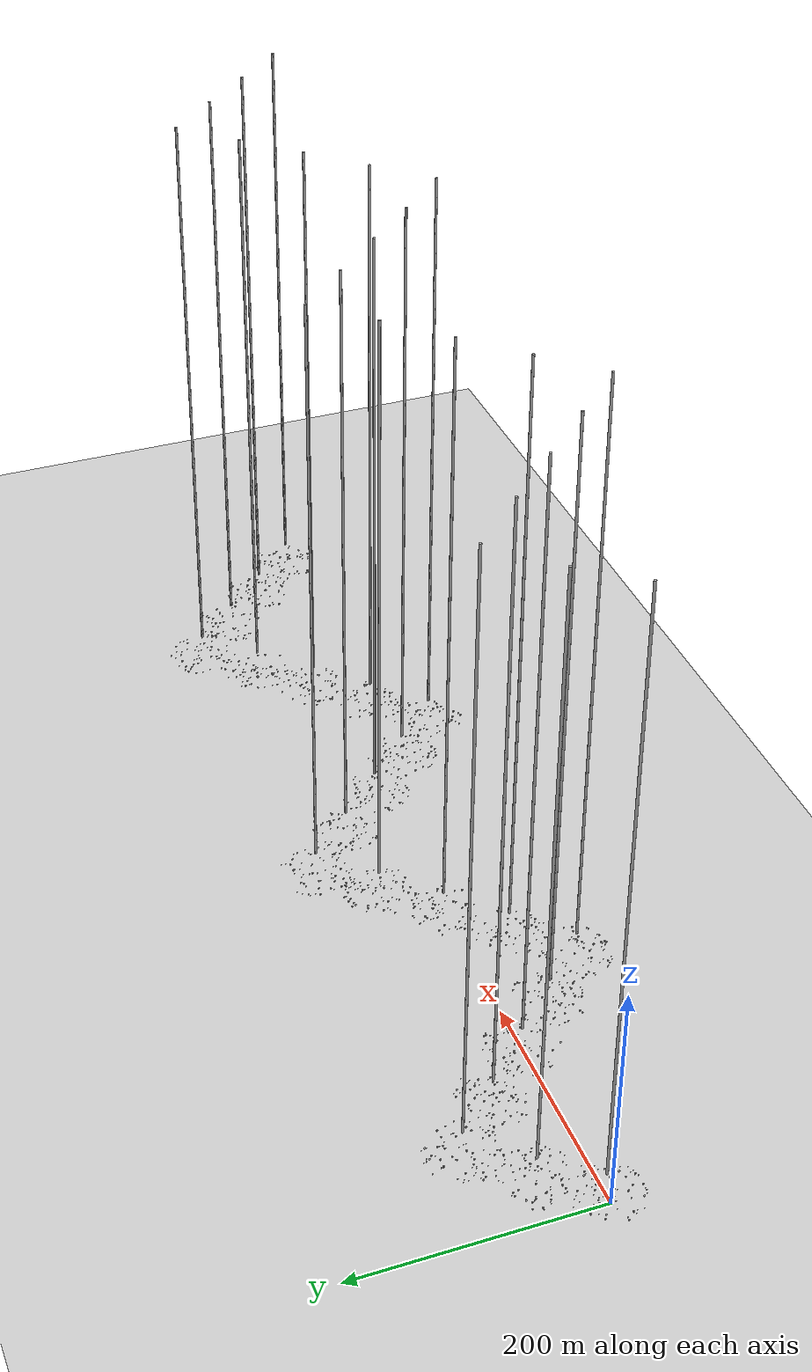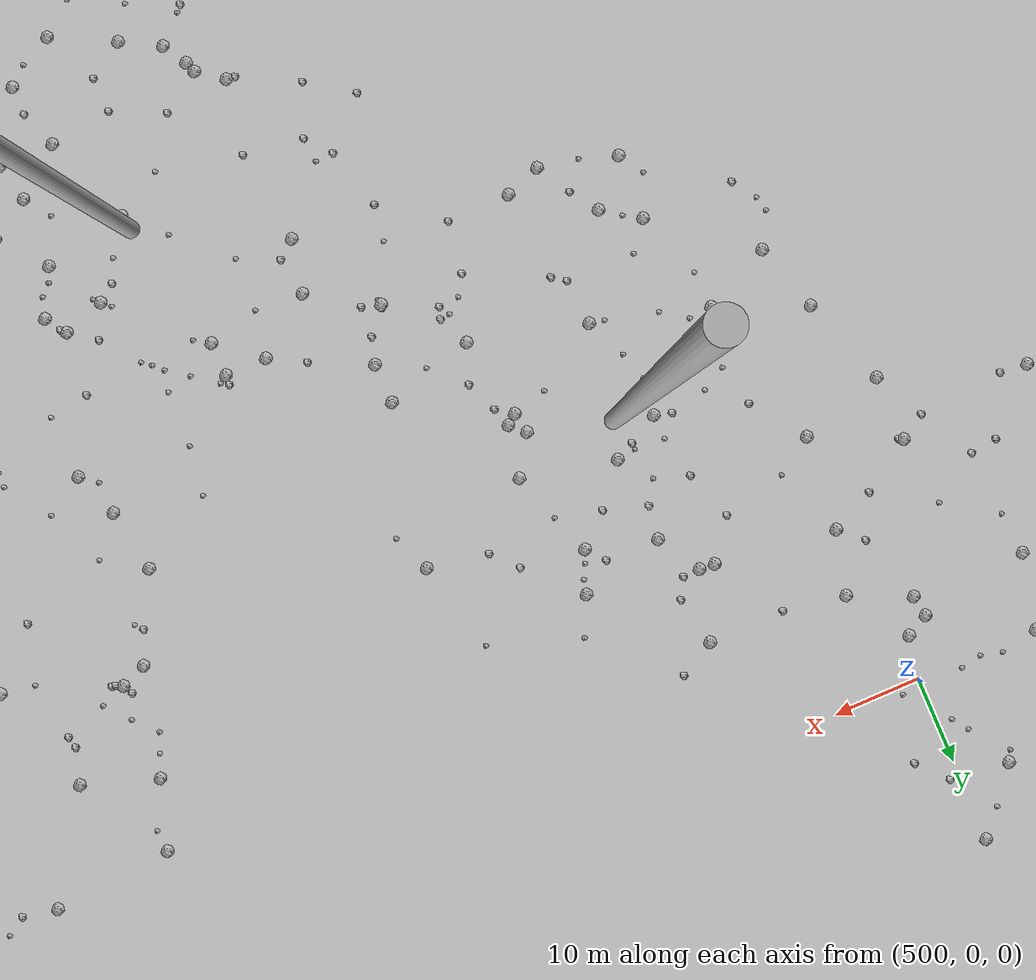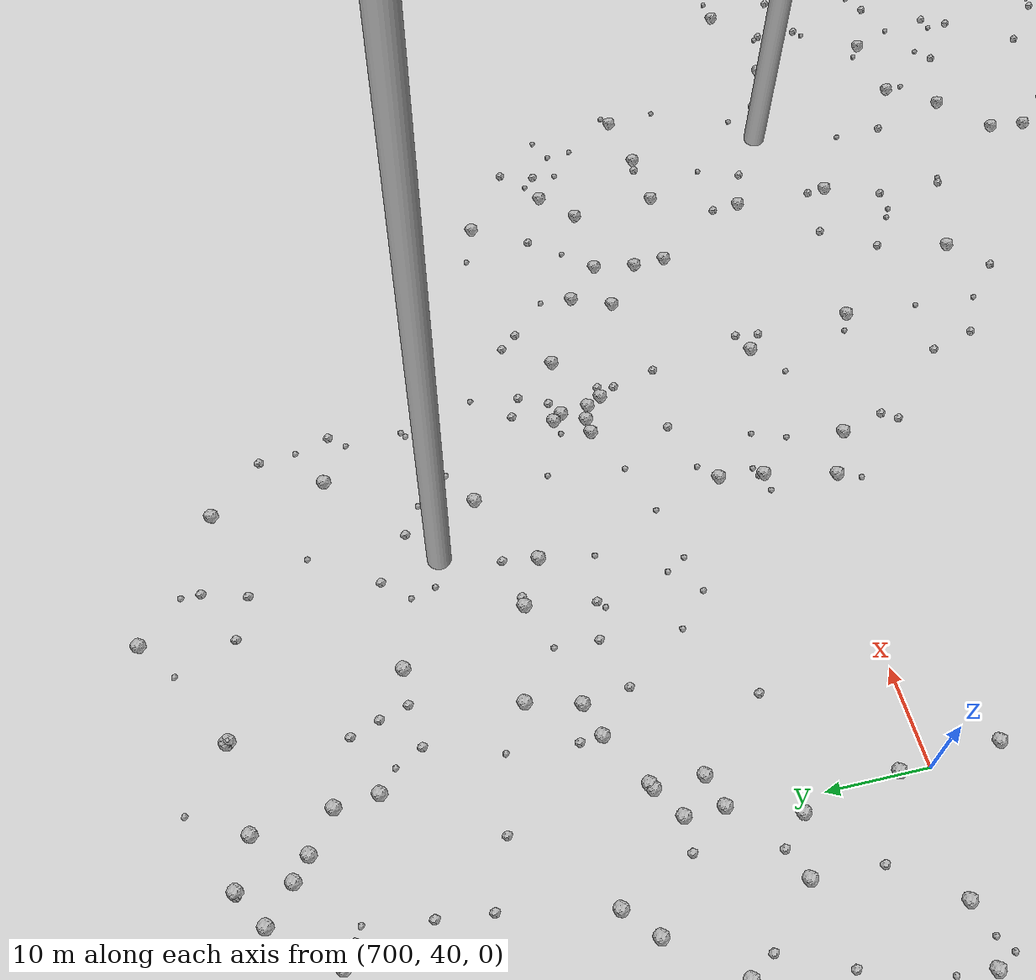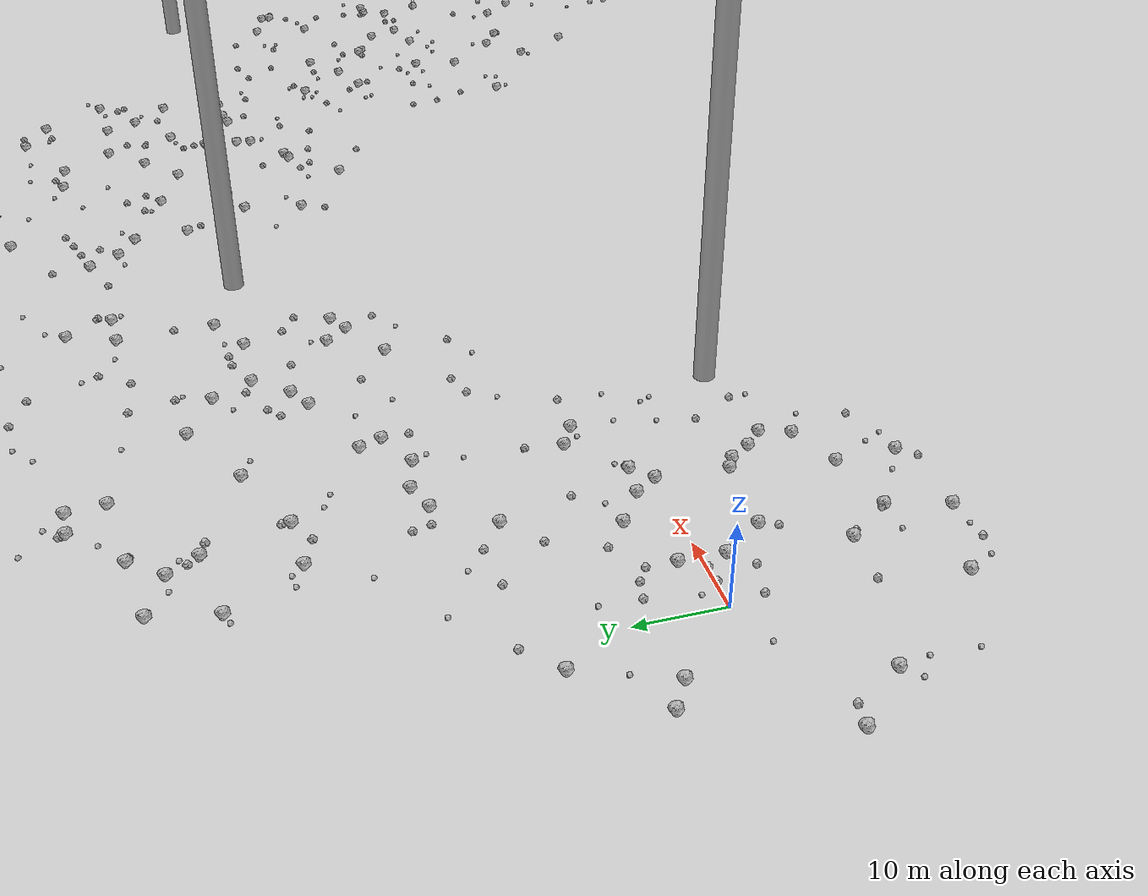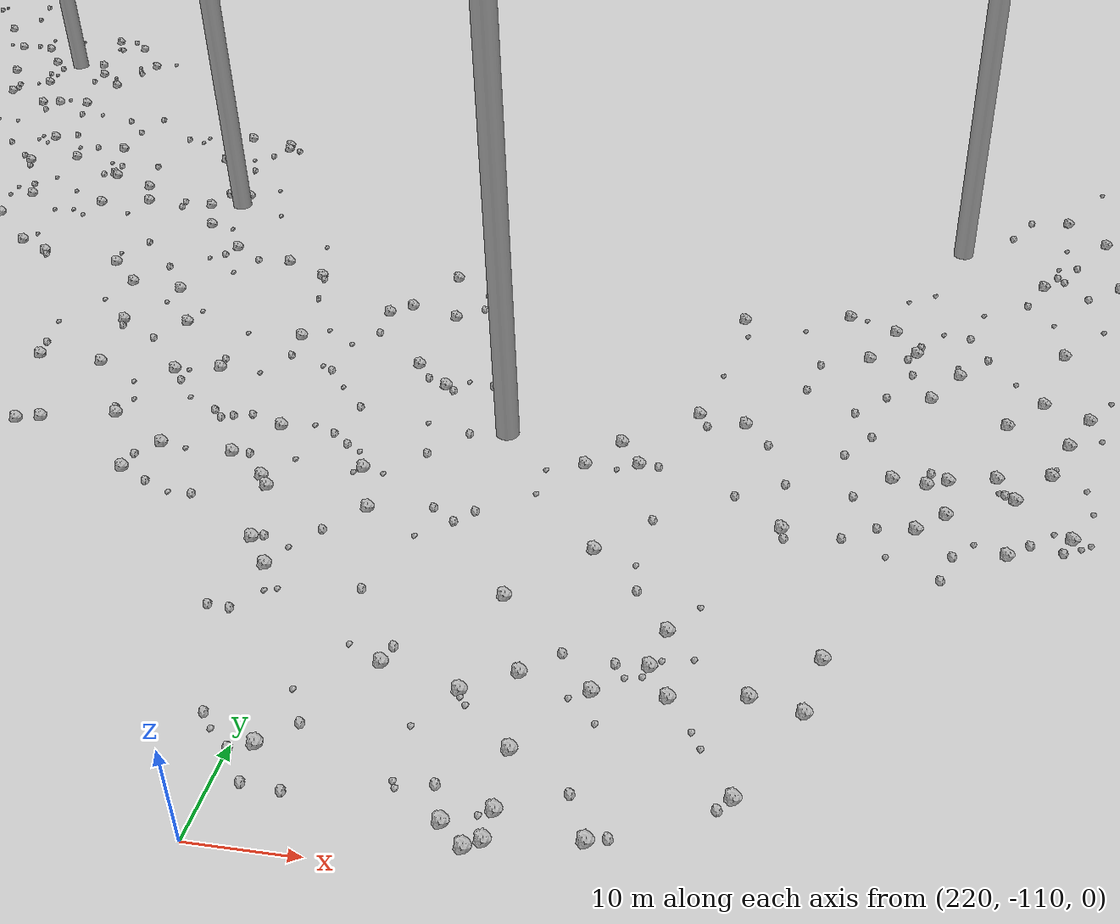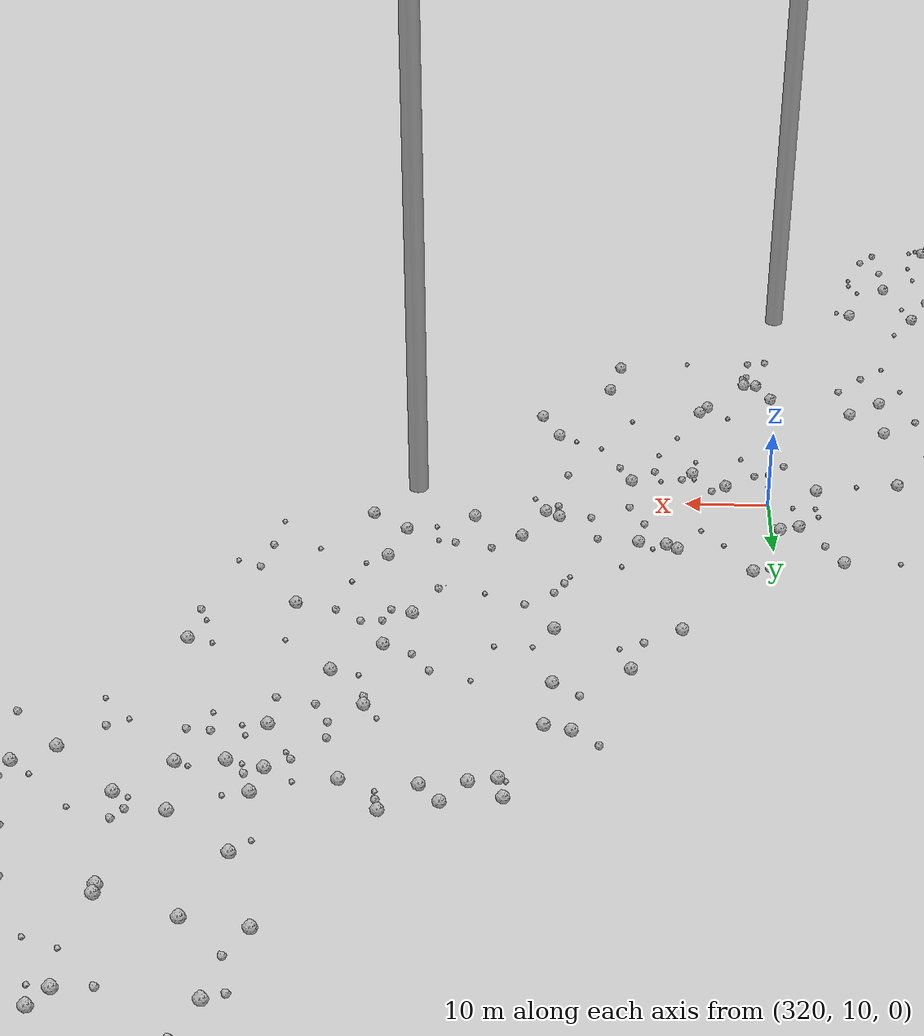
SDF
<sdf version="1.6">
 <world name="default">
  <include><uri>model://custom_ground</uri></include>
  <include><uri>model://sun</uri></include>
  <spherical_coordinates>
   <surface_model>EARTH_WGS84</surface_model>
   <latitude_deg>38.161479</latitude_deg>
   <longitude_deg>-122.454630</longitude_deg>
   <elevation>488.0</elevation>
   <heading_deg>90</heading_deg>
  </spherical_coordinates>
  <model name="rock1_0_0">
   <include><uri>model://rock1</uri><pose>6.1876728995866905 -15.851615394515106 0.5 0 0 0</pose></include>
  </model>
  <model name="rock1_0_1">
   <include><uri>model://rock1</uri><pose>19.352972901860625 2.721231807032723 0.5 0 0 0</pose></include>
  </model>
  <model name="rock1_0_2">
   <include><uri>model://rock1</uri><pose>21.21550641942369 0.021133102512848723 0.5 0 0 0</pose></include>
  </model>
  <model name="rock1_0_3">
   <include><uri>model://rock1</uri><pose>10.89624323835045 -7.450086403076913 0.5 0 0 0</pose></include>
  </model>
  <model name="rock1_0_4">
   <include><uri>model://rock1</uri><pose>26.103846802336967 -13.982679266174006 0.5 0 0 0</pose></include>
  </model>
  <model name="rock1_0_5">
   <include><uri>model://rock1</uri><pose>23.95046013513293 -11.839766026290302 0.5 0 0 0</pose></include>
  </model>
  <model name="rock1_0_6">
   <include><uri>model://rock1</uri><pose>7.407975786387858 -2.555391658508203 0.5 0 0 0</pose></include>
  </model>
  <model name="rock1_0_7">
   <include><uri>model://rock1</uri><pose>18.71334188046192 -27.05364649728247 0.5 0 0 0</pose></include>
  </model>
  <model name="rock1_0_8">
   <include><uri>model://rock1</uri><pose>-7.90248041755952 7.7034833154996605 0.5 0 0 0</pose></include>
  </model>
  <model name="rock1_0_9">
   <include><uri>model://rock1</uri><pose>-17.806441346461945 -5.223906912565184 0.5 0 0 0</pose></include>
  </model>
  <model name="rock1_0_10">
   <include><uri>model://rock1</uri><pose>-1.7556679184437627 -24.578710333432284 0.5 0 0 0</pose></include>
  </model>
  <model name="rock1_0_11">
   <include><uri>model://rock1</uri><pose>24.801766371958053 -17.442700135816334 0.5 0 0 0</pose></include>
  </model>
  <model name="rock1_0_12">
   <include><uri>model://rock1</uri><pose>18.53523371164585 -19.820987769851087 0.5 0 0 0</pose></include>
  </model>
  <model name="rock1_0_13">
   <include><uri>model://rock1</uri><pose>29.781865362698163 7.550453133508995 0.5 0 0 0</pose></include>
  </model>
  <model name="rock1_0_14">
   <include><uri>model://rock1</uri><pose>-11.242864960030186 9.802954299338701 0.5 0 0 0</pose></include>
  </model>
  <model name="rock1_0_15">
   <include><uri>model://rock1</uri><pose>22.257105909067022 -9.25009347521527 0.5 0 0 0</pose></include>
  </model>
  <model name="rock1_0_16">
   <include><uri>model://rock1</uri><pose>8.161688177759416 -28.144069004176878 0.5 0 0 0</pose></include>
  </model>
  <model name="rock1_0_17">
   <include><uri>model://rock1</uri><pose>20.62618718391918 -8.304375625665855 0.5 0 0 0</pose></include>
  </model>
  <model name="rock1_0_18">
   <include><uri>model://rock1</uri><pose>23.119881183518054 24.155103039176318 0.5 0 0 0</pose></include>
  </model>
  <model name="rock1_0_19">
   <include><uri>model://rock1</uri><pose>-3.8337683485451493 17.570967990411482 0.5 0 0 0</pose></include>
  </model>
  <model name="rock1_0_20">
   <include><uri>model://rock1</uri><pose>15.00098138588244 5.698939888929857 0.5 0 0 0</pose></include>
  </model>
  <model name="rock1_0_21">
   <include><uri>model://rock1</uri><pose>10.151045128919293 -21.275070539748825 0.5 0 0 0</pose></include>
  </model>
  <model name="rock1_0_22">
   <include><uri>model://rock1</uri><pose>23.62449907149127 2.146258695623878 0.5 0 0 0</pose></include>
  </model>
  <model name="rock1_0_23">
   <include><uri>model://rock1</uri><pose>-11.972162264924716 -11.386401269087084 0.5 0 0 0</pose></include>
  </model>
  <model name="rock1_0_24">
   <include><uri>model://rock1</uri><pose>18.53377094777742 17.846146451443076 0.5 0 0 0</pose></include>
  </model>
  <model name="rock1_0_25">
   <include><uri>model://rock1</uri><pose>32.88824853750095 5.867657308443327 0.5 0 0 0</pose></include>
  </model>
  <model name="rock1_0_26">
   <include><uri>model://rock1</uri><pose>7.548215836971494 2.587907687653292 0.5 0 0 0</pose></include>
  </model>
  <model name="rock2_0_0">
   <include><uri>model://rock2</uri><pose>24.124090310736072 2.3473752048601497 0.3 0 0 0</pose></include>
  </model>
  <model name="rock2_0_1">
   <include><uri>model://rock2</uri><pose>3.214024589187421 7.68717111389217 0.3 0 0 0</pose></include>
  </model>
  <model name="rock2_0_2">
   <include><uri>model://rock2</uri><pose>9.973573228168448 -9.388838023781926 0.3 0 0 0</pose></include>
  </model>
  <model name="rock2_0_3">
   <include><uri>model://rock2</uri><pose>19.58479661415501 26.665099791220747 0.3 0 0 0</pose></include>
  </model>
  <model name="rock2_0_4">
   <include><uri>model://rock2</uri><pose>20.642421038217833 9.498744936232875 0.3 0 0 0</pose></include>
  </model>
  <model name="rock2_0_5">
   <include><uri>model://rock2</uri><pose>-15.145908058610747 -5.744454701114286 0.3 0 0 0</pose></include>
  </model>
  <model name="rock2_0_6">
   <include><uri>model://rock2</uri><pose>6.9229297540389645 -16.551487409097525 0.3 0 0 0</pose></include>
  </model>
  <model name="rock2_0_7">
   <include><uri>model://rock2</uri><pose>-0.05401470661015395 20.953666673288453 0.3 0 0 0</pose></include>
  </model>
  <model name="rock2_0_8">
   <include><uri>model://rock2</uri><pose>33.39705520592093 -13.508044190066496 0.3 0 0 0</pose></include>
  </model>
  <model name="rock2_0_9">
   <include><uri>model://rock2</uri><pose>9.051946634351932 20.040937120101063 0.3 0 0 0</pose></include>
  </model>
  <model name="rock2_0_10">
   <include><uri>model://rock2</uri><pose>16.89041982703251 -28.88733372661306 0.3 0 0 0</pose></include>
  </model>
  <model name="rock2_0_11">
   <include><uri>model://rock2</uri><pose>5.686884451279376 7.139244055843186 0.3 0 0 0</pose></include>
  </model>
  <model name="rock2_0_12">
   <include><uri>model://rock2</uri><pose>5.8583560289077 -0.052055031787574535 0.3 0 0 0</pose></include>
  </model>
  <model name="rock2_0_13">
   <include><uri>model://rock2</uri><pose>30.347813787412747 11.850470314250813 0.3 0 0 0</pose></include>
  </model>
  <model name="rock2_0_14">
   <include><uri>model://rock2</uri><pose>4.926628572005338 -4.7842079438029295 0.3 0 0 0</pose></include>
  </model>
  <model name="rock2_0_15">
   <include><uri>model://rock2</uri><pose>38.56497525042574 5.623871621531094 0.3 0 0 0</pose></include>
  </model>
  <model name="rock2_0_16">
   <include><uri>model://rock2</uri><pose>14.187323770278027 14.325201457806784 0.3 0 0 0</pose></include>
  </model>
  <model name="rock2_0_17">
   <include><uri>model://rock2</uri><pose>0.720971604808831 -3.8297533839144577 0.3 0 0 0</pose></include>
  </model>
  <model name="rock2_0_18">
   <include><uri>model://rock2</uri><pose>2.496021060279727 -28.46013040758294 0.3 0 0 0</pose></include>
  </model>
  <model name="rock2_0_19">
   <include><uri>model://rock2</uri><pose>9.67980934367161 -20.859904127965763 0.3 0 0 0</pose></include>
  </model>
  <model name="rock2_0_20">
   <include><uri>model://rock2</uri><pose>14.711757272207784 20.46594056598974 0.3 0 0 0</pose></include>
  </model>
  <model name="rock2_0_21">
   <include><uri>model://rock2</uri><pose>30.37098494280341 -8.203032649926158 0.3 0 0 0</pose></include>
  </model>
  <model name="rock2_0_22">
   <include><uri>model://rock2</uri><pose>-0.4261029066426367 -15.214355970675186 0.3 0 0 0</pose></include>
  </model>
  <model name="rock2_0_23">
   <include><uri>model://rock2</uri><pose>7.532410709456464 5.900014929254013 0.3 0 0 0</pose></include>
  </model>
  <model name="rock2_0_24">
   <include><uri>model://rock2</uri><pose>3.594475797347229 -0.09250744986369241 0.3 0 0 0</pose></include>
  </model>
  <model name="rock2_0_25">
   <include><uri>model://rock2</uri><pose>11.495910379041181 8.455958982811651 0.3 0 0 0</pose></include>
  </model>
  <model name="rock2_0_26">
   <include><uri>model://rock2</uri><pose>26.49507695778484 -24.952664469483405 0.3 0 0 0</pose></include>
  </model>
  <model name="rock3_0_0">
   <include><uri>model://rock3</uri><pose>32.77422050448039 0.7218408615057577 0.2 0 0 0</pose></include>
  </model>
  <model name="rock3_0_1">
   <include><uri>model://rock3</uri><pose>38.388059305125196 0.32464450857484195 0.2 0 0 0</pose></include>
  </model>
  <model name="rock3_0_2">
   <include><uri>model://rock3</uri><pose>30.736816176867663 18.596759935087235 0.2 0 0 0</pose></include>
  </model>
  <model name="rock3_0_3">
   <include><uri>model://rock3</uri><pose>4.80289317804899 -28.35339389284672 0.2 0 0 0</pose></include>
  </model>
  <model name="rock3_0_4">
   <include><uri>model://rock3</uri><pose>36.223476003752765 -4.755857153081703 0.2 0 0 0</pose></include>
  </model>
  <model name="rock3_0_5">
   <include><uri>model://rock3</uri><pose>21.041897139921765 -24.728631411285985 0.2 0 0 0</pose></include>
  </model>
  <model name="rock3_0_6">
   <include><uri>model://rock3</uri><pose>-5.634833705464628 -1.9367701131880608 0.2 0 0 0</pose></include>
  </model>
  <model name="rock3_0_7">
   <include><uri>model://rock3</uri><pose>-0.21231206162326188 -27.84648028728881 0.2 0 0 0</pose></include>
  </model>
  <model name="rock3_0_8">
   <include><uri>model://rock3</uri><pose>3.542217599448744 12.068107280266503 0.2 0 0 0</pose></include>
  </model>
  <model name="rock3_0_9">
   <include><uri>model://rock3</uri><pose>30.9622476912189 5.5892473865181245 0.2 0 0 0</pose></include>
  </model>
  <model name="rock3_0_10">
   <include><uri>model://rock3</uri><pose>28.14723755509808 -19.593143849466998 0.2 0 0 0</pose></include>
  </model>
  <model name="rock3_0_11">
   <include><uri>model://rock3</uri><pose>18.5043034051763 6.406733700137778 0.2 0 0 0</pose></include>
  </model>
  <model name="rock3_0_12">
   <include><uri>model://rock3</uri><pose>2.2317910868076574 2.0253520725148633 0.2 0 0 0</pose></include>
  </model>
  <model name="rock3_0_13">
   <include><uri>model://rock3</uri><pose>12.058290939705131 22.702154297574232 0.2 0 0 0</pose></include>
  </model>
  <model name="rock3_0_14">
   <include><uri>model://rock3</uri><pose>6.072201707241263 26.11212355118377 0.2 0 0 0</pose></include>
  </model>
  <model name="rock3_0_15">
   <include><uri>model://rock3</uri><pose>-11.416811643577127 -14.879738917403085 0.2 0 0 0</pose></include>
  </model>
  <model name="rock3_0_16">
   <include><uri>model://rock3</uri><pose>35.6374575106767 -3.4907054669014848 0.2 0 0 0</pose></include>
  </model>
  <model name="rock3_0_17">
   <include><uri>model://rock3</uri><pose>33.57169613880328 -15.636435058973909 0.2 0 0 0</pose></include>
  </model>
  <model name="rock3_0_18">
   <include><uri>model://rock3</uri><pose>-11.756618812852675 -19.967993939653294 0.2 0 0 0</pose></include>
  </model>
  <model name="rock3_0_19">
   <include><uri>model://rock3</uri><pose>24.85816926974475 3.246610283365591 0.2 0 0 0</pose></include>
  </model>
  <model name="rock3_0_20">
   <include><uri>model://rock3</uri><pose>30.26239125655114 11.934335558893267 0.2 0 0 0</pose></include>
  </model>
  <model name="rock3_0_21">
   <include><uri>model://rock3</uri><pose>22.19568093423797 -26.974477093955908 0.2 0 0 0</pose></include>
  </model>
  <model name="rock3_0_22">
   <include><uri>model://rock3</uri><pose>15.451021472990377 -25.111080964025383 0.2 0 0 0</pose></include>
  </model>
  <model name="rock3_0_23">
   <include><uri>model://rock3</uri><pose>-5.990006386256187 12.20570527608659 0.2 0 0 0</pose></include>
  </model>
  <model name="rock3_0_24">
   <include><uri>model://rock3</uri><pose>31.461313957384 -3.9583077679799388 0.2 0 0 0</pose></include>
  </model>
  <model name="rock3_0_25">
   <include><uri>model://rock3</uri><pose>-13.770534083637182 -13.056573440641188 0.2 0 0 0</pose></include>
  </model>
  <model name="rock3_0_26">
   <include><uri>model://rock3</uri><pose>5.987582537508235 -21.31868505593469 0.2 0 0 0</pose></include>
  </model>
  <model name="rock1_1_0">
   <include><uri>model://rock1</uri><pose>50.05154898135596 43.73601467820312 0.5 0 0 0</pose></include>
  </model>
  <model name="rock1_1_1">
   <include><uri>model://rock1</uri><pose>34.01573796131281 42.26537963056451 0.5 0 0 0</pose></include>
  </model>
  <model name="rock1_1_2">
   <include><uri>model://rock1</uri><pose>64.33711435852453 27.75709009323275 0.5 0 0 0</pose></include>
  </model>
  <model name="rock1_1_3">
   <include><uri>model://rock1</uri><pose>61.201063174670665 38.842026065297745 0.5 0 0 0</pose></include>
  </model>
  <model name="rock1_1_4">
   <include><uri>model://rock1</uri><pose>35.639113287616404 29.212740742320484 0.5 0 0 0</pose></include>
  </model>
  <model name="rock1_1_5">
   <include><uri>model://rock1</uri><pose>48.904124879127416 34.87449455815139 0.5 0 0 0</pose></include>
  </model>
  <model name="rock1_1_6">
   <include><uri>model://rock1</uri><pose>61.51774737882007 26.283792278968235 0.5 0 0 0</pose></include>
  </model>
  <model name="rock1_1_7">
   <include><uri>model://rock1</uri><pose>32.69449554768537 60.48305681464478 0.5 0 0 0</pose></include>
  </model>
  <model name="rock1_1_8">
   <include><uri>model://rock1</uri><pose>54.939938789543874 22.618824715858366 0.5 0 0 0</pose></include>
  </model>
  <model name="rock1_1_9">
   <include><uri>model://rock1</uri><pose>26.87370604521642 25.383595786240427 0.5 0 0 0</pose></include>
  </model>
  <model name="rock1_1_10">
   <include><uri>model://rock1</uri><pose>52.56481032346932 38.96689269242904 0.5 0 0 0</pose></include>
  </model>
  <model name="rock1_1_11">
   <include><uri>model://rock1</uri><pose>66.5349404580743 53.73821899549548 0.5 0 0 0</pose></include>
  </model>
  <model name="rock1_1_12">
   <include><uri>model://rock1</uri><pose>24.57088040663745 38.26706311079216 0.5 0 0 0</pose></include>
  </model>
  <model name="rock1_1_13">
   <include><uri>model://rock1</uri><pose>59.10643046715172 29.037041875436206 0.5 0 0 0</pose></include>
  </model>
  <model name="rock1_1_14">
   <include><uri>model://rock1</uri><pose>33.12553040695611 56.16188914128964 0.5 0 0 0</pose></include>
  </model>
  <model name="rock1_1_15">
   <include><uri>model://rock1</uri><pose>45.82449053706738 33.2560407505373 0.5 0 0 0</pose></include>
  </model>
  <model name="rock1_1_16">
   <include><uri>model://rock1</uri><pose>22.962054270063057 54.79155702536342 0.5 0 0 0</pose></include>
  </model>
  <model name="rock1_1_17">
   <include><uri>model://rock1</uri><pose>12.54869628330354 46.38244774196971 0.5 0 0 0</pose></include>
  </model>
  <model name="rock1_1_18">
   <include><uri>model://rock1</uri><pose>29.205673426134027 60.40038246014384 0.5 0 0 0</pose></include>
  </model>
  <model name="rock1_1_19">
   <include><uri>model://rock1</uri><pose>36.73545405857128 26.57684274365777 0.5 0 0 0</pose></include>
  </model>
  <model name="rock1_1_20">
   <include><uri>model://rock1</uri><pose>21.899650282147032 47.71638770478223 0.5 0 0 0</pose></include>
  </model>
  <model name="rock1_1_21">
   <include><uri>model://rock1</uri><pose>14.204052643221312 53.534674453832004 0.5 0 0 0</pose></include>
  </model>
  <model name="rock1_1_22">
   <include><uri>model://rock1</uri><pose>19.800808959802698 51.17015385544539 0.5 0 0 0</pose></include>
  </model>
  <model name="rock1_1_23">
   <include><uri>model://rock1</uri><pose>66.8688123961407 41.873543086490756 0.5 0 0 0</pose></include>
  </model>
  <model name="rock1_1_24">
   <include><uri>model://rock1</uri><pose>17.586781890988554 37.98676876828584 0.5 0 0 0</pose></include>
  </model>
  <model name="rock1_1_25">
   <include><uri>model://rock1</uri><pose>43.625240301624295 47.17581161815198 0.5 0 0 0</pose></include>
  </model>
  <model name="rock1_1_26">
   <include><uri>model://rock1</uri><pose>31.533310184656365 24.204737499081546 0.5 0 0 0</pose></include>
  </model>
  <model name="rock2_1_0">
   <include><uri>model://rock2</uri><pose>56.73897596364485 40.751953171257966 0.3 0 0 0</pose></include>
  </model>
  <model name="rock2_1_1">
   <include><uri>model://rock2</uri><pose>20.13005008785386 24.57490511922754 0.3 0 0 0</pose></include>
  </model>
  <model name="rock2_1_2">
   <include><uri>model://rock2</uri><pose>49.304521540691184 26.517520477233152 0.3 0 0 0</pose></include>
  </model>
  <model name="rock2_1_3">
   <include><uri>model://rock2</uri><pose>58.81650972918329 40.888239790505 0.3 0 0 0</pose></include>
  </model>
  <model name="rock2_1_4">
   <include><uri>model://rock2</uri><pose>28.828723311732933 61.07534330982341 0.3 0 0 0</pose></include>
  </model>
  <model name="rock2_1_5">
   <include><uri>model://rock2</uri><pose>49.892618113177065 53.21162688348031 0.3 0 0 0</pose></include>
  </model>
  <model name="rock2_1_6">
   <include><uri>model://rock2</uri><pose>63.66060024056209 22.557993805207797 0.3 0 0 0</pose></include>
  </model>
  <model name="rock2_1_7">
   <include><uri>model://rock2</uri><pose>24.551011080021375 39.244349212922856 0.3 0 0 0</pose></include>
  </model>
  <model name="rock2_1_8">
   <include><uri>model://rock2</uri><pose>58.76955436778288 56.15291669460807 0.3 0 0 0</pose></include>
  </model>
  <model name="rock2_1_9">
   <include><uri>model://rock2</uri><pose>50.9916820268665 47.86097361343539 0.3 0 0 0</pose></include>
  </model>
  <model name="rock2_1_10">
   <include><uri>model://rock2</uri><pose>50.82386646192094 66.13555733279108 0.3 0 0 0</pose></include>
  </model>
  <model name="rock2_1_11">
   <include><uri>model://rock2</uri><pose>56.119998414207934 52.53226105100372 0.3 0 0 0</pose></include>
  </model>
  <model name="rock2_1_12">
   <include><uri>model://rock2</uri><pose>45.96584361708018 37.89868290425043 0.3 0 0 0</pose></include>
  </model>
  <model name="rock2_1_13">
   <include><uri>model://rock2</uri><pose>23.48510259200921 54.48407568521746 0.3 0 0 0</pose></include>
  </model>
  <model name="rock2_1_14">
   <include><uri>model://rock2</uri><pose>20.789829110832848 48.97381303260663 0.3 0 0 0</pose></include>
  </model>
  <model name="rock2_1_15">
   <include><uri>model://rock2</uri><pose>55.29487761112709 14.765249769179121 0.3 0 0 0</pose></include>
  </model>
  <model name="rock2_1_16">
   <include><uri>model://rock2</uri><pose>21.243961547458703 36.57185326201076 0.3 0 0 0</pose></include>
  </model>
  <model name="rock2_1_17">
   <include><uri>model://rock2</uri><pose>36.739393653863864 23.440474067225182 0.3 0 0 0</pose></include>
  </model>
  <model name="rock2_1_18">
   <include><uri>model://rock2</uri><pose>43.12595272526565 15.281270136351019 0.3 0 0 0</pose></include>
  </model>
  <model name="rock2_1_19">
   <include><uri>model://rock2</uri><pose>46.44903221184143 16.341604938441655 0.3 0 0 0</pose></include>
  </model>
  <model name="rock2_1_20">
   <include><uri>model://rock2</uri><pose>63.02142539801481 33.949822946025634 0.3 0 0 0</pose></include>
  </model>
  <model name="rock2_1_21">
   <include><uri>model://rock2</uri><pose>44.34794525044143 36.61142001697894 0.3 0 0 0</pose></include>
  </model>
  <model name="rock2_1_22">
   <include><uri>model://rock2</uri><pose>54.82856037133404 33.978827695796944 0.3 0 0 0</pose></include>
  </model>
  <model name="rock2_1_23">
   <include><uri>model://rock2</uri><pose>67.01770659341919 46.77381587693766 0.3 0 0 0</pose></include>
  </model>
  <model name="rock2_1_24">
   <include><uri>model://rock2</uri><pose>23.767874678337176 47.01586946997983 0.3 0 0 0</pose></include>
  </model>
  <model name="rock2_1_25">
   <include><uri>model://rock2</uri><pose>65.96633758585358 32.08899098998607 0.3 0 0 0</pose></include>
  </model>
  <model name="rock2_1_26">
   <include><uri>model://rock2</uri><pose>50.30266904495838 39.84022896606409 0.3 0 0 0</pose></include>
  </model>
  <model name="rock3_1_0">
   <include><uri>model://rock3</uri><pose>47.27903132190338 41.62229863823741 0.2 0 0 0</pose></include>
  </model>
  <model name="rock3_1_1">
   <include><uri>model://rock3</uri><pose>42.07966295373035 28.45576097644032 0.2 0 0 0</pose></include>
  </model>
  <model name="rock3_1_2">
   <include><uri>model://rock3</uri><pose>17.256269840342092 51.00457833498972 0.2 0 0 0</pose></include>
  </model>
  <model name="rock3_1_3">
   <include><uri>model://rock3</uri><pose>60.41655148528453 20.149218909320073 0.2 0 0 0</pose></include>
  </model>
  <model name="rock3_1_4">
   <include><uri>model://rock3</uri><pose>32.4489298641993 22.38882970691995 0.2 0 0 0</pose></include>
  </model>
  <model name="rock3_1_5">
   <include><uri>model://rock3</uri><pose>51.62386608729979 46.944242151349755 0.2 0 0 0</pose></include>
  </model>
  <model name="rock3_1_6">
   <include><uri>model://rock3</uri><pose>45.97186847584428 65.70945118034922 0.2 0 0 0</pose></include>
  </model>
  <model name="rock3_1_7">
   <include><uri>model://rock3</uri><pose>26.77019275389511 64.93898226848003 0.2 0 0 0</pose></include>
  </model>
  <model name="rock3_1_8">
   <include><uri>model://rock3</uri><pose>30.477485299269425 62.60590399133973 0.2 0 0 0</pose></include>
  </model>
  <model name="rock3_1_9">
   <include><uri>model://rock3</uri><pose>51.56708694041109 12.507833045540487 0.2 0 0 0</pose></include>
  </model>
  <model name="rock3_1_10">
   <include><uri>model://rock3</uri><pose>13.677420254321857 31.70364852894071 0.2 0 0 0</pose></include>
  </model>
  <model name="rock3_1_11">
   <include><uri>model://rock3</uri><pose>16.215763101651675 39.31387282180388 0.2 0 0 0</pose></include>
  </model>
  <model name="rock3_1_12">
   <include><uri>model://rock3</uri><pose>62.052827304280804 41.0567679261146 0.2 0 0 0</pose></include>
  </model>
  <model name="rock3_1_13">
   <include><uri>model://rock3</uri><pose>41.29592191929265 12.068064099179969 0.2 0 0 0</pose></include>
  </model>
  <model name="rock3_1_14">
   <include><uri>model://rock3</uri><pose>62.31322038863335 54.08781186151923 0.2 0 0 0</pose></include>
  </model>
  <model name="rock3_1_15">
   <include><uri>model://rock3</uri><pose>28.207231287944317 33.612936693687466 0.2 0 0 0</pose></include>
  </model>
  <model name="rock3_1_16">
   <include><uri>model://rock3</uri><pose>26.410625117418295 57.29140804631652 0.2 0 0 0</pose></include>
  </model>
  <model name="rock3_1_17">
   <include><uri>model://rock3</uri><pose>44.16164802082989 23.782665331586106 0.2 0 0 0</pose></include>
  </model>
  <model name="rock3_1_18">
   <include><uri>model://rock3</uri><pose>58.049139965347756 58.05398385179337 0.2 0 0 0</pose></include>
  </model>
  <model name="rock3_1_19">
   <include><uri>model://rock3</uri><pose>59.552264002635965 30.84261555527195 0.2 0 0 0</pose></include>
  </model>
  <model name="rock3_1_20">
   <include><uri>model://rock3</uri><pose>36.672190317743386 40.9561680447419 0.2 0 0 0</pose></include>
  </model>
  <model name="rock3_1_21">
   <include><uri>model://rock3</uri><pose>42.81867311721897 54.24907705270505 0.2 0 0 0</pose></include>
  </model>
  <model name="rock3_1_22">
   <include><uri>model://rock3</uri><pose>21.73096931811481 49.678505429829535 0.2 0 0 0</pose></include>
  </model>
  <model name="rock3_1_23">
   <include><uri>model://rock3</uri><pose>14.521376925817453 39.163487460119484 0.2 0 0 0</pose></include>
  </model>
  <model name="rock3_1_24">
   <include><uri>model://rock3</uri><pose>43.344834478501376 63.57406230831759 0.2 0 0 0</pose></include>
  </model>
  <model name="rock3_1_25">
   <include><uri>model://rock3</uri><pose>11.14177319037969 45.80553499662573 0.2 0 0 0</pose></include>
  </model>
  <model name="rock3_1_26">
   <include><uri>model://rock3</uri><pose>26.212546642328835 34.56707572688558 0.2 0 0 0</pose></include>
  </model>
  <model name="rock1_2_0">
   <include><uri>model://rock1</uri><pose>52.14535964139681 73.21565324862675 0.5 0 0 0</pose></include>
  </model>
  <model name="rock1_2_1">
   <include><uri>model://rock1</uri><pose>56.99686000507103 73.24334545615663 0.5 0 0 0</pose></include>
  </model>
  <model name="rock1_2_2">
   <include><uri>model://rock1</uri><pose>79.35812348827467 76.77659243596929 0.5 0 0 0</pose></include>
  </model>
  <model name="rock1_2_3">
   <include><uri>model://rock1</uri><pose>83.65328276236603 102.10798252299006 0.5 0 0 0</pose></include>
  </model>
  <model name="rock1_2_4">
   <include><uri>model://rock1</uri><pose>89.35734812638955 90.8706546398075 0.5 0 0 0</pose></include>
  </model>
  <model name="rock1_2_5">
   <include><uri>model://rock1</uri><pose>87.11943220378298 56.24085524375643 0.5 0 0 0</pose></include>
  </model>
  <model name="rock1_2_6">
   <include><uri>model://rock1</uri><pose>89.58451347831434 52.41800955374709 0.5 0 0 0</pose></include>
  </model>
  <model name="rock1_2_7">
   <include><uri>model://rock1</uri><pose>60.19357144482233 85.07275109529792 0.5 0 0 0</pose></include>
  </model>
  <model name="rock1_2_8">
   <include><uri>model://rock1</uri><pose>91.97992620818604 104.16285477312816 0.5 0 0 0</pose></include>
  </model>
  <model name="rock1_2_9">
   <include><uri>model://rock1</uri><pose>89.76114605100204 95.0922499854282 0.5 0 0 0</pose></include>
  </model>
  <model name="rock1_2_10">
   <include><uri>model://rock1</uri><pose>50.322073644030766 75.87087170882269 0.5 0 0 0</pose></include>
  </model>
  <model name="rock1_2_11">
   <include><uri>model://rock1</uri><pose>78.19858917575053 97.38368000490914 0.5 0 0 0</pose></include>
  </model>
  <model name="rock1_2_12">
   <include><uri>model://rock1</uri><pose>73.85928776584402 86.23091562631319 0.5 0 0 0</pose></include>
  </model>
  <model name="rock1_2_13">
   <include><uri>model://rock1</uri><pose>100.24458454235938 68.72588232833594 0.5 0 0 0</pose></include>
  </model>
  <model name="rock1_2_14">
   <include><uri>model://rock1</uri><pose>71.35237234730256 97.64070263009114 0.5 0 0 0</pose></include>
  </model>
  <model name="rock1_2_15">
   <include><uri>model://rock1</uri><pose>94.7857050321424 78.86422790570847 0.5 0 0 0</pose></include>
  </model>
  <model name="rock1_2_16">
   <include><uri>model://rock1</uri><pose>69.07054146008743 59.65812181585479 0.5 0 0 0</pose></include>
  </model>
  <model name="rock1_2_17">
   <include><uri>model://rock1</uri><pose>66.07575447020457 76.67412985032023 0.5 0 0 0</pose></include>
  </model>
  <model name="rock1_2_18">
   <include><uri>model://rock1</uri><pose>97.62508051367143 88.9710077147392 0.5 0 0 0</pose></include>
  </model>
  <model name="rock1_2_19">
   <include><uri>model://rock1</uri><pose>96.11081374344674 66.4224108808683 0.5 0 0 0</pose></include>
  </model>
  <model name="rock1_2_20">
   <include><uri>model://rock1</uri><pose>86.66297812310091 90.50385053902646 0.5 0 0 0</pose></include>
  </model>
  <model name="rock1_2_21">
   <include><uri>model://rock1</uri><pose>81.34245508620381 104.50866759857533 0.5 0 0 0</pose></include>
  </model>
  <model name="rock1_2_22">
   <include><uri>model://rock1</uri><pose>75.96151971812398 73.60968967620323 0.5 0 0 0</pose></include>
  </model>
  <model name="rock1_2_23">
   <include><uri>model://rock1</uri><pose>104.38142105821585 89.64075883331842 0.5 0 0 0</pose></include>
  </model>
  <model name="rock1_2_24">
   <include><uri>model://rock1</uri><pose>106.54038757066076 68.61705153982854 0.5 0 0 0</pose></include>
  </model>
  <model name="rock1_2_25">
   <include><uri>model://rock1</uri><pose>71.74415751556015 54.08891281430557 0.5 0 0 0</pose></include>
  </model>
  <model name="rock1_2_26">
   <include><uri>model://rock1</uri><pose>69.98632038905532 74.46478442494995 0.5 0 0 0</pose></include>
  </model>
  <model name="rock2_2_0">
   <include><uri>model://rock2</uri><pose>108.71384880688163 74.90967315298349 0.3 0 0 0</pose></include>
  </model>
  <model name="rock2_2_1">
   <include><uri>model://rock2</uri><pose>72.57428278583771 55.861630973301686 0.3 0 0 0</pose></include>
  </model>
  <model name="rock2_2_2">
   <include><uri>model://rock2</uri><pose>79.89867332460702 107.42891867483428 0.3 0 0 0</pose></include>
  </model>
  <model name="rock2_2_3">
   <include><uri>model://rock2</uri><pose>106.53648770522051 82.38033043237044 0.3 0 0 0</pose></include>
  </model>
  <model name="rock2_2_4">
   <include><uri>model://rock2</uri><pose>85.87904048344265 74.67176443911198 0.3 0 0 0</pose></include>
  </model>
  <model name="rock2_2_5">
   <include><uri>model://rock2</uri><pose>63.53133285278621 78.67835772632253 0.3 0 0 0</pose></include>
  </model>
  <model name="rock2_2_6">
   <include><uri>model://rock2</uri><pose>56.38297664410035 80.45313238702298 0.3 0 0 0</pose></include>
  </model>
  <model name="rock2_2_7">
   <include><uri>model://rock2</uri><pose>55.622906617360194 64.24426562698356 0.3 0 0 0</pose></include>
  </model>
  <model name="rock2_2_8">
   <include><uri>model://rock2</uri><pose>67.69197402458741 107.2920278056892 0.3 0 0 0</pose></include>
  </model>
  <model name="rock2_2_9">
   <include><uri>model://rock2</uri><pose>86.51330996910971 61.09002654448622 0.3 0 0 0</pose></include>
  </model>
  <model name="rock2_2_10">
   <include><uri>model://rock2</uri><pose>72.72861643283906 55.70490170089504 0.3 0 0 0</pose></include>
  </model>
  <model name="rock2_2_11">
   <include><uri>model://rock2</uri><pose>90.90094339475404 57.24190603901583 0.3 0 0 0</pose></include>
  </model>
  <model name="rock2_2_12">
   <include><uri>model://rock2</uri><pose>64.95298353835437 70.39141949825381 0.3 0 0 0</pose></include>
  </model>
  <model name="rock2_2_13">
   <include><uri>model://rock2</uri><pose>81.97974489978286 106.38501338367746 0.3 0 0 0</pose></include>
  </model>
  <model name="rock2_2_14">
   <include><uri>model://rock2</uri><pose>70.7244844403354 99.17638297813903 0.3 0 0 0</pose></include>
  </model>
  <model name="rock2_2_15">
   <include><uri>model://rock2</uri><pose>52.58247359967183 76.71228402719797 0.3 0 0 0</pose></include>
  </model>
  <model name="rock2_2_16">
   <include><uri>model://rock2</uri><pose>57.392826491862124 92.32810202993991 0.3 0 0 0</pose></include>
  </model>
  <model name="rock2_2_17">
   <include><uri>model://rock2</uri><pose>96.8296860941084 59.20480684794495 0.3 0 0 0</pose></include>
  </model>
  <model name="rock2_2_18">
   <include><uri>model://rock2</uri><pose>84.45384681510659 80.34989747537226 0.3 0 0 0</pose></include>
  </model>
  <model name="rock2_2_19">
   <include><uri>model://rock2</uri><pose>90.46969816776078 107.15987851309524 0.3 0 0 0</pose></include>
  </model>
  <model name="rock2_2_20">
   <include><uri>model://rock2</uri><pose>93.86707568293187 58.16740127774341 0.3 0 0 0</pose></include>
  </model>
  <model name="rock2_2_21">
   <include><uri>model://rock2</uri><pose>91.47013698400175 102.64543393045116 0.3 0 0 0</pose></include>
  </model>
  <model name="rock2_2_22">
   <include><uri>model://rock2</uri><pose>77.384970547137 88.36595283065174 0.3 0 0 0</pose></include>
  </model>
  <model name="rock2_2_23">
   <include><uri>model://rock2</uri><pose>81.11075483132622 54.12824420926319 0.3 0 0 0</pose></include>
  </model>
  <model name="rock2_2_24">
   <include><uri>model://rock2</uri><pose>78.50971249237189 88.49805776114464 0.3 0 0 0</pose></include>
  </model>
  <model name="rock2_2_25">
   <include><uri>model://rock2</uri><pose>97.85541768792247 79.68043172921018 0.3 0 0 0</pose></include>
  </model>
  <model name="rock2_2_26">
   <include><uri>model://rock2</uri><pose>91.84776974004535 54.77537714982124 0.3 0 0 0</pose></include>
  </model>
  <model name="rock3_2_0">
   <include><uri>model://rock3</uri><pose>63.12520357346385 75.76784641118945 0.2 0 0 0</pose></include>
  </model>
  <model name="rock3_2_1">
   <include><uri>model://rock3</uri><pose>64.24361008473424 67.1975393265169 0.2 0 0 0</pose></include>
  </model>
  <model name="rock3_2_2">
   <include><uri>model://rock3</uri><pose>62.10058627100059 76.05267819791872 0.2 0 0 0</pose></include>
  </model>
  <model name="rock3_2_3">
   <include><uri>model://rock3</uri><pose>61.44377601342093 80.63809587009642 0.2 0 0 0</pose></include>
  </model>
  <model name="rock3_2_4">
   <include><uri>model://rock3</uri><pose>69.56649680300728 80.04634114401676 0.2 0 0 0</pose></include>
  </model>
  <model name="rock3_2_5">
   <include><uri>model://rock3</uri><pose>86.66692428190856 51.71135652624463 0.2 0 0 0</pose></include>
  </model>
  <model name="rock3_2_6">
   <include><uri>model://rock3</uri><pose>92.84099392396894 88.54655635351483 0.2 0 0 0</pose></include>
  </model>
  <model name="rock3_2_7">
   <include><uri>model://rock3</uri><pose>81.83735701041644 88.53998598317065 0.2 0 0 0</pose></include>
  </model>
  <model name="rock3_2_8">
   <include><uri>model://rock3</uri><pose>58.42344010140502 78.4116246035884 0.2 0 0 0</pose></include>
  </model>
  <model name="rock3_2_9">
   <include><uri>model://rock3</uri><pose>61.24863652873161 67.77683590413623 0.2 0 0 0</pose></include>
  </model>
  <model name="rock3_2_10">
   <include><uri>model://rock3</uri><pose>82.70838343921415 99.38723330334433 0.2 0 0 0</pose></include>
  </model>
  <model name="rock3_2_11">
   <include><uri>model://rock3</uri><pose>79.22913972467155 109.32975806118165 0.2 0 0 0</pose></include>
  </model>
  <model name="rock3_2_12">
   <include><uri>model://rock3</uri><pose>75.95695257098623 64.76730722155216 0.2 0 0 0</pose></include>
  </model>
  <model name="rock3_2_13">
   <include><uri>model://rock3</uri><pose>55.300784321957074 87.95899550878143 0.2 0 0 0</pose></include>
  </model>
  <model name="rock3_2_14">
   <include><uri>model://rock3</uri><pose>53.28229382487159 89.95007390292812 0.2 0 0 0</pose></include>
  </model>
  <model name="rock3_2_15">
   <include><uri>model://rock3</uri><pose>70.7198327559184 62.12203066572718 0.2 0 0 0</pose></include>
  </model>
  <model name="rock3_2_16">
   <include><uri>model://rock3</uri><pose>72.72956568331651 90.1612798387959 0.2 0 0 0</pose></include>
  </model>
  <model name="rock3_2_17">
   <include><uri>model://rock3</uri><pose>53.79927795524625 90.28930402859905 0.2 0 0 0</pose></include>
  </model>
  <model name="rock3_2_18">
   <include><uri>model://rock3</uri><pose>103.04029782656278 89.7676384098725 0.2 0 0 0</pose></include>
  </model>
  <model name="rock3_2_19">
   <include><uri>model://rock3</uri><pose>102.50815183947977 90.01529487105554 0.2 0 0 0</pose></include>
  </model>
  <model name="rock3_2_20">
   <include><uri>model://rock3</uri><pose>73.12129807060417 75.66963715802981 0.2 0 0 0</pose></include>
  </model>
  <model name="rock3_2_21">
   <include><uri>model://rock3</uri><pose>85.46215143930783 76.6446742619745 0.2 0 0 0</pose></include>
  </model>
  <model name="rock3_2_22">
   <include><uri>model://rock3</uri><pose>97.98588940426157 81.16503068200248 0.2 0 0 0</pose></include>
  </model>
  <model name="rock3_2_23">
   <include><uri>model://rock3</uri><pose>74.9628604880994 87.0948046586804 0.2 0 0 0</pose></include>
  </model>
  <model name="rock3_2_24">
   <include><uri>model://rock3</uri><pose>72.69990978332163 52.86698101061486 0.2 0 0 0</pose></include>
  </model>
  <model name="rock3_2_25">
   <include><uri>model://rock3</uri><pose>53.074592775838745 85.86670892286642 0.2 0 0 0</pose></include>
  </model>
  <model name="rock3_2_26">
   <include><uri>model://rock3</uri><pose>89.62252272205603 93.18922735085104 0.2 0 0 0</pose></include>
  </model>
  <model name="rock1_3_0">
   <include><uri>model://rock1</uri><pose>135.53183198128426 47.715630168251536 0.5 0 0 0</pose></include>
  </model>
  <model name="rock1_3_1">
   <include><uri>model://rock1</uri><pose>136.7572497014689 61.470893333436415 0.5 0 0 0</pose></include>
  </model>
  <model name="rock1_3_2">
   <include><uri>model://rock1</uri><pose>94.1437518835107 42.85554325503732 0.5 0 0 0</pose></include>
  </model>
  <model name="rock1_3_3">
   <include><uri>model://rock1</uri><pose>119.36262558221081 58.93480425067057 0.5 0 0 0</pose></include>
  </model>
  <model name="rock1_3_4">
   <include><uri>model://rock1</uri><pose>119.03217794453484 47.20123642181592 0.5 0 0 0</pose></include>
  </model>
  <model name="rock1_3_5">
   <include><uri>model://rock1</uri><pose>123.57840146782976 37.72951651360489 0.5 0 0 0</pose></include>
  </model>
  <model name="rock1_3_6">
   <include><uri>model://rock1</uri><pose>116.7075313987002 26.3503070184259 0.5 0 0 0</pose></include>
  </model>
  <model name="rock1_3_7">
   <include><uri>model://rock1</uri><pose>104.72185516133038 45.72981161779176 0.5 0 0 0</pose></include>
  </model>
  <model name="rock1_3_8">
   <include><uri>model://rock1</uri><pose>113.33719006211567 42.63631256331285 0.5 0 0 0</pose></include>
  </model>
  <model name="rock1_3_9">
   <include><uri>model://rock1</uri><pose>99.27259321005637 34.36761960207407 0.5 0 0 0</pose></include>
  </model>
  <model name="rock1_3_10">
   <include><uri>model://rock1</uri><pose>130.5289636171229 64.56602520923974 0.5 0 0 0</pose></include>
  </model>
  <model name="rock1_3_11">
   <include><uri>model://rock1</uri><pose>123.13220411152147 32.85014930126052 0.5 0 0 0</pose></include>
  </model>
  <model name="rock1_3_12">
   <include><uri>model://rock1</uri><pose>124.18996193071858 52.27358801943999 0.5 0 0 0</pose></include>
  </model>
  <model name="rock1_3_13">
   <include><uri>model://rock1</uri><pose>133.2584648590475 52.07857292300638 0.5 0 0 0</pose></include>
  </model>
  <model name="rock1_3_14">
   <include><uri>model://rock1</uri><pose>143.032680624132 52.97919198943364 0.5 0 0 0</pose></include>
  </model>
  <model name="rock1_3_15">
   <include><uri>model://rock1</uri><pose>108.02736448503033 19.179906544666803 0.5 0 0 0</pose></include>
  </model>
  <model name="rock1_3_16">
   <include><uri>model://rock1</uri><pose>93.4812477247272 50.02547492004207 0.5 0 0 0</pose></include>
  </model>
  <model name="rock1_3_17">
   <include><uri>model://rock1</uri><pose>127.803863778678 42.66071698328675 0.5 0 0 0</pose></include>
  </model>
  <model name="rock1_3_18">
   <include><uri>model://rock1</uri><pose>134.39628907582858 33.900427479260884 0.5 0 0 0</pose></include>
  </model>
  <model name="rock1_3_19">
   <include><uri>model://rock1</uri><pose>119.47810553533286 37.1789141356856 0.5 0 0 0</pose></include>
  </model>
  <model name="rock1_3_20">
   <include><uri>model://rock1</uri><pose>122.70638724094772 30.780956649041794 0.5 0 0 0</pose></include>
  </model>
  <model name="rock1_3_21">
   <include><uri>model://rock1</uri><pose>131.5263986525836 33.36281437481094 0.5 0 0 0</pose></include>
  </model>
  <model name="rock1_3_22">
   <include><uri>model://rock1</uri><pose>97.60469153818231 26.437243295149237 0.5 0 0 0</pose></include>
  </model>
  <model name="rock1_3_23">
   <include><uri>model://rock1</uri><pose>114.97183240095069 25.880159919005372 0.5 0 0 0</pose></include>
  </model>
  <model name="rock1_3_24">
   <include><uri>model://rock1</uri><pose>113.77405142556545 59.22982838211191 0.5 0 0 0</pose></include>
  </model>
  <model name="rock1_3_25">
   <include><uri>model://rock1</uri><pose>140.28764560699372 42.92571687590381 0.5 0 0 0</pose></include>
  </model>
  <model name="rock1_3_26">
   <include><uri>model://rock1</uri><pose>139.15290037979636 34.09656713394736 0.5 0 0 0</pose></include>
  </model>
  <model name="rock2_3_0">
   <include><uri>model://rock2</uri><pose>115.14367834057103 15.305017761658998 0.3 0 0 0</pose></include>
  </model>
  <model name="rock2_3_1">
   <include><uri>model://rock2</uri><pose>124.40177873458074 21.245170424049174 0.3 0 0 0</pose></include>
  </model>
  <model name="rock2_3_2">
   <include><uri>model://rock2</uri><pose>141.30856239887598 50.19263834336479 0.3 0 0 0</pose></include>
  </model>
  <model name="rock2_3_3">
   <include><uri>model://rock2</uri><pose>135.42832682796228 44.20224271765195 0.3 0 0 0</pose></include>
  </model>
  <model name="rock2_3_4">
   <include><uri>model://rock2</uri><pose>96.2782322545969 23.262540504868852 0.3 0 0 0</pose></include>
  </model>
  <model name="rock2_3_5">
   <include><uri>model://rock2</uri><pose>113.17743363662191 29.989451469724987 0.3 0 0 0</pose></include>
  </model>
  <model name="rock2_3_6">
   <include><uri>model://rock2</uri><pose>123.71948546317535 39.38818281753761 0.3 0 0 0</pose></include>
  </model>
  <model name="rock2_3_7">
   <include><uri>model://rock2</uri><pose>107.36451386710077 47.697199215020675 0.3 0 0 0</pose></include>
  </model>
  <model name="rock2_3_8">
   <include><uri>model://rock2</uri><pose>123.14573906091428 41.036028252937456 0.3 0 0 0</pose></include>
  </model>
  <model name="rock2_3_9">
   <include><uri>model://rock2</uri><pose>142.03700505849744 49.14823673494752 0.3 0 0 0</pose></include>
  </model>
  <model name="rock2_3_10">
   <include><uri>model://rock2</uri><pose>133.49896538730667 30.624788052663725 0.3 0 0 0</pose></include>
  </model>
  <model name="rock2_3_11">
   <include><uri>model://rock2</uri><pose>104.95066172130268 35.993901288809184 0.3 0 0 0</pose></include>
  </model>
  <model name="rock2_3_12">
   <include><uri>model://rock2</uri><pose>132.88939179777287 60.681753217293526 0.3 0 0 0</pose></include>
  </model>
  <model name="rock2_3_13">
   <include><uri>model://rock2</uri><pose>127.70556149708855 25.492164391646135 0.3 0 0 0</pose></include>
  </model>
  <model name="rock2_3_14">
   <include><uri>model://rock2</uri><pose>112.26203975731315 23.042274984106854 0.3 0 0 0</pose></include>
  </model>
  <model name="rock2_3_15">
   <include><uri>model://rock2</uri><pose>126.85949267316232 49.41129497913032 0.3 0 0 0</pose></include>
  </model>
  <model name="rock2_3_16">
   <include><uri>model://rock2</uri><pose>125.87710182023054 46.71793923099618 0.3 0 0 0</pose></include>
  </model>
  <model name="rock2_3_17">
   <include><uri>model://rock2</uri><pose>105.66847779412385 50.47342863494486 0.3 0 0 0</pose></include>
  </model>
  <model name="rock2_3_18">
   <include><uri>model://rock2</uri><pose>114.95806048559253 36.96005968496925 0.3 0 0 0</pose></include>
  </model>
  <model name="rock2_3_19">
   <include><uri>model://rock2</uri><pose>102.39264519439216 48.165055703059714 0.3 0 0 0</pose></include>
  </model>
  <model name="rock2_3_20">
   <include><uri>model://rock2</uri><pose>117.39769511662833 22.519163472783504 0.3 0 0 0</pose></include>
  </model>
  <model name="rock2_3_21">
   <include><uri>model://rock2</uri><pose>133.5995961334614 64.87230108399586 0.3 0 0 0</pose></include>
  </model>
  <model name="rock2_3_22">
   <include><uri>model://rock2</uri><pose>116.45452513458355 60.269078193555856 0.3 0 0 0</pose></include>
  </model>
  <model name="rock2_3_23">
   <include><uri>model://rock2</uri><pose>110.73593084758807 24.646861701867127 0.3 0 0 0</pose></include>
  </model>
  <model name="rock2_3_24">
   <include><uri>model://rock2</uri><pose>140.6341926432815 29.46817357022708 0.3 0 0 0</pose></include>
  </model>
  <model name="rock2_3_25">
   <include><uri>model://rock2</uri><pose>95.34199876168255 40.90787102718335 0.3 0 0 0</pose></include>
  </model>
  <model name="rock2_3_26">
   <include><uri>model://rock2</uri><pose>135.12494247796994 16.675335207962366 0.3 0 0 0</pose></include>
  </model>
  <model name="rock3_3_0">
   <include><uri>model://rock3</uri><pose>96.28388029874698 51.61104190575864 0.2 0 0 0</pose></include>
  </model>
  <model name="rock3_3_1">
   <include><uri>model://rock3</uri><pose>102.1091935705737 47.20825000497627 0.2 0 0 0</pose></include>
  </model>
  <model name="rock3_3_2">
   <include><uri>model://rock3</uri><pose>131.23549601783827 25.395588795449605 0.2 0 0 0</pose></include>
  </model>
  <model name="rock3_3_3">
   <include><uri>model://rock3</uri><pose>131.87070099691792 61.06567880938656 0.2 0 0 0</pose></include>
  </model>
  <model name="rock3_3_4">
   <include><uri>model://rock3</uri><pose>138.804059550701 19.91685752596298 0.2 0 0 0</pose></include>
  </model>
  <model name="rock3_3_5">
   <include><uri>model://rock3</uri><pose>117.44290736496106 63.87652997689256 0.2 0 0 0</pose></include>
  </model>
  <model name="rock3_3_6">
   <include><uri>model://rock3</uri><pose>107.48627109607483 23.93692180221846 0.2 0 0 0</pose></include>
  </model>
  <model name="rock3_3_7">
   <include><uri>model://rock3</uri><pose>101.26530709648141 28.104290808421688 0.2 0 0 0</pose></include>
  </model>
  <model name="rock3_3_8">
   <include><uri>model://rock3</uri><pose>127.14263275541201 46.429819293994335 0.2 0 0 0</pose></include>
  </model>
  <model name="rock3_3_9">
   <include><uri>model://rock3</uri><pose>131.6978203110848 14.969745078238619 0.2 0 0 0</pose></include>
  </model>
  <model name="rock3_3_10">
   <include><uri>model://rock3</uri><pose>112.07768926223893 52.935844006021995 0.2 0 0 0</pose></include>
  </model>
  <model name="rock3_3_11">
   <include><uri>model://rock3</uri><pose>110.6227194362978 60.53465227449309 0.2 0 0 0</pose></include>
  </model>
  <model name="rock3_3_12">
   <include><uri>model://rock3</uri><pose>145.8878840509929 54.7259674140618 0.2 0 0 0</pose></include>
  </model>
  <model name="rock3_3_13">
   <include><uri>model://rock3</uri><pose>138.71645008081808 18.491428981143144 0.2 0 0 0</pose></include>
  </model>
  <model name="rock3_3_14">
   <include><uri>model://rock3</uri><pose>125.90441625607673 42.015937915319434 0.2 0 0 0</pose></include>
  </model>
  <model name="rock3_3_15">
   <include><uri>model://rock3</uri><pose>124.17849012645125 30.427734973026283 0.2 0 0 0</pose></include>
  </model>
  <model name="rock3_3_16">
   <include><uri>model://rock3</uri><pose>106.25885307352345 56.6178318453041 0.2 0 0 0</pose></include>
  </model>
  <model name="rock3_3_17">
   <include><uri>model://rock3</uri><pose>138.24306960208628 46.55553593336694 0.2 0 0 0</pose></include>
  </model>
  <model name="rock3_3_18">
   <include><uri>model://rock3</uri><pose>143.65143434457627 21.641665695526108 0.2 0 0 0</pose></include>
  </model>
  <model name="rock3_3_19">
   <include><uri>model://rock3</uri><pose>104.51260557058725 64.08854037082601 0.2 0 0 0</pose></include>
  </model>
  <model name="rock3_3_20">
   <include><uri>model://rock3</uri><pose>123.50429327451819 63.853171759334955 0.2 0 0 0</pose></include>
  </model>
  <model name="rock3_3_21">
   <include><uri>model://rock3</uri><pose>92.2571796221485 30.7350402617535 0.2 0 0 0</pose></include>
  </model>
  <model name="rock3_3_22">
   <include><uri>model://rock3</uri><pose>123.43673593982331 28.942420884398913 0.2 0 0 0</pose></include>
  </model>
  <model name="rock3_3_23">
   <include><uri>model://rock3</uri><pose>140.2326865210033 52.201878818614055 0.2 0 0 0</pose></include>
  </model>
  <model name="rock3_3_24">
   <include><uri>model://rock3</uri><pose>135.41038441134071 35.33882438842152 0.2 0 0 0</pose></include>
  </model>
  <model name="rock3_3_25">
   <include><uri>model://rock3</uri><pose>144.04169121010636 29.767712302386215 0.2 0 0 0</pose></include>
  </model>
  <model name="rock3_3_26">
   <include><uri>model://rock3</uri><pose>137.78228628555007 36.05705183589262 0.2 0 0 0</pose></include>
  </model>
  <model name="rock1_4_0">
   <include><uri>model://rock1</uri><pose>180.0533479018817 21.840395921851723 0.5 0 0 0</pose></include>
  </model>
  <model name="rock1_4_1">
   <include><uri>model://rock1</uri><pose>185.53085573135587 -13.424777003280688 0.5 0 0 0</pose></include>
  </model>
  <model name="rock1_4_2">
   <include><uri>model://rock1</uri><pose>133.8657184248201 -12.183960605275448 0.5 0 0 0</pose></include>
  </model>
  <model name="rock1_4_3">
   <include><uri>model://rock1</uri><pose>175.73424804862464 -25.044121073343405 0.5 0 0 0</pose></include>
  </model>
  <model name="rock1_4_4">
   <include><uri>model://rock1</uri><pose>148.50834800176287 12.451637047328461 0.5 0 0 0</pose></include>
  </model>
  <model name="rock1_4_5">
   <include><uri>model://rock1</uri><pose>180.86235164952564 2.7124135934720215 0.5 0 0 0</pose></include>
  </model>
  <model name="rock1_4_6">
   <include><uri>model://rock1</uri><pose>158.05628464865103 6.697789684615536 0.5 0 0 0</pose></include>
  </model>
  <model name="rock1_4_7">
   <include><uri>model://rock1</uri><pose>148.57444743070417 -1.3171028618846385 0.5 0 0 0</pose></include>
  </model>
  <model name="rock1_4_8">
   <include><uri>model://rock1</uri><pose>159.74657212952434 -18.438144506242086 0.5 0 0 0</pose></include>
  </model>
  <model name="rock1_4_9">
   <include><uri>model://rock1</uri><pose>164.6492128262613 3.5901272747703743 0.5 0 0 0</pose></include>
  </model>
  <model name="rock1_4_10">
   <include><uri>model://rock1</uri><pose>178.08164345373606 2.665228341072009 0.5 0 0 0</pose></include>
  </model>
  <model name="rock1_4_11">
   <include><uri>model://rock1</uri><pose>142.05648254231144 10.111197132210073 0.5 0 0 0</pose></include>
  </model>
  <model name="rock1_4_12">
   <include><uri>model://rock1</uri><pose>141.2799051958386 19.35032871585433 0.5 0 0 0</pose></include>
  </model>
  <model name="rock1_4_13">
   <include><uri>model://rock1</uri><pose>155.0499782899385 -15.813697231994677 0.5 0 0 0</pose></include>
  </model>
  <model name="rock1_4_14">
   <include><uri>model://rock1</uri><pose>179.12846824262994 -7.215131308246249 0.5 0 0 0</pose></include>
  </model>
  <model name="rock1_4_15">
   <include><uri>model://rock1</uri><pose>154.37426149759534 16.49876544314037 0.5 0 0 0</pose></include>
  </model>
  <model name="rock1_4_16">
   <include><uri>model://rock1</uri><pose>166.76305243905227 -1.0307322700992287 0.5 0 0 0</pose></include>
  </model>
  <model name="rock1_4_17">
   <include><uri>model://rock1</uri><pose>147.34068185225743 -8.012403089810306 0.5 0 0 0</pose></include>
  </model>
  <model name="rock1_4_18">
   <include><uri>model://rock1</uri><pose>154.52494279708546 -29.403871019216105 0.5 0 0 0</pose></include>
  </model>
  <model name="rock1_4_19">
   <include><uri>model://rock1</uri><pose>180.34291865286838 20.40198343329643 0.5 0 0 0</pose></include>
  </model>
  <model name="rock1_4_20">
   <include><uri>model://rock1</uri><pose>176.45561045633826 -1.1098012462529319 0.5 0 0 0</pose></include>
  </model>
  <model name="rock1_4_21">
   <include><uri>model://rock1</uri><pose>172.07227669571404 14.918050255814649 0.5 0 0 0</pose></include>
  </model>
  <model name="rock1_4_22">
   <include><uri>model://rock1</uri><pose>173.11966034748636 23.55810796030149 0.5 0 0 0</pose></include>
  </model>
  <model name="rock1_4_23">
   <include><uri>model://rock1</uri><pose>148.95118189420782 -20.69697767007603 0.5 0 0 0</pose></include>
  </model>
  <model name="rock1_4_24">
   <include><uri>model://rock1</uri><pose>157.37832459884794 7.306270551393183 0.5 0 0 0</pose></include>
  </model>
  <model name="rock1_4_25">
   <include><uri>model://rock1</uri><pose>160.14928578609286 -2.6304774189825366 0.5 0 0 0</pose></include>
  </model>
  <model name="rock1_4_26">
   <include><uri>model://rock1</uri><pose>170.99972390224943 -20.123902110599232 0.5 0 0 0</pose></include>
  </model>
  <model name="rock2_4_0">
   <include><uri>model://rock2</uri><pose>139.68823268537443 1.0996875481744013 0.3 0 0 0</pose></include>
  </model>
  <model name="rock2_4_1">
   <include><uri>model://rock2</uri><pose>155.7033318992598 7.035067851231034 0.3 0 0 0</pose></include>
  </model>
  <model name="rock2_4_2">
   <include><uri>model://rock2</uri><pose>130.52136850749275 2.995290369712528 0.3 0 0 0</pose></include>
  </model>
  <model name="rock2_4_3">
   <include><uri>model://rock2</uri><pose>163.01109099171913 21.85473380614338 0.3 0 0 0</pose></include>
  </model>
  <model name="rock2_4_4">
   <include><uri>model://rock2</uri><pose>182.16635906786874 19.977846654527717 0.3 0 0 0</pose></include>
  </model>
  <model name="rock2_4_5">
   <include><uri>model://rock2</uri><pose>144.31077021483367 20.824825983527745 0.3 0 0 0</pose></include>
  </model>
  <model name="rock2_4_6">
   <include><uri>model://rock2</uri><pose>172.74370437790043 -13.754691862937491 0.3 0 0 0</pose></include>
  </model>
  <model name="rock2_4_7">
   <include><uri>model://rock2</uri><pose>178.12348417082927 6.522681742301096 0.3 0 0 0</pose></include>
  </model>
  <model name="rock2_4_8">
   <include><uri>model://rock2</uri><pose>184.60375440935093 -15.571733842914579 0.3 0 0 0</pose></include>
  </model>
  <model name="rock2_4_9">
   <include><uri>model://rock2</uri><pose>178.0514304330599 11.760391888416855 0.3 0 0 0</pose></include>
  </model>
  <model name="rock2_4_10">
   <include><uri>model://rock2</uri><pose>139.9692092199492 11.990329681810145 0.3 0 0 0</pose></include>
  </model>
  <model name="rock2_4_11">
   <include><uri>model://rock2</uri><pose>149.97705504437042 16.557755898222474 0.3 0 0 0</pose></include>
  </model>
  <model name="rock2_4_12">
   <include><uri>model://rock2</uri><pose>154.00901481950947 23.470263651914124 0.3 0 0 0</pose></include>
  </model>
  <model name="rock2_4_13">
   <include><uri>model://rock2</uri><pose>131.2851659210946 -1.2544384555104209 0.3 0 0 0</pose></include>
  </model>
  <model name="rock2_4_14">
   <include><uri>model://rock2</uri><pose>177.34206660326996 3.4574507541886845 0.3 0 0 0</pose></include>
  </model>
  <model name="rock2_4_15">
   <include><uri>model://rock2</uri><pose>150.1944771707553 27.801397336609014 0.3 0 0 0</pose></include>
  </model>
  <model name="rock2_4_16">
   <include><uri>model://rock2</uri><pose>167.08384922001906 28.121670863752136 0.3 0 0 0</pose></include>
  </model>
  <model name="rock2_4_17">
   <include><uri>model://rock2</uri><pose>160.32238753231687 -19.203951648084583 0.3 0 0 0</pose></include>
  </model>
  <model name="rock2_4_18">
   <include><uri>model://rock2</uri><pose>172.38759478351722 -2.1420582772164494 0.3 0 0 0</pose></include>
  </model>
  <model name="rock2_4_19">
   <include><uri>model://rock2</uri><pose>162.6844713604769 10.861395351941844 0.3 0 0 0</pose></include>
  </model>
  <model name="rock2_4_20">
   <include><uri>model://rock2</uri><pose>178.8965873932726 17.452759868445 0.3 0 0 0</pose></include>
  </model>
  <model name="rock2_4_21">
   <include><uri>model://rock2</uri><pose>147.05669877067785 2.0036380045150963 0.3 0 0 0</pose></include>
  </model>
  <model name="rock2_4_22">
   <include><uri>model://rock2</uri><pose>172.16798369508442 -0.42181105096072713 0.3 0 0 0</pose></include>
  </model>
  <model name="rock2_4_23">
   <include><uri>model://rock2</uri><pose>155.31696135747094 29.095964746841638 0.3 0 0 0</pose></include>
  </model>
  <model name="rock2_4_24">
   <include><uri>model://rock2</uri><pose>157.06750895002776 10.249575187978039 0.3 0 0 0</pose></include>
  </model>
  <model name="rock2_4_25">
   <include><uri>model://rock2</uri><pose>142.780094764503 8.467365307279458 0.3 0 0 0</pose></include>
  </model>
  <model name="rock2_4_26">
   <include><uri>model://rock2</uri><pose>133.56589531425232 -5.826022061996433 0.3 0 0 0</pose></include>
  </model>
  <model name="rock3_4_0">
   <include><uri>model://rock3</uri><pose>165.62190663487004 21.095866208286964 0.2 0 0 0</pose></include>
  </model>
  <model name="rock3_4_1">
   <include><uri>model://rock3</uri><pose>145.22353867001345 -1.8557450932813282 0.2 0 0 0</pose></include>
  </model>
  <model name="rock3_4_2">
   <include><uri>model://rock3</uri><pose>165.81639850735385 23.098946343642787 0.2 0 0 0</pose></include>
  </model>
  <model name="rock3_4_3">
   <include><uri>model://rock3</uri><pose>149.0075749097075 4.907055192214052 0.2 0 0 0</pose></include>
  </model>
  <model name="rock3_4_4">
   <include><uri>model://rock3</uri><pose>154.33369278307973 0.7651971337251524 0.2 0 0 0</pose></include>
  </model>
  <model name="rock3_4_5">
   <include><uri>model://rock3</uri><pose>154.23999642644077 -5.615169271883911 0.2 0 0 0</pose></include>
  </model>
  <model name="rock3_4_6">
   <include><uri>model://rock3</uri><pose>155.8418117994695 -13.474282462821236 0.2 0 0 0</pose></include>
  </model>
  <model name="rock3_4_7">
   <include><uri>model://rock3</uri><pose>165.32459910397642 -5.311575762608232 0.2 0 0 0</pose></include>
  </model>
  <model name="rock3_4_8">
   <include><uri>model://rock3</uri><pose>182.41245732792646 -7.927180284557188 0.2 0 0 0</pose></include>
  </model>
  <model name="rock3_4_9">
   <include><uri>model://rock3</uri><pose>145.03681211612104 0.839662710122365 0.2 0 0 0</pose></include>
  </model>
  <model name="rock3_4_10">
   <include><uri>model://rock3</uri><pose>139.69495579986852 -11.757241474065495 0.2 0 0 0</pose></include>
  </model>
  <model name="rock3_4_11">
   <include><uri>model://rock3</uri><pose>159.09926130611638 -6.686475455903079 0.2 0 0 0</pose></include>
  </model>
  <model name="rock3_4_12">
   <include><uri>model://rock3</uri><pose>148.21969355693557 -21.874978903230975 0.2 0 0 0</pose></include>
  </model>
  <model name="rock3_4_13">
   <include><uri>model://rock3</uri><pose>170.26218062200212 -17.343636116040717 0.2 0 0 0</pose></include>
  </model>
  <model name="rock3_4_14">
   <include><uri>model://rock3</uri><pose>187.62326047287618 -2.7691616446811693 0.2 0 0 0</pose></include>
  </model>
  <model name="rock3_4_15">
   <include><uri>model://rock3</uri><pose>156.9746151716287 -5.2368808948801835 0.2 0 0 0</pose></include>
  </model>
  <model name="rock3_4_16">
   <include><uri>model://rock3</uri><pose>135.95538082640797 9.915215047140492 0.2 0 0 0</pose></include>
  </model>
  <model name="rock3_4_17">
   <include><uri>model://rock3</uri><pose>146.9508411150462 16.30425400898485 0.2 0 0 0</pose></include>
  </model>
  <model name="rock3_4_18">
   <include><uri>model://rock3</uri><pose>184.37162573065345 5.427268550527501 0.2 0 0 0</pose></include>
  </model>
  <model name="rock3_4_19">
   <include><uri>model://rock3</uri><pose>136.68086713572703 8.79964373653062 0.2 0 0 0</pose></include>
  </model>
  <model name="rock3_4_20">
   <include><uri>model://rock3</uri><pose>138.03212868473483 -1.477818567894552 0.2 0 0 0</pose></include>
  </model>
  <model name="rock3_4_21">
   <include><uri>model://rock3</uri><pose>176.34198505239746 15.613863330678953 0.2 0 0 0</pose></include>
  </model>
  <model name="rock3_4_22">
   <include><uri>model://rock3</uri><pose>139.02196170435835 -13.4145124044143 0.2 0 0 0</pose></include>
  </model>
  <model name="rock3_4_23">
   <include><uri>model://rock3</uri><pose>140.74259488655318 17.451418142824778 0.2 0 0 0</pose></include>
  </model>
  <model name="rock3_4_24">
   <include><uri>model://rock3</uri><pose>178.86702877148804 3.1515633037415682 0.2 0 0 0</pose></include>
  </model>
  <model name="rock3_4_25">
   <include><uri>model://rock3</uri><pose>154.81515307796897 11.352263690471197 0.2 0 0 0</pose></include>
  </model>
  <model name="rock3_4_26">
   <include><uri>model://rock3</uri><pose>134.68167616799423 -14.028180262414656 0.2 0 0 0</pose></include>
  </model>
  <model name="rock1_5_0">
   <include><uri>model://rock1</uri><pose>190.46350621647827 -44.87393978665524 0.5 0 0 0</pose></include>
  </model>
  <model name="rock1_5_1">
   <include><uri>model://rock1</uri><pose>224.2813787158907 -23.72251650394678 0.5 0 0 0</pose></include>
  </model>
  <model name="rock1_5_2">
   <include><uri>model://rock1</uri><pose>218.86989104971877 -39.42574434388882 0.5 0 0 0</pose></include>
  </model>
  <model name="rock1_5_3">
   <include><uri>model://rock1</uri><pose>223.23661666749308 -43.50508060832588 0.5 0 0 0</pose></include>
  </model>
  <model name="rock1_5_4">
   <include><uri>model://rock1</uri><pose>199.8649000469548 -19.642631497099487 0.5 0 0 0</pose></include>
  </model>
  <model name="rock1_5_5">
   <include><uri>model://rock1</uri><pose>202.62875870153533 -35.174244150310486 0.5 0 0 0</pose></include>
  </model>
  <model name="rock1_5_6">
   <include><uri>model://rock1</uri><pose>223.33827415600877 -21.570917836647794 0.5 0 0 0</pose></include>
  </model>
  <model name="rock1_5_7">
   <include><uri>model://rock1</uri><pose>179.80249176440765 -56.80309573036482 0.5 0 0 0</pose></include>
  </model>
  <model name="rock1_5_8">
   <include><uri>model://rock1</uri><pose>203.78453880660504 -60.055555145656825 0.5 0 0 0</pose></include>
  </model>
  <model name="rock1_5_9">
   <include><uri>model://rock1</uri><pose>220.30594257194312 -27.783589055063942 0.5 0 0 0</pose></include>
  </model>
  <model name="rock1_5_10">
   <include><uri>model://rock1</uri><pose>187.24935314627606 -34.05600493137943 0.5 0 0 0</pose></include>
  </model>
  <model name="rock1_5_11">
   <include><uri>model://rock1</uri><pose>214.11326746415597 -25.788171116683863 0.5 0 0 0</pose></include>
  </model>
  <model name="rock1_5_12">
   <include><uri>model://rock1</uri><pose>211.66229115094475 -27.812769477157445 0.5 0 0 0</pose></include>
  </model>
  <model name="rock1_5_13">
   <include><uri>model://rock1</uri><pose>207.27272568091465 -54.398006560833366 0.5 0 0 0</pose></include>
  </model>
  <model name="rock1_5_14">
   <include><uri>model://rock1</uri><pose>187.85398598358697 -54.802592444856316 0.5 0 0 0</pose></include>
  </model>
  <model name="rock1_5_15">
   <include><uri>model://rock1</uri><pose>177.24756355037303 -57.576603642930976 0.5 0 0 0</pose></include>
  </model>
  <model name="rock1_5_16">
   <include><uri>model://rock1</uri><pose>208.58539765636445 -63.73869395453655 0.5 0 0 0</pose></include>
  </model>
  <model name="rock1_5_17">
   <include><uri>model://rock1</uri><pose>182.69740013780236 -25.909118409642602 0.5 0 0 0</pose></include>
  </model>
  <model name="rock1_5_18">
   <include><uri>model://rock1</uri><pose>179.08851725898703 -34.62648018031511 0.5 0 0 0</pose></include>
  </model>
  <model name="rock1_5_19">
   <include><uri>model://rock1</uri><pose>194.14629931461025 -16.474345446799326 0.5 0 0 0</pose></include>
  </model>
  <model name="rock1_5_20">
   <include><uri>model://rock1</uri><pose>172.93429617880582 -44.167699623030856 0.5 0 0 0</pose></include>
  </model>
  <model name="rock1_5_21">
   <include><uri>model://rock1</uri><pose>195.46035009546128 -59.59609938721381 0.5 0 0 0</pose></include>
  </model>
  <model name="rock1_5_22">
   <include><uri>model://rock1</uri><pose>193.24371073093022 -64.50742084242238 0.5 0 0 0</pose></include>
  </model>
  <model name="rock1_5_23">
   <include><uri>model://rock1</uri><pose>209.77174874518707 -65.37588326086994 0.5 0 0 0</pose></include>
  </model>
  <model name="rock1_5_24">
   <include><uri>model://rock1</uri><pose>217.94553576004807 -17.591051928926703 0.5 0 0 0</pose></include>
  </model>
  <model name="rock1_5_25">
   <include><uri>model://rock1</uri><pose>180.94945834112863 -44.62647664820875 0.5 0 0 0</pose></include>
  </model>
  <model name="rock1_5_26">
   <include><uri>model://rock1</uri><pose>195.64531006573162 -43.732786337902425 0.5 0 0 0</pose></include>
  </model>
  <model name="rock2_5_0">
   <include><uri>model://rock2</uri><pose>205.77923058770332 -59.88769481186901 0.3 0 0 0</pose></include>
  </model>
  <model name="rock2_5_1">
   <include><uri>model://rock2</uri><pose>223.38101095420623 -25.181813612180214 0.3 0 0 0</pose></include>
  </model>
  <model name="rock2_5_2">
   <include><uri>model://rock2</uri><pose>199.87415973065217 -53.67038130700145 0.3 0 0 0</pose></include>
  </model>
  <model name="rock2_5_3">
   <include><uri>model://rock2</uri><pose>228.68576735728868 -42.67809282475113 0.3 0 0 0</pose></include>
  </model>
  <model name="rock2_5_4">
   <include><uri>model://rock2</uri><pose>179.56179007075283 -35.95672491181614 0.3 0 0 0</pose></include>
  </model>
  <model name="rock2_5_5">
   <include><uri>model://rock2</uri><pose>198.62237135704538 -52.35195408324469 0.3 0 0 0</pose></include>
  </model>
  <model name="rock2_5_6">
   <include><uri>model://rock2</uri><pose>201.17111814123422 -53.16937583563437 0.3 0 0 0</pose></include>
  </model>
  <model name="rock2_5_7">
   <include><uri>model://rock2</uri><pose>215.63496237267967 -56.60336297075041 0.3 0 0 0</pose></include>
  </model>
  <model name="rock2_5_8">
   <include><uri>model://rock2</uri><pose>213.5639306152166 -54.81851351273811 0.3 0 0 0</pose></include>
  </model>
  <model name="rock2_5_9">
   <include><uri>model://rock2</uri><pose>187.21830005577795 -53.588400282191174 0.3 0 0 0</pose></include>
  </model>
  <model name="rock2_5_10">
   <include><uri>model://rock2</uri><pose>184.6984759119726 -38.27675858574395 0.3 0 0 0</pose></include>
  </model>
  <model name="rock2_5_11">
   <include><uri>model://rock2</uri><pose>195.46910654014275 -41.66917863795672 0.3 0 0 0</pose></include>
  </model>
  <model name="rock2_5_12">
   <include><uri>model://rock2</uri><pose>189.68972109062886 -16.418636505172884 0.3 0 0 0</pose></include>
  </model>
  <model name="rock2_5_13">
   <include><uri>model://rock2</uri><pose>172.22932778508599 -41.22390913185585 0.3 0 0 0</pose></include>
  </model>
  <model name="rock2_5_14">
   <include><uri>model://rock2</uri><pose>200.3800155443896 -20.41180410362223 0.3 0 0 0</pose></include>
  </model>
  <model name="rock2_5_15">
   <include><uri>model://rock2</uri><pose>224.31721991282802 -44.30076058040432 0.3 0 0 0</pose></include>
  </model>
  <model name="rock2_5_16">
   <include><uri>model://rock2</uri><pose>220.7891781452966 -42.10462553222496 0.3 0 0 0</pose></include>
  </model>
  <model name="rock2_5_17">
   <include><uri>model://rock2</uri><pose>193.43927281748205 -61.891200108457 0.3 0 0 0</pose></include>
  </model>
  <model name="rock2_5_18">
   <include><uri>model://rock2</uri><pose>202.50658993897875 -67.74525257158797 0.3 0 0 0</pose></include>
  </model>
  <model name="rock2_5_19">
   <include><uri>model://rock2</uri><pose>202.9711345730845 -39.62404717287805 0.3 0 0 0</pose></include>
  </model>
  <model name="rock2_5_20">
   <include><uri>model://rock2</uri><pose>211.92662965023996 -32.80163057266127 0.3 0 0 0</pose></include>
  </model>
  <model name="rock2_5_21">
   <include><uri>model://rock2</uri><pose>196.74124787538085 -66.320461201834 0.3 0 0 0</pose></include>
  </model>
  <model name="rock2_5_22">
   <include><uri>model://rock2</uri><pose>192.11679648575088 -46.92266180366789 0.3 0 0 0</pose></include>
  </model>
  <model name="rock2_5_23">
   <include><uri>model://rock2</uri><pose>208.91451873661322 -42.15164308709316 0.3 0 0 0</pose></include>
  </model>
  <model name="rock2_5_24">
   <include><uri>model://rock2</uri><pose>214.77457370672687 -49.27064362399081 0.3 0 0 0</pose></include>
  </model>
  <model name="rock2_5_25">
   <include><uri>model://rock2</uri><pose>178.61657185780103 -20.128718498401604 0.3 0 0 0</pose></include>
  </model>
  <model name="rock2_5_26">
   <include><uri>model://rock2</uri><pose>203.23063039440459 -52.623260801413025 0.3 0 0 0</pose></include>
  </model>
  <model name="rock3_5_0">
   <include><uri>model://rock3</uri><pose>195.71403481973616 -35.30217775624104 0.2 0 0 0</pose></include>
  </model>
  <model name="rock3_5_1">
   <include><uri>model://rock3</uri><pose>210.94072969758633 -60.10474574688578 0.2 0 0 0</pose></include>
  </model>
  <model name="rock3_5_2">
   <include><uri>model://rock3</uri><pose>201.2124008894851 -25.235718833928246 0.2 0 0 0</pose></include>
  </model>
  <model name="rock3_5_3">
   <include><uri>model://rock3</uri><pose>201.37745011561387 -25.805506076756693 0.2 0 0 0</pose></include>
  </model>
  <model name="rock3_5_4">
   <include><uri>model://rock3</uri><pose>194.65926950682393 -50.16923603725711 0.2 0 0 0</pose></include>
  </model>
  <model name="rock3_5_5">
   <include><uri>model://rock3</uri><pose>199.8493707527946 -67.78293603704725 0.2 0 0 0</pose></include>
  </model>
  <model name="rock3_5_6">
   <include><uri>model://rock3</uri><pose>225.6649329716132 -42.18164207966223 0.2 0 0 0</pose></include>
  </model>
  <model name="rock3_5_7">
   <include><uri>model://rock3</uri><pose>182.79274161497366 -16.84337895041027 0.2 0 0 0</pose></include>
  </model>
  <model name="rock3_5_8">
   <include><uri>model://rock3</uri><pose>209.25445494186584 -35.94839932869495 0.2 0 0 0</pose></include>
  </model>
  <model name="rock3_5_9">
   <include><uri>model://rock3</uri><pose>192.01958406330314 -44.58806627824947 0.2 0 0 0</pose></include>
  </model>
  <model name="rock3_5_10">
   <include><uri>model://rock3</uri><pose>200.59601615067075 -43.956145347987984 0.2 0 0 0</pose></include>
  </model>
  <model name="rock3_5_11">
   <include><uri>model://rock3</uri><pose>182.3091430257926 -29.37133700493456 0.2 0 0 0</pose></include>
  </model>
  <model name="rock3_5_12">
   <include><uri>model://rock3</uri><pose>217.86054889648608 -61.44247445910824 0.2 0 0 0</pose></include>
  </model>
  <model name="rock3_5_13">
   <include><uri>model://rock3</uri><pose>188.41946273684124 -51.62196720164964 0.2 0 0 0</pose></include>
  </model>
  <model name="rock3_5_14">
   <include><uri>model://rock3</uri><pose>197.5336451537719 -11.372142235109536 0.2 0 0 0</pose></include>
  </model>
  <model name="rock3_5_15">
   <include><uri>model://rock3</uri><pose>205.46369850288 -33.155096470229495 0.2 0 0 0</pose></include>
  </model>
  <model name="rock3_5_16">
   <include><uri>model://rock3</uri><pose>174.09922988296643 -29.898268988070583 0.2 0 0 0</pose></include>
  </model>
  <model name="rock3_5_17">
   <include><uri>model://rock3</uri><pose>171.00097375669918 -36.143178524458726 0.2 0 0 0</pose></include>
  </model>
  <model name="rock3_5_18">
   <include><uri>model://rock3</uri><pose>198.35025506315964 -59.95325703163005 0.2 0 0 0</pose></include>
  </model>
  <model name="rock3_5_19">
   <include><uri>model://rock3</uri><pose>186.68346151218043 -48.04344166900853 0.2 0 0 0</pose></include>
  </model>
  <model name="rock3_5_20">
   <include><uri>model://rock3</uri><pose>210.83501475951803 -53.53142278315349 0.2 0 0 0</pose></include>
  </model>
  <model name="rock3_5_21">
   <include><uri>model://rock3</uri><pose>211.39159097045783 -45.50645070034263 0.2 0 0 0</pose></include>
  </model>
  <model name="rock3_5_22">
   <include><uri>model://rock3</uri><pose>187.56956647713582 -20.24932252824349 0.2 0 0 0</pose></include>
  </model>
  <model name="rock3_5_23">
   <include><uri>model://rock3</uri><pose>187.8482680026027 -30.97706646104165 0.2 0 0 0</pose></include>
  </model>
  <model name="rock3_5_24">
   <include><uri>model://rock3</uri><pose>207.46543653461612 -41.338542881989284 0.2 0 0 0</pose></include>
  </model>
  <model name="rock3_5_25">
   <include><uri>model://rock3</uri><pose>223.22986065342127 -51.226818075213245 0.2 0 0 0</pose></include>
  </model>
  <model name="rock3_5_26">
   <include><uri>model://rock3</uri><pose>217.36359472374923 -57.69918154553136 0.2 0 0 0</pose></include>
  </model>
  <model name="rock1_6_0">
   <include><uri>model://rock1</uri><pose>241.99656911743747 -88.26409906016046 0.5 0 0 0</pose></include>
  </model>
  <model name="rock1_6_1">
   <include><uri>model://rock1</uri><pose>214.3071239008156 -77.56913434770328 0.5 0 0 0</pose></include>
  </model>
  <model name="rock1_6_2">
   <include><uri>model://rock1</uri><pose>253.24517708083886 -85.77635960536628 0.5 0 0 0</pose></include>
  </model>
  <model name="rock1_6_3">
   <include><uri>model://rock1</uri><pose>241.85144263386275 -107.39975666001855 0.5 0 0 0</pose></include>
  </model>
  <model name="rock1_6_4">
   <include><uri>model://rock1</uri><pose>261.92593381152284 -99.51901194980114 0.5 0 0 0</pose></include>
  </model>
  <model name="rock1_6_5">
   <include><uri>model://rock1</uri><pose>239.53194059530452 -105.29218944272459 0.5 0 0 0</pose></include>
  </model>
  <model name="rock1_6_6">
   <include><uri>model://rock1</uri><pose>222.11289035765094 -99.75308511933005 0.5 0 0 0</pose></include>
  </model>
  <model name="rock1_6_7">
   <include><uri>model://rock1</uri><pose>254.2248265573288 -81.0208112506622 0.5 0 0 0</pose></include>
  </model>
  <model name="rock1_6_8">
   <include><uri>model://rock1</uri><pose>243.20985574712782 -106.53774968562824 0.5 0 0 0</pose></include>
  </model>
  <model name="rock1_6_9">
   <include><uri>model://rock1</uri><pose>251.07234956804095 -105.41637721201678 0.5 0 0 0</pose></include>
  </model>
  <model name="rock1_6_10">
   <include><uri>model://rock1</uri><pose>255.31234959045327 -89.31499049484805 0.5 0 0 0</pose></include>
  </model>
  <model name="rock1_6_11">
   <include><uri>model://rock1</uri><pose>245.34991093718892 -51.862629462745126 0.5 0 0 0</pose></include>
  </model>
  <model name="rock1_6_12">
   <include><uri>model://rock1</uri><pose>242.05904891763333 -56.51351854149442 0.5 0 0 0</pose></include>
  </model>
  <model name="rock1_6_13">
   <include><uri>model://rock1</uri><pose>267.08236024356097 -89.35666732645078 0.5 0 0 0</pose></include>
  </model>
  <model name="rock1_6_14">
   <include><uri>model://rock1</uri><pose>237.32529646808825 -91.15490022556887 0.5 0 0 0</pose></include>
  </model>
  <model name="rock1_6_15">
   <include><uri>model://rock1</uri><pose>229.5533594121451 -88.90961085907374 0.5 0 0 0</pose></include>
  </model>
  <model name="rock1_6_16">
   <include><uri>model://rock1</uri><pose>262.261749659988 -88.17563877114483 0.5 0 0 0</pose></include>
  </model>
  <model name="rock1_6_17">
   <include><uri>model://rock1</uri><pose>243.1617646448484 -97.13243713352797 0.5 0 0 0</pose></include>
  </model>
  <model name="rock1_6_18">
   <include><uri>model://rock1</uri><pose>247.77791863635014 -55.635395907373834 0.5 0 0 0</pose></include>
  </model>
  <model name="rock1_6_19">
   <include><uri>model://rock1</uri><pose>221.38292330667244 -67.3527774300602 0.5 0 0 0</pose></include>
  </model>
  <model name="rock1_6_20">
   <include><uri>model://rock1</uri><pose>238.36457359433098 -78.51925668996094 0.5 0 0 0</pose></include>
  </model>
  <model name="rock1_6_21">
   <include><uri>model://rock1</uri><pose>245.5093414665855 -70.49126227706475 0.5 0 0 0</pose></include>
  </model>
  <model name="rock1_6_22">
   <include><uri>model://rock1</uri><pose>218.76062625806168 -60.70551428258062 0.5 0 0 0</pose></include>
  </model>
  <model name="rock1_6_23">
   <include><uri>model://rock1</uri><pose>268.3636554563125 -82.50738352426815 0.5 0 0 0</pose></include>
  </model>
  <model name="rock1_6_24">
   <include><uri>model://rock1</uri><pose>211.47991477950876 -73.79125146951893 0.5 0 0 0</pose></include>
  </model>
  <model name="rock1_6_25">
   <include><uri>model://rock1</uri><pose>243.39827293104094 -103.54858737759004 0.5 0 0 0</pose></include>
  </model>
  <model name="rock1_6_26">
   <include><uri>model://rock1</uri><pose>248.68167488835897 -89.57070465765716 0.5 0 0 0</pose></include>
  </model>
  <model name="rock2_6_0">
   <include><uri>model://rock2</uri><pose>263.78840528020874 -65.74895532392289 0.3 0 0 0</pose></include>
  </model>
  <model name="rock2_6_1">
   <include><uri>model://rock2</uri><pose>228.39241831616704 -52.634402171370425 0.3 0 0 0</pose></include>
  </model>
  <model name="rock2_6_2">
   <include><uri>model://rock2</uri><pose>245.26785256805502 -85.21639874076028 0.3 0 0 0</pose></include>
  </model>
  <model name="rock2_6_3">
   <include><uri>model://rock2</uri><pose>250.5499328618921 -64.85709914595347 0.3 0 0 0</pose></include>
  </model>
  <model name="rock2_6_4">
   <include><uri>model://rock2</uri><pose>248.97204800812852 -100.95267985305462 0.3 0 0 0</pose></include>
  </model>
  <model name="rock2_6_5">
   <include><uri>model://rock2</uri><pose>232.44101848601926 -66.16088743720707 0.3 0 0 0</pose></include>
  </model>
  <model name="rock2_6_6">
   <include><uri>model://rock2</uri><pose>252.7208045011725 -104.84582714453788 0.3 0 0 0</pose></include>
  </model>
  <model name="rock2_6_7">
   <include><uri>model://rock2</uri><pose>224.97346076971766 -96.88976620476906 0.3 0 0 0</pose></include>
  </model>
  <model name="rock2_6_8">
   <include><uri>model://rock2</uri><pose>250.17466362019294 -85.79618231058791 0.3 0 0 0</pose></include>
  </model>
  <model name="rock2_6_9">
   <include><uri>model://rock2</uri><pose>224.74082289985589 -56.96158175145551 0.3 0 0 0</pose></include>
  </model>
  <model name="rock2_6_10">
   <include><uri>model://rock2</uri><pose>212.56738139469144 -73.21790749022244 0.3 0 0 0</pose></include>
  </model>
  <model name="rock2_6_11">
   <include><uri>model://rock2</uri><pose>217.99198259824726 -71.40343162323005 0.3 0 0 0</pose></include>
  </model>
  <model name="rock2_6_12">
   <include><uri>model://rock2</uri><pose>224.72341038374805 -79.49094254123129 0.3 0 0 0</pose></include>
  </model>
  <model name="rock2_6_13">
   <include><uri>model://rock2</uri><pose>230.03884564913093 -86.65966337417571 0.3 0 0 0</pose></include>
  </model>
  <model name="rock2_6_14">
   <include><uri>model://rock2</uri><pose>222.45764136104523 -103.84848355860048 0.3 0 0 0</pose></include>
  </model>
  <model name="rock2_6_15">
   <include><uri>model://rock2</uri><pose>216.4031063787774 -96.9438302060531 0.3 0 0 0</pose></include>
  </model>
  <model name="rock2_6_16">
   <include><uri>model://rock2</uri><pose>238.07478132496 -101.63168432015604 0.3 0 0 0</pose></include>
  </model>
  <model name="rock2_6_17">
   <include><uri>model://rock2</uri><pose>258.38577843928863 -59.5299114080683 0.3 0 0 0</pose></include>
  </model>
  <model name="rock2_6_18">
   <include><uri>model://rock2</uri><pose>249.87390347484896 -55.64966325704971 0.3 0 0 0</pose></include>
  </model>
  <model name="rock2_6_19">
   <include><uri>model://rock2</uri><pose>230.66385467219277 -68.11118710958635 0.3 0 0 0</pose></include>
  </model>
  <model name="rock2_6_20">
   <include><uri>model://rock2</uri><pose>228.06964268881634 -66.20386369129574 0.3 0 0 0</pose></include>
  </model>
  <model name="rock2_6_21">
   <include><uri>model://rock2</uri><pose>219.9859118743706 -100.4443127566166 0.3 0 0 0</pose></include>
  </model>
  <model name="rock2_6_22">
   <include><uri>model://rock2</uri><pose>260.76023533063756 -100.78725272082167 0.3 0 0 0</pose></include>
  </model>
  <model name="rock2_6_23">
   <include><uri>model://rock2</uri><pose>211.12549884429862 -83.78228074302886 0.3 0 0 0</pose></include>
  </model>
  <model name="rock2_6_24">
   <include><uri>model://rock2</uri><pose>250.59642757674567 -75.8117140850432 0.3 0 0 0</pose></include>
  </model>
  <model name="rock2_6_25">
   <include><uri>model://rock2</uri><pose>226.0248757087887 -104.18929715202145 0.3 0 0 0</pose></include>
  </model>
  <model name="rock2_6_26">
   <include><uri>model://rock2</uri><pose>213.37482832219328 -83.98717451660899 0.3 0 0 0</pose></include>
  </model>
  <model name="rock3_6_0">
   <include><uri>model://rock3</uri><pose>258.76086433475626 -94.62093545710177 0.2 0 0 0</pose></include>
  </model>
  <model name="rock3_6_1">
   <include><uri>model://rock3</uri><pose>222.9031885837277 -93.13021754896167 0.2 0 0 0</pose></include>
  </model>
  <model name="rock3_6_2">
   <include><uri>model://rock3</uri><pose>242.21472747507835 -104.12570057386377 0.2 0 0 0</pose></include>
  </model>
  <model name="rock3_6_3">
   <include><uri>model://rock3</uri><pose>234.538777629485 -101.7801845228484 0.2 0 0 0</pose></include>
  </model>
  <model name="rock3_6_4">
   <include><uri>model://rock3</uri><pose>252.76612414907842 -87.04645709809364 0.2 0 0 0</pose></include>
  </model>
  <model name="rock3_6_5">
   <include><uri>model://rock3</uri><pose>234.9115985946693 -102.47812525397534 0.2 0 0 0</pose></include>
  </model>
  <model name="rock3_6_6">
   <include><uri>model://rock3</uri><pose>251.23745313566883 -87.4096495145641 0.2 0 0 0</pose></include>
  </model>
  <model name="rock3_6_7">
   <include><uri>model://rock3</uri><pose>215.57176430509566 -74.57059849892215 0.2 0 0 0</pose></include>
  </model>
  <model name="rock3_6_8">
   <include><uri>model://rock3</uri><pose>238.2302324277135 -92.7099945870791 0.2 0 0 0</pose></include>
  </model>
  <model name="rock3_6_9">
   <include><uri>model://rock3</uri><pose>238.0727461474206 -57.93400631612394 0.2 0 0 0</pose></include>
  </model>
  <model name="rock3_6_10">
   <include><uri>model://rock3</uri><pose>215.57447759599413 -81.0581101463122 0.2 0 0 0</pose></include>
  </model>
  <model name="rock3_6_11">
   <include><uri>model://rock3</uri><pose>246.7948875602388 -90.55011661405612 0.2 0 0 0</pose></include>
  </model>
  <model name="rock3_6_12">
   <include><uri>model://rock3</uri><pose>257.03977773249085 -84.21460726070237 0.2 0 0 0</pose></include>
  </model>
  <model name="rock3_6_13">
   <include><uri>model://rock3</uri><pose>227.35186755230472 -70.89549984645869 0.2 0 0 0</pose></include>
  </model>
  <model name="rock3_6_14">
   <include><uri>model://rock3</uri><pose>237.51923599649584 -91.85134499263353 0.2 0 0 0</pose></include>
  </model>
  <model name="rock3_6_15">
   <include><uri>model://rock3</uri><pose>234.28937319734837 -95.75223314912523 0.2 0 0 0</pose></include>
  </model>
  <model name="rock3_6_16">
   <include><uri>model://rock3</uri><pose>225.92625864823026 -86.93323406055258 0.2 0 0 0</pose></include>
  </model>
  <model name="rock3_6_17">
   <include><uri>model://rock3</uri><pose>257.78154531591235 -92.84627030945227 0.2 0 0 0</pose></include>
  </model>
  <model name="rock3_6_18">
   <include><uri>model://rock3</uri><pose>221.1148100498667 -61.254594945252926 0.2 0 0 0</pose></include>
  </model>
  <model name="rock3_6_19">
   <include><uri>model://rock3</uri><pose>217.66631297943425 -98.60278479146638 0.2 0 0 0</pose></include>
  </model>
  <model name="rock3_6_20">
   <include><uri>model://rock3</uri><pose>254.19575502878936 -84.79965199346424 0.2 0 0 0</pose></include>
  </model>
  <model name="rock3_6_21">
   <include><uri>model://rock3</uri><pose>249.90764507768552 -72.12326902421277 0.2 0 0 0</pose></include>
  </model>
  <model name="rock3_6_22">
   <include><uri>model://rock3</uri><pose>249.60081649750137 -93.14577123645137 0.2 0 0 0</pose></include>
  </model>
  <model name="rock3_6_23">
   <include><uri>model://rock3</uri><pose>216.72287298499674 -80.66364371796685 0.2 0 0 0</pose></include>
  </model>
  <model name="rock3_6_24">
   <include><uri>model://rock3</uri><pose>245.47843199765396 -56.70873639004648 0.2 0 0 0</pose></include>
  </model>
  <model name="rock3_6_25">
   <include><uri>model://rock3</uri><pose>237.8989644948312 -62.26227580848574 0.2 0 0 0</pose></include>
  </model>
  <model name="rock3_6_26">
   <include><uri>model://rock3</uri><pose>256.8060285972879 -77.1955565951002 0.2 0 0 0</pose></include>
  </model>
  <model name="rock1_7_0">
   <include><uri>model://rock1</uri><pose>277.5500119884082 -27.937847904898156 0.5 0 0 0</pose></include>
  </model>
  <model name="rock1_7_1">
   <include><uri>model://rock1</uri><pose>271.9262732813042 -29.92692553664034 0.5 0 0 0</pose></include>
  </model>
  <model name="rock1_7_2">
   <include><uri>model://rock1</uri><pose>287.0766246952363 -56.063627752269944 0.5 0 0 0</pose></include>
  </model>
  <model name="rock1_7_3">
   <include><uri>model://rock1</uri><pose>258.4056213272853 -46.26619615525374 0.5 0 0 0</pose></include>
  </model>
  <model name="rock1_7_4">
   <include><uri>model://rock1</uri><pose>296.4562075480792 -39.741543073127374 0.5 0 0 0</pose></include>
  </model>
  <model name="rock1_7_5">
   <include><uri>model://rock1</uri><pose>295.1059181176581 -25.83896733979165 0.5 0 0 0</pose></include>
  </model>
  <model name="rock1_7_6">
   <include><uri>model://rock1</uri><pose>292.2063168862398 -61.82444222716124 0.5 0 0 0</pose></include>
  </model>
  <model name="rock1_7_7">
   <include><uri>model://rock1</uri><pose>280.34399757252885 -53.656304331605476 0.5 0 0 0</pose></include>
  </model>
  <model name="rock1_7_8">
   <include><uri>model://rock1</uri><pose>256.3802803146586 -22.948568603506843 0.5 0 0 0</pose></include>
  </model>
  <model name="rock1_7_9">
   <include><uri>model://rock1</uri><pose>291.66110168750697 -37.13312219301902 0.5 0 0 0</pose></include>
  </model>
  <model name="rock1_7_10">
   <include><uri>model://rock1</uri><pose>275.0907739431134 -23.126081614804654 0.5 0 0 0</pose></include>
  </model>
  <model name="rock1_7_11">
   <include><uri>model://rock1</uri><pose>299.3787469473854 -49.13528444502104 0.5 0 0 0</pose></include>
  </model>
  <model name="rock1_7_12">
   <include><uri>model://rock1</uri><pose>293.649025277295 -45.12411934001821 0.5 0 0 0</pose></include>
  </model>
  <model name="rock1_7_13">
   <include><uri>model://rock1</uri><pose>276.842338526503 -62.48290511679257 0.5 0 0 0</pose></include>
  </model>
  <model name="rock1_7_14">
   <include><uri>model://rock1</uri><pose>274.51313495165886 -54.11586977484309 0.5 0 0 0</pose></include>
  </model>
  <model name="rock1_7_15">
   <include><uri>model://rock1</uri><pose>285.6018671417597 -65.29215708804968 0.5 0 0 0</pose></include>
  </model>
  <model name="rock1_7_16">
   <include><uri>model://rock1</uri><pose>291.22082640263613 -51.15831659837076 0.5 0 0 0</pose></include>
  </model>
  <model name="rock1_7_17">
   <include><uri>model://rock1</uri><pose>269.4301682418846 -20.18839308269574 0.5 0 0 0</pose></include>
  </model>
  <model name="rock1_7_18">
   <include><uri>model://rock1</uri><pose>278.09085526506254 -54.67439149728178 0.5 0 0 0</pose></include>
  </model>
  <model name="rock1_7_19">
   <include><uri>model://rock1</uri><pose>253.1318129318851 -45.08017049776382 0.5 0 0 0</pose></include>
  </model>
  <model name="rock1_7_20">
   <include><uri>model://rock1</uri><pose>279.89468335483554 -59.606385260822265 0.5 0 0 0</pose></include>
  </model>
  <model name="rock1_7_21">
   <include><uri>model://rock1</uri><pose>305.09174400691535 -40.76535356272062 0.5 0 0 0</pose></include>
  </model>
  <model name="rock1_7_22">
   <include><uri>model://rock1</uri><pose>285.43508751271474 -52.503354983623524 0.5 0 0 0</pose></include>
  </model>
  <model name="rock1_7_23">
   <include><uri>model://rock1</uri><pose>278.9932695526281 -37.82551465801136 0.5 0 0 0</pose></include>
  </model>
  <model name="rock1_7_24">
   <include><uri>model://rock1</uri><pose>287.24209250447626 -42.16400558086355 0.5 0 0 0</pose></include>
  </model>
  <model name="rock1_7_25">
   <include><uri>model://rock1</uri><pose>263.50761600875234 -64.32273827952585 0.5 0 0 0</pose></include>
  </model>
  <model name="rock1_7_26">
   <include><uri>model://rock1</uri><pose>282.44769735454435 -32.30343677023647 0.5 0 0 0</pose></include>
  </model>
  <model name="rock2_7_0">
   <include><uri>model://rock2</uri><pose>272.31250934444995 -46.48324689111965 0.3 0 0 0</pose></include>
  </model>
  <model name="rock2_7_1">
   <include><uri>model://rock2</uri><pose>285.9290994904791 -28.048190560664885 0.3 0 0 0</pose></include>
  </model>
  <model name="rock2_7_2">
   <include><uri>model://rock2</uri><pose>273.930941062188 -38.170520277525114 0.3 0 0 0</pose></include>
  </model>
  <model name="rock2_7_3">
   <include><uri>model://rock2</uri><pose>269.4807983952375 -64.87333451796188 0.3 0 0 0</pose></include>
  </model>
  <model name="rock2_7_4">
   <include><uri>model://rock2</uri><pose>280.27957880334685 -66.0926015782386 0.3 0 0 0</pose></include>
  </model>
  <model name="rock2_7_5">
   <include><uri>model://rock2</uri><pose>272.96746588533256 -62.712138484762804 0.3 0 0 0</pose></include>
  </model>
  <model name="rock2_7_6">
   <include><uri>model://rock2</uri><pose>278.0616347177188 -26.07129577853567 0.3 0 0 0</pose></include>
  </model>
  <model name="rock2_7_7">
   <include><uri>model://rock2</uri><pose>264.78972059862883 -37.88542171948639 0.3 0 0 0</pose></include>
  </model>
  <model name="rock2_7_8">
   <include><uri>model://rock2</uri><pose>276.429457487361 -29.25700880666563 0.3 0 0 0</pose></include>
  </model>
  <model name="rock2_7_9">
   <include><uri>model://rock2</uri><pose>266.1539307524275 -32.12985643369264 0.3 0 0 0</pose></include>
  </model>
  <model name="rock2_7_10">
   <include><uri>model://rock2</uri><pose>286.0746304472469 -55.080540575831705 0.3 0 0 0</pose></include>
  </model>
  <model name="rock2_7_11">
   <include><uri>model://rock2</uri><pose>301.6984389351466 -58.38749056116537 0.3 0 0 0</pose></include>
  </model>
  <model name="rock2_7_12">
   <include><uri>model://rock2</uri><pose>284.09611267113553 -23.20926656847243 0.3 0 0 0</pose></include>
  </model>
  <model name="rock2_7_13">
   <include><uri>model://rock2</uri><pose>291.72211327220737 -13.61097535665062 0.3 0 0 0</pose></include>
  </model>
  <model name="rock2_7_14">
   <include><uri>model://rock2</uri><pose>254.1823853743772 -47.19024305799585 0.3 0 0 0</pose></include>
  </model>
  <model name="rock2_7_15">
   <include><uri>model://rock2</uri><pose>261.1528129010228 -49.84363045062957 0.3 0 0 0</pose></include>
  </model>
  <model name="rock2_7_16">
   <include><uri>model://rock2</uri><pose>269.4275873371596 -50.364135670901575 0.3 0 0 0</pose></include>
  </model>
  <model name="rock2_7_17">
   <include><uri>model://rock2</uri><pose>299.6664999433765 -60.70804378946147 0.3 0 0 0</pose></include>
  </model>
  <model name="rock2_7_18">
   <include><uri>model://rock2</uri><pose>299.2947500654047 -54.88050386597796 0.3 0 0 0</pose></include>
  </model>
  <model name="rock2_7_19">
   <include><uri>model://rock2</uri><pose>263.45493050501295 -56.74994120993016 0.3 0 0 0</pose></include>
  </model>
  <model name="rock2_7_20">
   <include><uri>model://rock2</uri><pose>291.0819881177284 -63.92515193242057 0.3 0 0 0</pose></include>
  </model>
  <model name="rock2_7_21">
   <include><uri>model://rock2</uri><pose>278.59727039538006 -52.41160454562537 0.3 0 0 0</pose></include>
  </model>
  <model name="rock2_7_22">
   <include><uri>model://rock2</uri><pose>270.48277005316123 -57.76267592681195 0.3 0 0 0</pose></include>
  </model>
  <model name="rock2_7_23">
   <include><uri>model://rock2</uri><pose>276.9146078845378 -32.741487762472964 0.3 0 0 0</pose></include>
  </model>
  <model name="rock2_7_24">
   <include><uri>model://rock2</uri><pose>287.95332232776644 -63.205238186551405 0.3 0 0 0</pose></include>
  </model>
  <model name="rock2_7_25">
   <include><uri>model://rock2</uri><pose>270.3778957400621 -41.94915155704427 0.3 0 0 0</pose></include>
  </model>
  <model name="rock2_7_26">
   <include><uri>model://rock2</uri><pose>279.0036747427707 -69.91318546395694 0.3 0 0 0</pose></include>
  </model>
  <model name="rock3_7_0">
   <include><uri>model://rock3</uri><pose>280.88484651959993 -22.61534233798885 0.2 0 0 0</pose></include>
  </model>
  <model name="rock3_7_1">
   <include><uri>model://rock3</uri><pose>263.9919544889175 -24.31815016007372 0.2 0 0 0</pose></include>
  </model>
  <model name="rock3_7_2">
   <include><uri>model://rock3</uri><pose>306.7096592505966 -42.06325162937681 0.2 0 0 0</pose></include>
  </model>
  <model name="rock3_7_3">
   <include><uri>model://rock3</uri><pose>282.46759794489225 -63.85347350044411 0.2 0 0 0</pose></include>
  </model>
  <model name="rock3_7_4">
   <include><uri>model://rock3</uri><pose>291.79056135142855 -49.69455467261954 0.2 0 0 0</pose></include>
  </model>
  <model name="rock3_7_5">
   <include><uri>model://rock3</uri><pose>271.48689665859564 -20.507493224551702 0.2 0 0 0</pose></include>
  </model>
  <model name="rock3_7_6">
   <include><uri>model://rock3</uri><pose>254.93677124835364 -36.283477358999264 0.2 0 0 0</pose></include>
  </model>
  <model name="rock3_7_7">
   <include><uri>model://rock3</uri><pose>288.84304550858934 -33.03062022183055 0.2 0 0 0</pose></include>
  </model>
  <model name="rock3_7_8">
   <include><uri>model://rock3</uri><pose>297.3035820386586 -43.49643707879999 0.2 0 0 0</pose></include>
  </model>
  <model name="rock3_7_9">
   <include><uri>model://rock3</uri><pose>294.7900388588457 -57.03026987746092 0.2 0 0 0</pose></include>
  </model>
  <model name="rock3_7_10">
   <include><uri>model://rock3</uri><pose>282.3304463664611 -30.12043874821527 0.2 0 0 0</pose></include>
  </model>
  <model name="rock3_7_11">
   <include><uri>model://rock3</uri><pose>280.1622748450163 -12.624469662944463 0.2 0 0 0</pose></include>
  </model>
  <model name="rock3_7_12">
   <include><uri>model://rock3</uri><pose>303.1368942830744 -48.4967349936483 0.2 0 0 0</pose></include>
  </model>
  <model name="rock3_7_13">
   <include><uri>model://rock3</uri><pose>294.56907082624224 -53.09766793519857 0.2 0 0 0</pose></include>
  </model>
  <model name="rock3_7_14">
   <include><uri>model://rock3</uri><pose>292.91087758446434 -63.01077851842425 0.2 0 0 0</pose></include>
  </model>
  <model name="rock3_7_15">
   <include><uri>model://rock3</uri><pose>294.55949448649915 -18.203548044425247 0.2 0 0 0</pose></include>
  </model>
  <model name="rock3_7_16">
   <include><uri>model://rock3</uri><pose>293.9205292396124 -62.36010248419813 0.2 0 0 0</pose></include>
  </model>
  <model name="rock3_7_17">
   <include><uri>model://rock3</uri><pose>286.08238522289247 -16.94649357902322 0.2 0 0 0</pose></include>
  </model>
  <model name="rock3_7_18">
   <include><uri>model://rock3</uri><pose>299.2921829820831 -35.52219455466118 0.2 0 0 0</pose></include>
  </model>
  <model name="rock3_7_19">
   <include><uri>model://rock3</uri><pose>257.0188536365866 -26.755420251200476 0.2 0 0 0</pose></include>
  </model>
  <model name="rock3_7_20">
   <include><uri>model://rock3</uri><pose>304.11411186437925 -50.76877715908044 0.2 0 0 0</pose></include>
  </model>
  <model name="rock3_7_21">
   <include><uri>model://rock3</uri><pose>302.31075727575575 -25.196601892673534 0.2 0 0 0</pose></include>
  </model>
  <model name="rock3_7_22">
   <include><uri>model://rock3</uri><pose>273.8237436208175 -67.11872619472096 0.2 0 0 0</pose></include>
  </model>
  <model name="rock3_7_23">
   <include><uri>model://rock3</uri><pose>304.01604116260535 -52.456310710588454 0.2 0 0 0</pose></include>
  </model>
  <model name="rock3_7_24">
   <include><uri>model://rock3</uri><pose>276.7577062888924 -14.818097544065743 0.2 0 0 0</pose></include>
  </model>
  <model name="rock3_7_25">
   <include><uri>model://rock3</uri><pose>285.48137380513936 -54.81493237658299 0.2 0 0 0</pose></include>
  </model>
  <model name="rock3_7_26">
   <include><uri>model://rock3</uri><pose>290.4784155831104 -60.99383217609774 0.2 0 0 0</pose></include>
  </model>
  <model name="rock1_8_0">
   <include><uri>model://rock1</uri><pose>319.00133071945766 15.97761582134018 0.5 0 0 0</pose></include>
  </model>
  <model name="rock1_8_1">
   <include><uri>model://rock1</uri><pose>312.08906512055415 22.866121206994656 0.5 0 0 0</pose></include>
  </model>
  <model name="rock1_8_2">
   <include><uri>model://rock1</uri><pose>321.28744864785034 -19.526160148541898 0.5 0 0 0</pose></include>
  </model>
  <model name="rock1_8_3">
   <include><uri>model://rock1</uri><pose>313.97313028246464 7.0543124086487765 0.5 0 0 0</pose></include>
  </model>
  <model name="rock1_8_4">
   <include><uri>model://rock1</uri><pose>299.3941534696554 11.383287122936089 0.5 0 0 0</pose></include>
  </model>
  <model name="rock1_8_5">
   <include><uri>model://rock1</uri><pose>304.0484028163321 -7.450990672210452 0.5 0 0 0</pose></include>
  </model>
  <model name="rock1_8_6">
   <include><uri>model://rock1</uri><pose>294.24951927727165 -8.366144312507494 0.5 0 0 0</pose></include>
  </model>
  <model name="rock1_8_7">
   <include><uri>model://rock1</uri><pose>316.6919787148541 15.242552963161707 0.5 0 0 0</pose></include>
  </model>
  <model name="rock1_8_8">
   <include><uri>model://rock1</uri><pose>307.9424189382332 -12.145596282494896 0.5 0 0 0</pose></include>
  </model>
  <model name="rock1_8_9">
   <include><uri>model://rock1</uri><pose>332.6503071942839 19.81992987398371 0.5 0 0 0</pose></include>
  </model>
  <model name="rock1_8_10">
   <include><uri>model://rock1</uri><pose>328.9799090900699 3.5565400713850295 0.5 0 0 0</pose></include>
  </model>
  <model name="rock1_8_11">
   <include><uri>model://rock1</uri><pose>319.6879721100994 -19.33741223101932 0.5 0 0 0</pose></include>
  </model>
  <model name="rock1_8_12">
   <include><uri>model://rock1</uri><pose>331.37976078666225 20.67123450109888 0.5 0 0 0</pose></include>
  </model>
  <model name="rock1_8_13">
   <include><uri>model://rock1</uri><pose>326.38144300241476 -13.275929707531624 0.5 0 0 0</pose></include>
  </model>
  <model name="rock1_8_14">
   <include><uri>model://rock1</uri><pose>337.60729595643994 -23.604036126368502 0.5 0 0 0</pose></include>
  </model>
  <model name="rock1_8_15">
   <include><uri>model://rock1</uri><pose>325.02908043517056 6.4242150630539 0.5 0 0 0</pose></include>
  </model>
  <model name="rock1_8_16">
   <include><uri>model://rock1</uri><pose>335.90078111320963 19.34579138661494 0.5 0 0 0</pose></include>
  </model>
  <model name="rock1_8_17">
   <include><uri>model://rock1</uri><pose>327.4430633900731 -11.868178448258043 0.5 0 0 0</pose></include>
  </model>
  <model name="rock1_8_18">
   <include><uri>model://rock1</uri><pose>317.9891783336434 -15.792653049030665 0.5 0 0 0</pose></include>
  </model>
  <model name="rock1_8_19">
   <include><uri>model://rock1</uri><pose>303.8396954310202 5.297021293724335 0.5 0 0 0</pose></include>
  </model>
  <model name="rock1_8_20">
   <include><uri>model://rock1</uri><pose>347.8324824118108 -9.987428558214255 0.5 0 0 0</pose></include>
  </model>
  <model name="rock1_8_21">
   <include><uri>model://rock1</uri><pose>303.79908617660334 -15.232234654583385 0.5 0 0 0</pose></include>
  </model>
  <model name="rock1_8_22">
   <include><uri>model://rock1</uri><pose>322.7707348738285 25.024896079524837 0.5 0 0 0</pose></include>
  </model>
  <model name="rock1_8_23">
   <include><uri>model://rock1</uri><pose>336.5366685173814 5.5759420536172755 0.5 0 0 0</pose></include>
  </model>
  <model name="rock1_8_24">
   <include><uri>model://rock1</uri><pose>346.96442332866286 13.048341067531098 0.5 0 0 0</pose></include>
  </model>
  <model name="rock1_8_25">
   <include><uri>model://rock1</uri><pose>345.6147918572587 -5.215567167205307 0.5 0 0 0</pose></include>
  </model>
  <model name="rock1_8_26">
   <include><uri>model://rock1</uri><pose>339.0462320300553 -17.48941576056926 0.5 0 0 0</pose></include>
  </model>
  <model name="rock2_8_0">
   <include><uri>model://rock2</uri><pose>335.0924591114744 15.261749394388119 0.3 0 0 0</pose></include>
  </model>
  <model name="rock2_8_1">
   <include><uri>model://rock2</uri><pose>344.3751384951239 4.3840388456466215 0.3 0 0 0</pose></include>
  </model>
  <model name="rock2_8_2">
   <include><uri>model://rock2</uri><pose>318.0303172637559 -26.21118258672181 0.3 0 0 0</pose></include>
  </model>
  <model name="rock2_8_3">
   <include><uri>model://rock2</uri><pose>320.82212869343687 24.213592190950315 0.3 0 0 0</pose></include>
  </model>
  <model name="rock2_8_4">
   <include><uri>model://rock2</uri><pose>319.7128266313515 15.466993011723162 0.3 0 0 0</pose></include>
  </model>
  <model name="rock2_8_5">
   <include><uri>model://rock2</uri><pose>313.928606929534 19.20351383081905 0.3 0 0 0</pose></include>
  </model>
  <model name="rock2_8_6">
   <include><uri>model://rock2</uri><pose>326.72738543011457 7.356074062882968 0.3 0 0 0</pose></include>
  </model>
  <model name="rock2_8_7">
   <include><uri>model://rock2</uri><pose>345.4156542204509 11.686258665371028 0.3 0 0 0</pose></include>
  </model>
  <model name="rock2_8_8">
   <include><uri>model://rock2</uri><pose>305.4367119494522 -22.14941610100401 0.3 0 0 0</pose></include>
  </model>
  <model name="rock2_8_9">
   <include><uri>model://rock2</uri><pose>296.2672249832473 -5.2244220793428084 0.3 0 0 0</pose></include>
  </model>
  <model name="rock2_8_10">
   <include><uri>model://rock2</uri><pose>341.4481244761625 14.121523922741574 0.3 0 0 0</pose></include>
  </model>
  <model name="rock2_8_11">
   <include><uri>model://rock2</uri><pose>321.26809650033834 3.6882032913656246 0.3 0 0 0</pose></include>
  </model>
  <model name="rock2_8_12">
   <include><uri>model://rock2</uri><pose>333.6052816964564 3.0908581289353876 0.3 0 0 0</pose></include>
  </model>
  <model name="rock2_8_13">
   <include><uri>model://rock2</uri><pose>340.7216263683224 18.71674687221588 0.3 0 0 0</pose></include>
  </model>
  <model name="rock2_8_14">
   <include><uri>model://rock2</uri><pose>294.2400906415817 10.983497279305162 0.3 0 0 0</pose></include>
  </model>
  <model name="rock2_8_15">
   <include><uri>model://rock2</uri><pose>321.3098399317527 -21.4112952768913 0.3 0 0 0</pose></include>
  </model>
  <model name="rock2_8_16">
   <include><uri>model://rock2</uri><pose>297.00736089202525 -6.4579034585513995 0.3 0 0 0</pose></include>
  </model>
  <model name="rock2_8_17">
   <include><uri>model://rock2</uri><pose>337.9098222709565 2.3468408609144475 0.3 0 0 0</pose></include>
  </model>
  <model name="rock2_8_18">
   <include><uri>model://rock2</uri><pose>320.77776358841504 -21.97676300101058 0.3 0 0 0</pose></include>
  </model>
  <model name="rock2_8_19">
   <include><uri>model://rock2</uri><pose>291.32935686870144 5.634039574752535 0.3 0 0 0</pose></include>
  </model>
  <model name="rock2_8_20">
   <include><uri>model://rock2</uri><pose>320.3437035890081 -25.69550457762742 0.3 0 0 0</pose></include>
  </model>
  <model name="rock2_8_21">
   <include><uri>model://rock2</uri><pose>330.2875325277611 4.800942364983769 0.3 0 0 0</pose></include>
  </model>
  <model name="rock2_8_22">
   <include><uri>model://rock2</uri><pose>336.8366369319432 11.574111613360053 0.3 0 0 0</pose></include>
  </model>
  <model name="rock2_8_23">
   <include><uri>model://rock2</uri><pose>317.45663167696966 1.167371846745521 0.3 0 0 0</pose></include>
  </model>
  <model name="rock2_8_24">
   <include><uri>model://rock2</uri><pose>308.75484303640326 -18.50614647584939 0.3 0 0 0</pose></include>
  </model>
  <model name="rock2_8_25">
   <include><uri>model://rock2</uri><pose>299.10616850876585 -2.1810957661264077 0.3 0 0 0</pose></include>
  </model>
  <model name="rock2_8_26">
   <include><uri>model://rock2</uri><pose>299.5880711788857 -10.723252223597651 0.3 0 0 0</pose></include>
  </model>
  <model name="rock3_8_0">
   <include><uri>model://rock3</uri><pose>328.7098368090196 4.4842658441387115 0.2 0 0 0</pose></include>
  </model>
  <model name="rock3_8_1">
   <include><uri>model://rock3</uri><pose>340.1778702508188 -2.468482217892113 0.2 0 0 0</pose></include>
  </model>
  <model name="rock3_8_2">
   <include><uri>model://rock3</uri><pose>314.07924202116635 12.549092536401972 0.2 0 0 0</pose></include>
  </model>
  <model name="rock3_8_3">
   <include><uri>model://rock3</uri><pose>328.37456034835355 0.33169450206818496 0.2 0 0 0</pose></include>
  </model>
  <model name="rock3_8_4">
   <include><uri>model://rock3</uri><pose>317.0376296556757 10.666008155016307 0.2 0 0 0</pose></include>
  </model>
  <model name="rock3_8_5">
   <include><uri>model://rock3</uri><pose>322.6654853266573 -0.5835022936738632 0.2 0 0 0</pose></include>
  </model>
  <model name="rock3_8_6">
   <include><uri>model://rock3</uri><pose>331.8665073717419 19.755692830521184 0.2 0 0 0</pose></include>
  </model>
  <model name="rock3_8_7">
   <include><uri>model://rock3</uri><pose>332.94925008904215 -1.119562035154452 0.2 0 0 0</pose></include>
  </model>
  <model name="rock3_8_8">
   <include><uri>model://rock3</uri><pose>319.69507266850184 5.905848906681015 0.2 0 0 0</pose></include>
  </model>
  <model name="rock3_8_9">
   <include><uri>model://rock3</uri><pose>314.2927541691438 10.704314929355931 0.2 0 0 0</pose></include>
  </model>
  <model name="rock3_8_10">
   <include><uri>model://rock3</uri><pose>328.5048714666732 -25.59279312079356 0.2 0 0 0</pose></include>
  </model>
  <model name="rock3_8_11">
   <include><uri>model://rock3</uri><pose>308.8253484538281 5.51355963916447 0.2 0 0 0</pose></include>
  </model>
  <model name="rock3_8_12">
   <include><uri>model://rock3</uri><pose>348.2596068671361 9.914346771480453 0.2 0 0 0</pose></include>
  </model>
  <model name="rock3_8_13">
   <include><uri>model://rock3</uri><pose>298.3313776821082 2.9829998919249476 0.2 0 0 0</pose></include>
  </model>
  <model name="rock3_8_14">
   <include><uri>model://rock3</uri><pose>332.83965581804057 5.158560490199477 0.2 0 0 0</pose></include>
  </model>
  <model name="rock3_8_15">
   <include><uri>model://rock3</uri><pose>323.7677606905154 -10.892159792600829 0.2 0 0 0</pose></include>
  </model>
  <model name="rock3_8_16">
   <include><uri>model://rock3</uri><pose>336.1629859579546 -9.564184747677395 0.2 0 0 0</pose></include>
  </model>
  <model name="rock3_8_17">
   <include><uri>model://rock3</uri><pose>300.5010094133878 -19.075795253656466 0.2 0 0 0</pose></include>
  </model>
  <model name="rock3_8_18">
   <include><uri>model://rock3</uri><pose>319.569014884472 3.0212816681797037 0.2 0 0 0</pose></include>
  </model>
  <model name="rock3_8_19">
   <include><uri>model://rock3</uri><pose>343.3734718740828 -4.1109155146702 0.2 0 0 0</pose></include>
  </model>
  <model name="rock3_8_20">
   <include><uri>model://rock3</uri><pose>328.330283425175 16.226199908236765 0.2 0 0 0</pose></include>
  </model>
  <model name="rock3_8_21">
   <include><uri>model://rock3</uri><pose>305.41946802170537 22.456562306854487 0.2 0 0 0</pose></include>
  </model>
  <model name="rock3_8_22">
   <include><uri>model://rock3</uri><pose>325.8024021544051 19.35089850282573 0.2 0 0 0</pose></include>
  </model>
  <model name="rock3_8_23">
   <include><uri>model://rock3</uri><pose>296.65498224377427 -2.7558949594066533 0.2 0 0 0</pose></include>
  </model>
  <model name="rock3_8_24">
   <include><uri>model://rock3</uri><pose>334.2030469623446 20.42876838007634 0.2 0 0 0</pose></include>
  </model>
  <model name="rock3_8_25">
   <include><uri>model://rock3</uri><pose>345.4980575283007 12.528377838662323 0.2 0 0 0</pose></include>
  </model>
  <model name="rock3_8_26">
   <include><uri>model://rock3</uri><pose>330.48662796529936 -5.555195116717204 0.2 0 0 0</pose></include>
  </model>
  <model name="rock1_9_0">
   <include><uri>model://rock1</uri><pose>385.8747440934711 40.90318301987401 0.5 0 0 0</pose></include>
  </model>
  <model name="rock1_9_1">
   <include><uri>model://rock1</uri><pose>365.1927147754037 23.487702496965593 0.5 0 0 0</pose></include>
  </model>
  <model name="rock1_9_2">
   <include><uri>model://rock1</uri><pose>350.72618096375874 63.460400275251374 0.5 0 0 0</pose></include>
  </model>
  <model name="rock1_9_3">
   <include><uri>model://rock1</uri><pose>374.7779548633254 33.66139268928876 0.5 0 0 0</pose></include>
  </model>
  <model name="rock1_9_4">
   <include><uri>model://rock1</uri><pose>346.3164659117304 54.69993591897073 0.5 0 0 0</pose></include>
  </model>
  <model name="rock1_9_5">
   <include><uri>model://rock1</uri><pose>365.37945313829783 52.02519395960798 0.5 0 0 0</pose></include>
  </model>
  <model name="rock1_9_6">
   <include><uri>model://rock1</uri><pose>367.6463099966379 14.397916120117415 0.5 0 0 0</pose></include>
  </model>
  <model name="rock1_9_7">
   <include><uri>model://rock1</uri><pose>374.4475821143865 62.84754887013002 0.5 0 0 0</pose></include>
  </model>
  <model name="rock1_9_8">
   <include><uri>model://rock1</uri><pose>356.38295048518586 67.37893164948701 0.5 0 0 0</pose></include>
  </model>
  <model name="rock1_9_9">
   <include><uri>model://rock1</uri><pose>349.67847364753896 18.61518909496222 0.5 0 0 0</pose></include>
  </model>
  <model name="rock1_9_10">
   <include><uri>model://rock1</uri><pose>350.10286149407733 66.4466536006845 0.5 0 0 0</pose></include>
  </model>
  <model name="rock1_9_11">
   <include><uri>model://rock1</uri><pose>331.34914757985 37.025620962986494 0.5 0 0 0</pose></include>
  </model>
  <model name="rock1_9_12">
   <include><uri>model://rock1</uri><pose>345.33109517600013 14.159917246121818 0.5 0 0 0</pose></include>
  </model>
  <model name="rock1_9_13">
   <include><uri>model://rock1</uri><pose>364.2631511759587 41.17274588623062 0.5 0 0 0</pose></include>
  </model>
  <model name="rock1_9_14">
   <include><uri>model://rock1</uri><pose>361.49551619387773 35.07860556090347 0.5 0 0 0</pose></include>
  </model>
  <model name="rock1_9_15">
   <include><uri>model://rock1</uri><pose>353.72455333915354 64.11152453854582 0.5 0 0 0</pose></include>
  </model>
  <model name="rock1_9_16">
   <include><uri>model://rock1</uri><pose>358.62080140110226 64.81587097977612 0.5 0 0 0</pose></include>
  </model>
  <model name="rock1_9_17">
   <include><uri>model://rock1</uri><pose>369.5265713117962 46.055082107740716 0.5 0 0 0</pose></include>
  </model>
  <model name="rock1_9_18">
   <include><uri>model://rock1</uri><pose>363.4169769676937 17.6990538878358 0.5 0 0 0</pose></include>
  </model>
  <model name="rock1_9_19">
   <include><uri>model://rock1</uri><pose>375.00070928438635 55.73042119668324 0.5 0 0 0</pose></include>
  </model>
  <model name="rock1_9_20">
   <include><uri>model://rock1</uri><pose>366.7701141528501 64.32854644497681 0.5 0 0 0</pose></include>
  </model>
  <model name="rock1_9_21">
   <include><uri>model://rock1</uri><pose>345.57181116792646 47.36561165251283 0.5 0 0 0</pose></include>
  </model>
  <model name="rock1_9_22">
   <include><uri>model://rock1</uri><pose>343.41889239205955 55.45554870266538 0.5 0 0 0</pose></include>
  </model>
  <model name="rock1_9_23">
   <include><uri>model://rock1</uri><pose>362.4160850852168 68.87679746673061 0.5 0 0 0</pose></include>
  </model>
  <model name="rock1_9_24">
   <include><uri>model://rock1</uri><pose>337.1250714125798 44.55766885009704 0.5 0 0 0</pose></include>
  </model>
  <model name="rock1_9_25">
   <include><uri>model://rock1</uri><pose>345.5490129930877 37.448529797826964 0.5 0 0 0</pose></include>
  </model>
  <model name="rock1_9_26">
   <include><uri>model://rock1</uri><pose>355.465435833424 14.51744409502086 0.5 0 0 0</pose></include>
  </model>
  <model name="rock2_9_0">
   <include><uri>model://rock2</uri><pose>345.66038869903673 30.213504509568168 0.3 0 0 0</pose></include>
  </model>
  <model name="rock2_9_1">
   <include><uri>model://rock2</uri><pose>340.5319565798024 57.70432246936683 0.3 0 0 0</pose></include>
  </model>
  <model name="rock2_9_2">
   <include><uri>model://rock2</uri><pose>370.1412846324987 34.63437938003148 0.3 0 0 0</pose></include>
  </model>
  <model name="rock2_9_3">
   <include><uri>model://rock2</uri><pose>385.2919982878027 35.20339661178622 0.3 0 0 0</pose></include>
  </model>
  <model name="rock2_9_4">
   <include><uri>model://rock2</uri><pose>368.8308063475608 54.98418109743747 0.3 0 0 0</pose></include>
  </model>
  <model name="rock2_9_5">
   <include><uri>model://rock2</uri><pose>379.78221369012084 26.300427761164833 0.3 0 0 0</pose></include>
  </model>
  <model name="rock2_9_6">
   <include><uri>model://rock2</uri><pose>348.9427446157 32.70537479299985 0.3 0 0 0</pose></include>
  </model>
  <model name="rock2_9_7">
   <include><uri>model://rock2</uri><pose>365.4887641942348 50.46424258930723 0.3 0 0 0</pose></include>
  </model>
  <model name="rock2_9_8">
   <include><uri>model://rock2</uri><pose>362.76205893366955 67.17033705929556 0.3 0 0 0</pose></include>
  </model>
  <model name="rock2_9_9">
   <include><uri>model://rock2</uri><pose>378.8238518090073 21.689575558497147 0.3 0 0 0</pose></include>
  </model>
  <model name="rock2_9_10">
   <include><uri>model://rock2</uri><pose>357.48906166545214 20.231671622560306 0.3 0 0 0</pose></include>
  </model>
  <model name="rock2_9_11">
   <include><uri>model://rock2</uri><pose>367.15256193377644 36.65170619427041 0.3 0 0 0</pose></include>
  </model>
  <model name="rock2_9_12">
   <include><uri>model://rock2</uri><pose>335.5943583768498 39.49775170948878 0.3 0 0 0</pose></include>
  </model>
  <model name="rock2_9_13">
   <include><uri>model://rock2</uri><pose>353.1832410946693 21.18946858349099 0.3 0 0 0</pose></include>
  </model>
  <model name="rock2_9_14">
   <include><uri>model://rock2</uri><pose>342.6001533117027 49.38286540799326 0.3 0 0 0</pose></include>
  </model>
  <model name="rock2_9_15">
   <include><uri>model://rock2</uri><pose>376.38089217363654 63.6814182466837 0.3 0 0 0</pose></include>
  </model>
  <model name="rock2_9_16">
   <include><uri>model://rock2</uri><pose>364.7297286034096 36.4926460662836 0.3 0 0 0</pose></include>
  </model>
  <model name="rock2_9_17">
   <include><uri>model://rock2</uri><pose>371.8987782991282 61.2429543294804 0.3 0 0 0</pose></include>
  </model>
  <model name="rock2_9_18">
   <include><uri>model://rock2</uri><pose>368.63857790918564 57.631867949523766 0.3 0 0 0</pose></include>
  </model>
  <model name="rock2_9_19">
   <include><uri>model://rock2</uri><pose>358.8619504953023 29.90478634640646 0.3 0 0 0</pose></include>
  </model>
  <model name="rock2_9_20">
   <include><uri>model://rock2</uri><pose>370.4137495058449 52.04459167465222 0.3 0 0 0</pose></include>
  </model>
  <model name="rock2_9_21">
   <include><uri>model://rock2</uri><pose>380.79947674902604 56.91627058701215 0.3 0 0 0</pose></include>
  </model>
  <model name="rock2_9_22">
   <include><uri>model://rock2</uri><pose>374.71475066308227 51.03409017021286 0.3 0 0 0</pose></include>
  </model>
  <model name="rock2_9_23">
   <include><uri>model://rock2</uri><pose>360.9530316166675 42.68308581461365 0.3 0 0 0</pose></include>
  </model>
  <model name="rock2_9_24">
   <include><uri>model://rock2</uri><pose>344.5031748175778 28.262407248056164 0.3 0 0 0</pose></include>
  </model>
  <model name="rock2_9_25">
   <include><uri>model://rock2</uri><pose>363.8955782395956 34.336991301569824 0.3 0 0 0</pose></include>
  </model>
  <model name="rock2_9_26">
   <include><uri>model://rock2</uri><pose>358.8709342071945 45.61982199401368 0.3 0 0 0</pose></include>
  </model>
  <model name="rock3_9_0">
   <include><uri>model://rock3</uri><pose>377.05093050942077 57.43635967053568 0.2 0 0 0</pose></include>
  </model>
  <model name="rock3_9_1">
   <include><uri>model://rock3</uri><pose>363.7648032147603 54.02291484542925 0.2 0 0 0</pose></include>
  </model>
  <model name="rock3_9_2">
   <include><uri>model://rock3</uri><pose>349.8674434659273 63.66951481173128 0.2 0 0 0</pose></include>
  </model>
  <model name="rock3_9_3">
   <include><uri>model://rock3</uri><pose>347.7872157586854 40.66671943337133 0.2 0 0 0</pose></include>
  </model>
  <model name="rock3_9_4">
   <include><uri>model://rock3</uri><pose>372.51557964408823 59.98858865461181 0.2 0 0 0</pose></include>
  </model>
  <model name="rock3_9_5">
   <include><uri>model://rock3</uri><pose>375.07137489463946 40.486420786657646 0.2 0 0 0</pose></include>
  </model>
  <model name="rock3_9_6">
   <include><uri>model://rock3</uri><pose>337.880682022778 24.393534601312368 0.2 0 0 0</pose></include>
  </model>
  <model name="rock3_9_7">
   <include><uri>model://rock3</uri><pose>366.38147728448496 46.56303244528749 0.2 0 0 0</pose></include>
  </model>
  <model name="rock3_9_8">
   <include><uri>model://rock3</uri><pose>343.8572345625189 26.74838437880059 0.2 0 0 0</pose></include>
  </model>
  <model name="rock3_9_9">
   <include><uri>model://rock3</uri><pose>367.5897175533518 24.86469515143071 0.2 0 0 0</pose></include>
  </model>
  <model name="rock3_9_10">
   <include><uri>model://rock3</uri><pose>383.03961908822555 41.40762381129599 0.2 0 0 0</pose></include>
  </model>
  <model name="rock3_9_11">
   <include><uri>model://rock3</uri><pose>353.51779227642504 30.566930347429317 0.2 0 0 0</pose></include>
  </model>
  <model name="rock3_9_12">
   <include><uri>model://rock3</uri><pose>359.8748746227689 16.701966207935342 0.2 0 0 0</pose></include>
  </model>
  <model name="rock3_9_13">
   <include><uri>model://rock3</uri><pose>352.03344051036134 40.70141831944408 0.2 0 0 0</pose></include>
  </model>
  <model name="rock3_9_14">
   <include><uri>model://rock3</uri><pose>362.91740692442977 65.75669587147706 0.2 0 0 0</pose></include>
  </model>
  <model name="rock3_9_15">
   <include><uri>model://rock3</uri><pose>380.98201496315914 53.75330989358818 0.2 0 0 0</pose></include>
  </model>
  <model name="rock3_9_16">
   <include><uri>model://rock3</uri><pose>373.21821264029614 22.047648195960086 0.2 0 0 0</pose></include>
  </model>
  <model name="rock3_9_17">
   <include><uri>model://rock3</uri><pose>384.3609793575095 37.10836648951226 0.2 0 0 0</pose></include>
  </model>
  <model name="rock3_9_18">
   <include><uri>model://rock3</uri><pose>382.50951666938624 24.942215037060844 0.2 0 0 0</pose></include>
  </model>
  <model name="rock3_9_19">
   <include><uri>model://rock3</uri><pose>376.75017568846897 62.04983961802425 0.2 0 0 0</pose></include>
  </model>
  <model name="rock3_9_20">
   <include><uri>model://rock3</uri><pose>359.4544955822544 19.630589632389153 0.2 0 0 0</pose></include>
  </model>
  <model name="rock3_9_21">
   <include><uri>model://rock3</uri><pose>338.2525792519346 40.60619092570112 0.2 0 0 0</pose></include>
  </model>
  <model name="rock3_9_22">
   <include><uri>model://rock3</uri><pose>354.27636580798134 47.03931431213293 0.2 0 0 0</pose></include>
  </model>
  <model name="rock3_9_23">
   <include><uri>model://rock3</uri><pose>371.3572115383621 64.61877686706748 0.2 0 0 0</pose></include>
  </model>
  <model name="rock3_9_24">
   <include><uri>model://rock3</uri><pose>368.8785740373668 28.721045841939134 0.2 0 0 0</pose></include>
  </model>
  <model name="rock3_9_25">
   <include><uri>model://rock3</uri><pose>377.6280821282356 55.764193517991046 0.2 0 0 0</pose></include>
  </model>
  <model name="rock3_9_26">
   <include><uri>model://rock3</uri><pose>378.17536710427856 16.34464259903942 0.2 0 0 0</pose></include>
  </model>
  <model name="rock1_10_0">
   <include><uri>model://rock1</uri><pose>420.5841779259333 93.65075805982548 0.5 0 0 0</pose></include>
  </model>
  <model name="rock1_10_1">
   <include><uri>model://rock1</uri><pose>407.71725570168934 96.98959750788111 0.5 0 0 0</pose></include>
  </model>
  <model name="rock1_10_2">
   <include><uri>model://rock1</uri><pose>421.40076124344625 77.43313687467327 0.5 0 0 0</pose></include>
  </model>
  <model name="rock1_10_3">
   <include><uri>model://rock1</uri><pose>414.939880314341 59.06783353372316 0.5 0 0 0</pose></include>
  </model>
  <model name="rock1_10_4">
   <include><uri>model://rock1</uri><pose>387.9815714108432 81.85540750933326 0.5 0 0 0</pose></include>
  </model>
  <model name="rock1_10_5">
   <include><uri>model://rock1</uri><pose>383.65794761679604 62.258076295050884 0.5 0 0 0</pose></include>
  </model>
  <model name="rock1_10_6">
   <include><uri>model://rock1</uri><pose>375.64752002809286 94.9093873728745 0.5 0 0 0</pose></include>
  </model>
  <model name="rock1_10_7">
   <include><uri>model://rock1</uri><pose>407.40754987107067 59.57190499865334 0.5 0 0 0</pose></include>
  </model>
  <model name="rock1_10_8">
   <include><uri>model://rock1</uri><pose>379.37835160463754 84.71332507628019 0.5 0 0 0</pose></include>
  </model>
  <model name="rock1_10_9">
   <include><uri>model://rock1</uri><pose>408.1442058782122 96.30394997042163 0.5 0 0 0</pose></include>
  </model>
  <model name="rock1_10_10">
   <include><uri>model://rock1</uri><pose>389.22802251759845 94.07720227318376 0.5 0 0 0</pose></include>
  </model>
  <model name="rock1_10_11">
   <include><uri>model://rock1</uri><pose>409.0471401561938 80.38052889456513 0.5 0 0 0</pose></include>
  </model>
  <model name="rock1_10_12">
   <include><uri>model://rock1</uri><pose>398.65919244390085 83.54353629930375 0.5 0 0 0</pose></include>
  </model>
  <model name="rock1_10_13">
   <include><uri>model://rock1</uri><pose>415.0693579896542 97.30545294019895 0.5 0 0 0</pose></include>
  </model>
  <model name="rock1_10_14">
   <include><uri>model://rock1</uri><pose>383.1513017651917 69.82262166016366 0.5 0 0 0</pose></include>
  </model>
  <model name="rock1_10_15">
   <include><uri>model://rock1</uri><pose>426.68800806031845 87.50671180325719 0.5 0 0 0</pose></include>
  </model>
  <model name="rock1_10_16">
   <include><uri>model://rock1</uri><pose>415.24111655726904 60.364776790319404 0.5 0 0 0</pose></include>
  </model>
  <model name="rock1_10_17">
   <include><uri>model://rock1</uri><pose>375.36524311194773 66.68217910749767 0.5 0 0 0</pose></include>
  </model>
  <model name="rock1_10_18">
   <include><uri>model://rock1</uri><pose>390.906402513895 96.36996833962752 0.5 0 0 0</pose></include>
  </model>
  <model name="rock1_10_19">
   <include><uri>model://rock1</uri><pose>389.01650397640293 67.2095580541125 0.5 0 0 0</pose></include>
  </model>
  <model name="rock1_10_20">
   <include><uri>model://rock1</uri><pose>372.5608580489088 85.80050171740967 0.5 0 0 0</pose></include>
  </model>
  <model name="rock1_10_21">
   <include><uri>model://rock1</uri><pose>378.4661327204823 61.77477189617364 0.5 0 0 0</pose></include>
  </model>
  <model name="rock1_10_22">
   <include><uri>model://rock1</uri><pose>396.13136947884726 60.30258409996512 0.5 0 0 0</pose></include>
  </model>
  <model name="rock1_10_23">
   <include><uri>model://rock1</uri><pose>400.37186134067923 62.80235957773615 0.5 0 0 0</pose></include>
  </model>
  <model name="rock1_10_24">
   <include><uri>model://rock1</uri><pose>376.07210711667943 75.65186128862764 0.5 0 0 0</pose></include>
  </model>
  <model name="rock1_10_25">
   <include><uri>model://rock1</uri><pose>387.96571728237745 80.66211810599098 0.5 0 0 0</pose></include>
  </model>
  <model name="rock1_10_26">
   <include><uri>model://rock1</uri><pose>427.37100617624435 69.24128515219456 0.5 0 0 0</pose></include>
  </model>
  <model name="rock2_10_0">
   <include><uri>model://rock2</uri><pose>383.36320578174394 56.726939373211366 0.3 0 0 0</pose></include>
  </model>
  <model name="rock2_10_1">
   <include><uri>model://rock2</uri><pose>381.69154971872274 102.80046543727136 0.3 0 0 0</pose></include>
  </model>
  <model name="rock2_10_2">
   <include><uri>model://rock2</uri><pose>401.55048500320333 54.584190912161766 0.3 0 0 0</pose></include>
  </model>
  <model name="rock2_10_3">
   <include><uri>model://rock2</uri><pose>417.0937157620655 100.65918045127879 0.3 0 0 0</pose></include>
  </model>
  <model name="rock2_10_4">
   <include><uri>model://rock2</uri><pose>409.1150441978524 57.134348765505855 0.3 0 0 0</pose></include>
  </model>
  <model name="rock2_10_5">
   <include><uri>model://rock2</uri><pose>399.1625314080527 72.47075788593537 0.3 0 0 0</pose></include>
  </model>
  <model name="rock2_10_6">
   <include><uri>model://rock2</uri><pose>388.4901907697717 71.07297526921815 0.3 0 0 0</pose></include>
  </model>
  <model name="rock2_10_7">
   <include><uri>model://rock2</uri><pose>385.3652225089002 93.68560419525294 0.3 0 0 0</pose></include>
  </model>
  <model name="rock2_10_8">
   <include><uri>model://rock2</uri><pose>401.05822774251584 65.14503489910413 0.3 0 0 0</pose></include>
  </model>
  <model name="rock2_10_9">
   <include><uri>model://rock2</uri><pose>398.65897955194663 86.23074671499221 0.3 0 0 0</pose></include>
  </model>
  <model name="rock2_10_10">
   <include><uri>model://rock2</uri><pose>417.64801979848494 104.07241324276238 0.3 0 0 0</pose></include>
  </model>
  <model name="rock2_10_11">
   <include><uri>model://rock2</uri><pose>397.4197614953692 79.76853021609269 0.3 0 0 0</pose></include>
  </model>
  <model name="rock2_10_12">
   <include><uri>model://rock2</uri><pose>413.6662928022483 87.9630905368819 0.3 0 0 0</pose></include>
  </model>
  <model name="rock2_10_13">
   <include><uri>model://rock2</uri><pose>377.72081382627556 99.47638203716981 0.3 0 0 0</pose></include>
  </model>
  <model name="rock2_10_14">
   <include><uri>model://rock2</uri><pose>397.89082447160314 93.66293372186294 0.3 0 0 0</pose></include>
  </model>
  <model name="rock2_10_15">
   <include><uri>model://rock2</uri><pose>373.5417980976855 94.00727604199149 0.3 0 0 0</pose></include>
  </model>
  <model name="rock2_10_16">
   <include><uri>model://rock2</uri><pose>406.9191552009236 91.9066229428962 0.3 0 0 0</pose></include>
  </model>
  <model name="rock2_10_17">
   <include><uri>model://rock2</uri><pose>374.6133950584071 89.3761122398065 0.3 0 0 0</pose></include>
  </model>
  <model name="rock2_10_18">
   <include><uri>model://rock2</uri><pose>414.36619741316434 53.98875143422887 0.3 0 0 0</pose></include>
  </model>
  <model name="rock2_10_19">
   <include><uri>model://rock2</uri><pose>387.34961330579637 69.64110827703406 0.3 0 0 0</pose></include>
  </model>
  <model name="rock2_10_20">
   <include><uri>model://rock2</uri><pose>403.66601083163414 97.54868632777976 0.3 0 0 0</pose></include>
  </model>
  <model name="rock2_10_21">
   <include><uri>model://rock2</uri><pose>411.753551387984 55.36732925094225 0.3 0 0 0</pose></include>
  </model>
  <model name="rock2_10_22">
   <include><uri>model://rock2</uri><pose>408.13083284259665 108.40594428252626 0.3 0 0 0</pose></include>
  </model>
  <model name="rock2_10_23">
   <include><uri>model://rock2</uri><pose>391.7679759860373 56.542147003242604 0.3 0 0 0</pose></include>
  </model>
  <model name="rock2_10_24">
   <include><uri>model://rock2</uri><pose>427.0223040721937 90.71426876542063 0.3 0 0 0</pose></include>
  </model>
  <model name="rock2_10_25">
   <include><uri>model://rock2</uri><pose>412.4981012552154 61.45533001222421 0.3 0 0 0</pose></include>
  </model>
  <model name="rock2_10_26">
   <include><uri>model://rock2</uri><pose>416.42166316298113 57.19401713176499 0.3 0 0 0</pose></include>
  </model>
  <model name="rock3_10_0">
   <include><uri>model://rock3</uri><pose>400.3532309029063 101.20529112326177 0.2 0 0 0</pose></include>
  </model>
  <model name="rock3_10_1">
   <include><uri>model://rock3</uri><pose>428.8694104829768 79.58040047899168 0.2 0 0 0</pose></include>
  </model>
  <model name="rock3_10_2">
   <include><uri>model://rock3</uri><pose>411.9623879819963 59.24375389654605 0.2 0 0 0</pose></include>
  </model>
  <model name="rock3_10_3">
   <include><uri>model://rock3</uri><pose>397.79828871378385 95.71045575024438 0.2 0 0 0</pose></include>
  </model>
  <model name="rock3_10_4">
   <include><uri>model://rock3</uri><pose>408.2284511235981 81.18128106188723 0.2 0 0 0</pose></include>
  </model>
  <model name="rock3_10_5">
   <include><uri>model://rock3</uri><pose>378.06520636149946 67.04324559214402 0.2 0 0 0</pose></include>
  </model>
  <model name="rock3_10_6">
   <include><uri>model://rock3</uri><pose>412.74240151150224 83.43421557878403 0.2 0 0 0</pose></include>
  </model>
  <model name="rock3_10_7">
   <include><uri>model://rock3</uri><pose>414.59845219200815 71.37357398139922 0.2 0 0 0</pose></include>
  </model>
  <model name="rock3_10_8">
   <include><uri>model://rock3</uri><pose>391.4741342550398 93.58925552789421 0.2 0 0 0</pose></include>
  </model>
  <model name="rock3_10_9">
   <include><uri>model://rock3</uri><pose>414.21273690087594 88.03904671755917 0.2 0 0 0</pose></include>
  </model>
  <model name="rock3_10_10">
   <include><uri>model://rock3</uri><pose>398.01304367762657 64.55902698039493 0.2 0 0 0</pose></include>
  </model>
  <model name="rock3_10_11">
   <include><uri>model://rock3</uri><pose>389.58229517594793 55.2376859540566 0.2 0 0 0</pose></include>
  </model>
  <model name="rock3_10_12">
   <include><uri>model://rock3</uri><pose>421.8800514673302 76.49051996959123 0.2 0 0 0</pose></include>
  </model>
  <model name="rock3_10_13">
   <include><uri>model://rock3</uri><pose>410.6269225976632 69.90170036642232 0.2 0 0 0</pose></include>
  </model>
  <model name="rock3_10_14">
   <include><uri>model://rock3</uri><pose>414.19137209313357 102.78549702200058 0.2 0 0 0</pose></include>
  </model>
  <model name="rock3_10_15">
   <include><uri>model://rock3</uri><pose>400.369724306465 90.96768978897953 0.2 0 0 0</pose></include>
  </model>
  <model name="rock3_10_16">
   <include><uri>model://rock3</uri><pose>374.15784347203 73.62992113962605 0.2 0 0 0</pose></include>
  </model>
  <model name="rock3_10_17">
   <include><uri>model://rock3</uri><pose>382.1778567465193 62.618517967207 0.2 0 0 0</pose></include>
  </model>
  <model name="rock3_10_18">
   <include><uri>model://rock3</uri><pose>420.4400342763949 91.42919471389332 0.2 0 0 0</pose></include>
  </model>
  <model name="rock3_10_19">
   <include><uri>model://rock3</uri><pose>393.1521336033948 69.4175498480287 0.2 0 0 0</pose></include>
  </model>
  <model name="rock3_10_20">
   <include><uri>model://rock3</uri><pose>416.27757546390546 79.9642696434425 0.2 0 0 0</pose></include>
  </model>
  <model name="rock3_10_21">
   <include><uri>model://rock3</uri><pose>387.30636034363204 67.74534491242994 0.2 0 0 0</pose></include>
  </model>
  <model name="rock3_10_22">
   <include><uri>model://rock3</uri><pose>393.3143816259903 87.62826249428173 0.2 0 0 0</pose></include>
  </model>
  <model name="rock3_10_23">
   <include><uri>model://rock3</uri><pose>423.39446549908774 78.55560684091785 0.2 0 0 0</pose></include>
  </model>
  <model name="rock3_10_24">
   <include><uri>model://rock3</uri><pose>389.71294280328027 88.9201356669944 0.2 0 0 0</pose></include>
  </model>
  <model name="rock3_10_25">
   <include><uri>model://rock3</uri><pose>392.7745869877084 51.762337258062615 0.2 0 0 0</pose></include>
  </model>
  <model name="rock3_10_26">
   <include><uri>model://rock3</uri><pose>404.38960107798914 101.44329056089165 0.2 0 0 0</pose></include>
  </model>
  <model name="rock1_11_0">
   <include><uri>model://rock1</uri><pose>451.59323396035137 50.15842938291052 0.5 0 0 0</pose></include>
  </model>
  <model name="rock1_11_1">
   <include><uri>model://rock1</uri><pose>423.43838529586884 41.94867373188083 0.5 0 0 0</pose></include>
  </model>
  <model name="rock1_11_2">
   <include><uri>model://rock1</uri><pose>445.76211395709015 45.34536485524973 0.5 0 0 0</pose></include>
  </model>
  <model name="rock1_11_3">
   <include><uri>model://rock1</uri><pose>460.4337405611002 60.98833046091698 0.5 0 0 0</pose></include>
  </model>
  <model name="rock1_11_4">
   <include><uri>model://rock1</uri><pose>424.2068593704214 18.133976314617207 0.5 0 0 0</pose></include>
  </model>
  <model name="rock1_11_5">
   <include><uri>model://rock1</uri><pose>415.22649228924683 43.73934494075997 0.5 0 0 0</pose></include>
  </model>
  <model name="rock1_11_6">
   <include><uri>model://rock1</uri><pose>422.6343941151843 19.36228083312743 0.5 0 0 0</pose></include>
  </model>
  <model name="rock1_11_7">
   <include><uri>model://rock1</uri><pose>420.22092691809814 46.93406983582492 0.5 0 0 0</pose></include>
  </model>
  <model name="rock1_11_8">
   <include><uri>model://rock1</uri><pose>443.339257781258 40.893085932335424 0.5 0 0 0</pose></include>
  </model>
  <model name="rock1_11_9">
   <include><uri>model://rock1</uri><pose>462.1954216534672 38.69898012508497 0.5 0 0 0</pose></include>
  </model>
  <model name="rock1_11_10">
   <include><uri>model://rock1</uri><pose>456.2996694289487 48.960311158668176 0.5 0 0 0</pose></include>
  </model>
  <model name="rock1_11_11">
   <include><uri>model://rock1</uri><pose>455.8469041224967 55.0018429490669 0.5 0 0 0</pose></include>
  </model>
  <model name="rock1_11_12">
   <include><uri>model://rock1</uri><pose>430.75603488693736 33.56561988740252 0.5 0 0 0</pose></include>
  </model>
  <model name="rock1_11_13">
   <include><uri>model://rock1</uri><pose>465.342102966867 26.23763559082421 0.5 0 0 0</pose></include>
  </model>
  <model name="rock1_11_14">
   <include><uri>model://rock1</uri><pose>444.0607086698586 31.356337589469106 0.5 0 0 0</pose></include>
  </model>
  <model name="rock1_11_15">
   <include><uri>model://rock1</uri><pose>453.21459729507 49.41619804525831 0.5 0 0 0</pose></include>
  </model>
  <model name="rock1_11_16">
   <include><uri>model://rock1</uri><pose>455.9018663951258 40.56304736354398 0.5 0 0 0</pose></include>
  </model>
  <model name="rock1_11_17">
   <include><uri>model://rock1</uri><pose>449.828234860284 64.99347430867253 0.5 0 0 0</pose></include>
  </model>
  <model name="rock1_11_18">
   <include><uri>model://rock1</uri><pose>449.31821026019054 22.7645505505251 0.5 0 0 0</pose></include>
  </model>
  <model name="rock1_11_19">
   <include><uri>model://rock1</uri><pose>444.9906490930263 63.80615769641826 0.5 0 0 0</pose></include>
  </model>
  <model name="rock1_11_20">
   <include><uri>model://rock1</uri><pose>456.3477893743517 45.460446050852134 0.5 0 0 0</pose></include>
  </model>
  <model name="rock1_11_21">
   <include><uri>model://rock1</uri><pose>426.3582385099701 49.382575851724816 0.5 0 0 0</pose></include>
  </model>
  <model name="rock1_11_22">
   <include><uri>model://rock1</uri><pose>417.1869260888192 26.927265091535638 0.5 0 0 0</pose></include>
  </model>
  <model name="rock1_11_23">
   <include><uri>model://rock1</uri><pose>424.7168339726281 39.06998119139329 0.5 0 0 0</pose></include>
  </model>
  <model name="rock1_11_24">
   <include><uri>model://rock1</uri><pose>441.5825827284808 10.40302343596657 0.5 0 0 0</pose></include>
  </model>
  <model name="rock1_11_25">
   <include><uri>model://rock1</uri><pose>463.84759428720287 44.253015442871195 0.5 0 0 0</pose></include>
  </model>
  <model name="rock1_11_26">
   <include><uri>model://rock1</uri><pose>424.15540630285466 51.649150964184244 0.5 0 0 0</pose></include>
  </model>
  <model name="rock2_11_0">
   <include><uri>model://rock2</uri><pose>434.37083805119994 67.20942681450697 0.3 0 0 0</pose></include>
  </model>
  <model name="rock2_11_1">
   <include><uri>model://rock2</uri><pose>425.0967377724306 40.88204215381201 0.3 0 0 0</pose></include>
  </model>
  <model name="rock2_11_2">
   <include><uri>model://rock2</uri><pose>452.1506179284599 26.641405154577193 0.3 0 0 0</pose></include>
  </model>
  <model name="rock2_11_3">
   <include><uri>model://rock2</uri><pose>418.3214104318273 51.45548800603047 0.3 0 0 0</pose></include>
  </model>
  <model name="rock2_11_4">
   <include><uri>model://rock2</uri><pose>428.02401093198654 58.892346352186955 0.3 0 0 0</pose></include>
  </model>
  <model name="rock2_11_5">
   <include><uri>model://rock2</uri><pose>454.0171344771954 57.28081183425594 0.3 0 0 0</pose></include>
  </model>
  <model name="rock2_11_6">
   <include><uri>model://rock2</uri><pose>420.675404912195 41.34713693863647 0.3 0 0 0</pose></include>
  </model>
  <model name="rock2_11_7">
   <include><uri>model://rock2</uri><pose>438.7546252968205 24.104819469050888 0.3 0 0 0</pose></include>
  </model>
  <model name="rock2_11_8">
   <include><uri>model://rock2</uri><pose>460.0036405614545 36.262858088862686 0.3 0 0 0</pose></include>
  </model>
  <model name="rock2_11_9">
   <include><uri>model://rock2</uri><pose>414.9463308247579 54.81684560024162 0.3 0 0 0</pose></include>
  </model>
  <model name="rock2_11_10">
   <include><uri>model://rock2</uri><pose>430.8072396528952 56.2048363617653 0.3 0 0 0</pose></include>
  </model>
  <model name="rock2_11_11">
   <include><uri>model://rock2</uri><pose>445.14453300054464 12.995603201698833 0.3 0 0 0</pose></include>
  </model>
  <model name="rock2_11_12">
   <include><uri>model://rock2</uri><pose>441.4261847809201 20.87012798575618 0.3 0 0 0</pose></include>
  </model>
  <model name="rock2_11_13">
   <include><uri>model://rock2</uri><pose>414.9175505655671 36.254540950315544 0.3 0 0 0</pose></include>
  </model>
  <model name="rock2_11_14">
   <include><uri>model://rock2</uri><pose>442.67343890564854 29.67607037344964 0.3 0 0 0</pose></include>
  </model>
  <model name="rock2_11_15">
   <include><uri>model://rock2</uri><pose>461.8044296527437 31.713057397243425 0.3 0 0 0</pose></include>
  </model>
  <model name="rock2_11_16">
   <include><uri>model://rock2</uri><pose>437.66358124291816 34.26835372728053 0.3 0 0 0</pose></include>
  </model>
  <model name="rock2_11_17">
   <include><uri>model://rock2</uri><pose>446.78003027183775 51.111292717229475 0.3 0 0 0</pose></include>
  </model>
  <model name="rock2_11_18">
   <include><uri>model://rock2</uri><pose>432.23955012235655 60.654826352277944 0.3 0 0 0</pose></include>
  </model>
  <model name="rock2_11_19">
   <include><uri>model://rock2</uri><pose>431.7426889432251 25.373783831879255 0.3 0 0 0</pose></include>
  </model>
  <model name="rock2_11_20">
   <include><uri>model://rock2</uri><pose>452.2548053051121 22.831974100181622 0.3 0 0 0</pose></include>
  </model>
  <model name="rock2_11_21">
   <include><uri>model://rock2</uri><pose>417.0626150803369 52.43321150608443 0.3 0 0 0</pose></include>
  </model>
  <model name="rock2_11_22">
   <include><uri>model://rock2</uri><pose>442.6533642236712 22.384430539276078 0.3 0 0 0</pose></include>
  </model>
  <model name="rock2_11_23">
   <include><uri>model://rock2</uri><pose>441.3366272797118 14.156010948045253 0.3 0 0 0</pose></include>
  </model>
  <model name="rock2_11_24">
   <include><uri>model://rock2</uri><pose>432.94735337775 58.764931461752994 0.3 0 0 0</pose></include>
  </model>
  <model name="rock2_11_25">
   <include><uri>model://rock2</uri><pose>444.68328670457754 37.18696192860895 0.3 0 0 0</pose></include>
  </model>
  <model name="rock2_11_26">
   <include><uri>model://rock2</uri><pose>423.91083746070666 64.63683306749982 0.3 0 0 0</pose></include>
  </model>
  <model name="rock3_11_0">
   <include><uri>model://rock3</uri><pose>418.7774871097373 23.49200593561709 0.2 0 0 0</pose></include>
  </model>
  <model name="rock3_11_1">
   <include><uri>model://rock3</uri><pose>428.3292432820495 37.395533827166666 0.2 0 0 0</pose></include>
  </model>
  <model name="rock3_11_2">
   <include><uri>model://rock3</uri><pose>465.6661358634097 48.939649514988844 0.2 0 0 0</pose></include>
  </model>
  <model name="rock3_11_3">
   <include><uri>model://rock3</uri><pose>442.89787593671286 20.405590453164354 0.2 0 0 0</pose></include>
  </model>
  <model name="rock3_11_4">
   <include><uri>model://rock3</uri><pose>419.9833933164214 45.27206152879473 0.2 0 0 0</pose></include>
  </model>
  <model name="rock3_11_5">
   <include><uri>model://rock3</uri><pose>440.33917321345194 30.993201228716377 0.2 0 0 0</pose></include>
  </model>
  <model name="rock3_11_6">
   <include><uri>model://rock3</uri><pose>453.10676537037006 53.09959257846168 0.2 0 0 0</pose></include>
  </model>
  <model name="rock3_11_7">
   <include><uri>model://rock3</uri><pose>456.4221650181445 51.10671256457939 0.2 0 0 0</pose></include>
  </model>
  <model name="rock3_11_8">
   <include><uri>model://rock3</uri><pose>459.4632348216213 49.38676447498292 0.2 0 0 0</pose></include>
  </model>
  <model name="rock3_11_9">
   <include><uri>model://rock3</uri><pose>442.2978791510389 47.611390353103914 0.2 0 0 0</pose></include>
  </model>
  <model name="rock3_11_10">
   <include><uri>model://rock3</uri><pose>430.98771712528907 29.28483896618136 0.2 0 0 0</pose></include>
  </model>
  <model name="rock3_11_11">
   <include><uri>model://rock3</uri><pose>443.83035346844 58.96483696264401 0.2 0 0 0</pose></include>
  </model>
  <model name="rock3_11_12">
   <include><uri>model://rock3</uri><pose>451.2273870700892 15.379084014711315 0.2 0 0 0</pose></include>
  </model>
  <model name="rock3_11_13">
   <include><uri>model://rock3</uri><pose>441.3799591102204 57.94045764971561 0.2 0 0 0</pose></include>
  </model>
  <model name="rock3_11_14">
   <include><uri>model://rock3</uri><pose>427.6716504002119 60.182475407364635 0.2 0 0 0</pose></include>
  </model>
  <model name="rock3_11_15">
   <include><uri>model://rock3</uri><pose>455.44657334944156 64.2472149431704 0.2 0 0 0</pose></include>
  </model>
  <model name="rock3_11_16">
   <include><uri>model://rock3</uri><pose>426.8590817215157 33.410858829055925 0.2 0 0 0</pose></include>
  </model>
  <model name="rock3_11_17">
   <include><uri>model://rock3</uri><pose>466.0358014613461 44.334805331833046 0.2 0 0 0</pose></include>
  </model>
  <model name="rock3_11_18">
   <include><uri>model://rock3</uri><pose>449.976454185807 22.270477831661232 0.2 0 0 0</pose></include>
  </model>
  <model name="rock3_11_19">
   <include><uri>model://rock3</uri><pose>461.8106160679433 42.245044397175434 0.2 0 0 0</pose></include>
  </model>
  <model name="rock3_11_20">
   <include><uri>model://rock3</uri><pose>451.4971787869878 20.04535746141456 0.2 0 0 0</pose></include>
  </model>
  <model name="rock3_11_21">
   <include><uri>model://rock3</uri><pose>439.01723481932845 32.1689753644861 0.2 0 0 0</pose></include>
  </model>
  <model name="rock3_11_22">
   <include><uri>model://rock3</uri><pose>438.6332400766999 67.17093168842551 0.2 0 0 0</pose></include>
  </model>
  <model name="rock3_11_23">
   <include><uri>model://rock3</uri><pose>423.5523429714776 21.774126776266172 0.2 0 0 0</pose></include>
  </model>
  <model name="rock3_11_24">
   <include><uri>model://rock3</uri><pose>432.1580675367369 12.959359555328804 0.2 0 0 0</pose></include>
  </model>
  <model name="rock3_11_25">
   <include><uri>model://rock3</uri><pose>449.75436112251737 19.247516088137132 0.2 0 0 0</pose></include>
  </model>
  <model name="rock3_11_26">
   <include><uri>model://rock3</uri><pose>447.93514543587736 33.3663591075777 0.2 0 0 0</pose></include>
  </model>
  <model name="rock1_12_0">
   <include><uri>model://rock1</uri><pose>477.3306472451085 15.481656736661819 0.5 0 0 0</pose></include>
  </model>
  <model name="rock1_12_1">
   <include><uri>model://rock1</uri><pose>473.83068514765773 4.452651938788101 0.5 0 0 0</pose></include>
  </model>
  <model name="rock1_12_2">
   <include><uri>model://rock1</uri><pose>469.57828878362864 -22.5979841489544 0.5 0 0 0</pose></include>
  </model>
  <model name="rock1_12_3">
   <include><uri>model://rock1</uri><pose>483.76272741392427 -8.400545651517739 0.5 0 0 0</pose></include>
  </model>
  <model name="rock1_12_4">
   <include><uri>model://rock1</uri><pose>466.7627797848692 0.315850259058319 0.5 0 0 0</pose></include>
  </model>
  <model name="rock1_12_5">
   <include><uri>model://rock1</uri><pose>496.83166778265274 -8.72712390089086 0.5 0 0 0</pose></include>
  </model>
  <model name="rock1_12_6">
   <include><uri>model://rock1</uri><pose>499.02883346502216 -4.9219883504182995 0.5 0 0 0</pose></include>
  </model>
  <model name="rock1_12_7">
   <include><uri>model://rock1</uri><pose>485.82715181608677 0.07864122657773365 0.5 0 0 0</pose></include>
  </model>
  <model name="rock1_12_8">
   <include><uri>model://rock1</uri><pose>474.91101485277625 -27.532936360635546 0.5 0 0 0</pose></include>
  </model>
  <model name="rock1_12_9">
   <include><uri>model://rock1</uri><pose>496.46996721111253 -6.28117347649567 0.5 0 0 0</pose></include>
  </model>
  <model name="rock1_12_10">
   <include><uri>model://rock1</uri><pose>482.8169211768884 15.953583581031708 0.5 0 0 0</pose></include>
  </model>
  <model name="rock1_12_11">
   <include><uri>model://rock1</uri><pose>490.0826722907122 12.817587391950852 0.5 0 0 0</pose></include>
  </model>
  <model name="rock1_12_12">
   <include><uri>model://rock1</uri><pose>477.6719912473362 27.839063828952376 0.5 0 0 0</pose></include>
  </model>
  <model name="rock1_12_13">
   <include><uri>model://rock1</uri><pose>472.91292373846125 10.964302208618506 0.5 0 0 0</pose></include>
  </model>
  <model name="rock1_12_14">
   <include><uri>model://rock1</uri><pose>452.75183915022836 -3.5049843534138923 0.5 0 0 0</pose></include>
  </model>
  <model name="rock1_12_15">
   <include><uri>model://rock1</uri><pose>501.8011741375554 -19.007612519855776 0.5 0 0 0</pose></include>
  </model>
  <model name="rock1_12_16">
   <include><uri>model://rock1</uri><pose>458.33140632526755 -15.174672460765386 0.5 0 0 0</pose></include>
  </model>
  <model name="rock1_12_17">
   <include><uri>model://rock1</uri><pose>470.80822029898627 -12.962961206692583 0.5 0 0 0</pose></include>
  </model>
  <model name="rock1_12_18">
   <include><uri>model://rock1</uri><pose>500.1864367498167 19.34799147019983 0.5 0 0 0</pose></include>
  </model>
  <model name="rock1_12_19">
   <include><uri>model://rock1</uri><pose>454.85625162693725 -3.007737634250521 0.5 0 0 0</pose></include>
  </model>
  <model name="rock1_12_20">
   <include><uri>model://rock1</uri><pose>490.8818580430743 -25.28013459917474 0.5 0 0 0</pose></include>
  </model>
  <model name="rock1_12_21">
   <include><uri>model://rock1</uri><pose>494.4316634223755 12.467526667897594 0.5 0 0 0</pose></include>
  </model>
  <model name="rock1_12_22">
   <include><uri>model://rock1</uri><pose>503.7331297197795 -11.823978577612731 0.5 0 0 0</pose></include>
  </model>
  <model name="rock1_12_23">
   <include><uri>model://rock1</uri><pose>464.6824317740934 21.752451056623258 0.5 0 0 0</pose></include>
  </model>
  <model name="rock1_12_24">
   <include><uri>model://rock1</uri><pose>485.4229045831316 1.5926904808491997 0.5 0 0 0</pose></include>
  </model>
  <model name="rock1_12_25">
   <include><uri>model://rock1</uri><pose>482.9362411329316 3.0433903265573434 0.5 0 0 0</pose></include>
  </model>
  <model name="rock1_12_26">
   <include><uri>model://rock1</uri><pose>469.789598163949 16.051727524101004 0.5 0 0 0</pose></include>
  </model>
  <model name="rock2_12_0">
   <include><uri>model://rock2</uri><pose>476.59888145662745 17.2476786972895 0.3 0 0 0</pose></include>
  </model>
  <model name="rock2_12_1">
   <include><uri>model://rock2</uri><pose>471.64242358005174 -28.47898210308497 0.3 0 0 0</pose></include>
  </model>
  <model name="rock2_12_2">
   <include><uri>model://rock2</uri><pose>491.3942730900238 -25.493717854922735 0.3 0 0 0</pose></include>
  </model>
  <model name="rock2_12_3">
   <include><uri>model://rock2</uri><pose>476.7750813542871 2.5874703553101313 0.3 0 0 0</pose></include>
  </model>
  <model name="rock2_12_4">
   <include><uri>model://rock2</uri><pose>483.23261033649476 12.336525090702523 0.3 0 0 0</pose></include>
  </model>
  <model name="rock2_12_5">
   <include><uri>model://rock2</uri><pose>504.12709077392253 8.448870666590715 0.3 0 0 0</pose></include>
  </model>
  <model name="rock2_12_6">
   <include><uri>model://rock2</uri><pose>458.65298577832283 -15.73251446020902 0.3 0 0 0</pose></include>
  </model>
  <model name="rock2_12_7">
   <include><uri>model://rock2</uri><pose>484.49874454375845 -20.841691274103702 0.3 0 0 0</pose></include>
  </model>
  <model name="rock2_12_8">
   <include><uri>model://rock2</uri><pose>461.6087819755807 -7.873228342186511 0.3 0 0 0</pose></include>
  </model>
  <model name="rock2_12_9">
   <include><uri>model://rock2</uri><pose>487.94882432839074 -27.04577512331019 0.3 0 0 0</pose></include>
  </model>
  <model name="rock2_12_10">
   <include><uri>model://rock2</uri><pose>474.3491034233504 -20.259235181952945 0.3 0 0 0</pose></include>
  </model>
  <model name="rock2_12_11">
   <include><uri>model://rock2</uri><pose>499.2312843823867 -16.595595705242744 0.3 0 0 0</pose></include>
  </model>
  <model name="rock2_12_12">
   <include><uri>model://rock2</uri><pose>473.4667392899219 25.727343733410486 0.3 0 0 0</pose></include>
  </model>
  <model name="rock2_12_13">
   <include><uri>model://rock2</uri><pose>466.4326149095989 -12.94097630136855 0.3 0 0 0</pose></include>
  </model>
  <model name="rock2_12_14">
   <include><uri>model://rock2</uri><pose>457.0251588012243 -17.124027760177697 0.3 0 0 0</pose></include>
  </model>
  <model name="rock2_12_15">
   <include><uri>model://rock2</uri><pose>464.3315691347144 -24.503278235135344 0.3 0 0 0</pose></include>
  </model>
  <model name="rock2_12_16">
   <include><uri>model://rock2</uri><pose>480.6653247054798 -4.860035964137353 0.3 0 0 0</pose></include>
  </model>
  <model name="rock2_12_17">
   <include><uri>model://rock2</uri><pose>476.1528334743097 -12.385553600734347 0.3 0 0 0</pose></include>
  </model>
  <model name="rock2_12_18">
   <include><uri>model://rock2</uri><pose>451.100141976257 -5.557919531098957 0.3 0 0 0</pose></include>
  </model>
  <model name="rock2_12_19">
   <include><uri>model://rock2</uri><pose>501.2027941009198 11.684200179578106 0.3 0 0 0</pose></include>
  </model>
  <model name="rock2_12_20">
   <include><uri>model://rock2</uri><pose>456.5737605042451 -1.485687143761787 0.3 0 0 0</pose></include>
  </model>
  <model name="rock2_12_21">
   <include><uri>model://rock2</uri><pose>481.4236681485873 -21.204137398070817 0.3 0 0 0</pose></include>
  </model>
  <model name="rock2_12_22">
   <include><uri>model://rock2</uri><pose>476.62204538714116 -17.297855485454498 0.3 0 0 0</pose></include>
  </model>
  <model name="rock2_12_23">
   <include><uri>model://rock2</uri><pose>468.532464486664 -0.8721124690700215 0.3 0 0 0</pose></include>
  </model>
  <model name="rock2_12_24">
   <include><uri>model://rock2</uri><pose>471.3409824295766 15.941057562361834 0.3 0 0 0</pose></include>
  </model>
  <model name="rock2_12_25">
   <include><uri>model://rock2</uri><pose>478.0467165370974 -27.83370035299299 0.3 0 0 0</pose></include>
  </model>
  <model name="rock2_12_26">
   <include><uri>model://rock2</uri><pose>496.74841289169484 -21.348679880629508 0.3 0 0 0</pose></include>
  </model>
  <model name="rock3_12_0">
   <include><uri>model://rock3</uri><pose>470.12497280517397 8.180259401713336 0.2 0 0 0</pose></include>
  </model>
  <model name="rock3_12_1">
   <include><uri>model://rock3</uri><pose>476.0800264288518 19.446740099056463 0.2 0 0 0</pose></include>
  </model>
  <model name="rock3_12_2">
   <include><uri>model://rock3</uri><pose>452.3378200079985 -4.685138084483363 0.2 0 0 0</pose></include>
  </model>
  <model name="rock3_12_3">
   <include><uri>model://rock3</uri><pose>471.74864565612893 -23.25146753639312 0.2 0 0 0</pose></include>
  </model>
  <model name="rock3_12_4">
   <include><uri>model://rock3</uri><pose>494.9932483554902 0.7084479967359627 0.2 0 0 0</pose></include>
  </model>
  <model name="rock3_12_5">
   <include><uri>model://rock3</uri><pose>490.04343842955154 -17.214127807739494 0.2 0 0 0</pose></include>
  </model>
  <model name="rock3_12_6">
   <include><uri>model://rock3</uri><pose>467.7286915708335 11.940470061778186 0.2 0 0 0</pose></include>
  </model>
  <model name="rock3_12_7">
   <include><uri>model://rock3</uri><pose>464.8007358549316 18.092046522287873 0.2 0 0 0</pose></include>
  </model>
  <model name="rock3_12_8">
   <include><uri>model://rock3</uri><pose>479.94318754885785 20.31457312146925 0.2 0 0 0</pose></include>
  </model>
  <model name="rock3_12_9">
   <include><uri>model://rock3</uri><pose>497.09474570230185 7.292726153532321 0.2 0 0 0</pose></include>
  </model>
  <model name="rock3_12_10">
   <include><uri>model://rock3</uri><pose>498.3267430309567 5.543581705356729 0.2 0 0 0</pose></include>
  </model>
  <model name="rock3_12_11">
   <include><uri>model://rock3</uri><pose>502.25087406703744 0.8489686842729682 0.2 0 0 0</pose></include>
  </model>
  <model name="rock3_12_12">
   <include><uri>model://rock3</uri><pose>472.6072856909809 -0.0006091894229740547 0.2 0 0 0</pose></include>
  </model>
  <model name="rock3_12_13">
   <include><uri>model://rock3</uri><pose>464.6081964133514 16.221860295365666 0.2 0 0 0</pose></include>
  </model>
  <model name="rock3_12_14">
   <include><uri>model://rock3</uri><pose>497.561936822429 16.488680436420672 0.2 0 0 0</pose></include>
  </model>
  <model name="rock3_12_15">
   <include><uri>model://rock3</uri><pose>491.85560928708367 19.82030628280721 0.2 0 0 0</pose></include>
  </model>
  <model name="rock3_12_16">
   <include><uri>model://rock3</uri><pose>490.14242242131616 0.908441446641902 0.2 0 0 0</pose></include>
  </model>
  <model name="rock3_12_17">
   <include><uri>model://rock3</uri><pose>484.1137742466825 -13.30812526350035 0.2 0 0 0</pose></include>
  </model>
  <model name="rock3_12_18">
   <include><uri>model://rock3</uri><pose>464.20657115922154 7.314366563524608 0.2 0 0 0</pose></include>
  </model>
  <model name="rock3_12_19">
   <include><uri>model://rock3</uri><pose>493.7002616878269 11.255779733083784 0.2 0 0 0</pose></include>
  </model>
  <model name="rock3_12_20">
   <include><uri>model://rock3</uri><pose>487.86590052779513 11.99391027796365 0.2 0 0 0</pose></include>
  </model>
  <model name="rock3_12_21">
   <include><uri>model://rock3</uri><pose>454.48866810825564 9.305075611068453 0.2 0 0 0</pose></include>
  </model>
  <model name="rock3_12_22">
   <include><uri>model://rock3</uri><pose>492.57451916589343 0.2789813411669968 0.2 0 0 0</pose></include>
  </model>
  <model name="rock3_12_23">
   <include><uri>model://rock3</uri><pose>476.1580935532564 8.586257770758543 0.2 0 0 0</pose></include>
  </model>
  <model name="rock3_12_24">
   <include><uri>model://rock3</uri><pose>472.19849817536874 25.16925914416047 0.2 0 0 0</pose></include>
  </model>
  <model name="rock3_12_25">
   <include><uri>model://rock3</uri><pose>460.72310961269886 -16.007337197498707 0.2 0 0 0</pose></include>
  </model>
  <model name="rock3_12_26">
   <include><uri>model://rock3</uri><pose>479.9253206523414 -5.549311238050034 0.2 0 0 0</pose></include>
  </model>
  <model name="rock1_13_0">
   <include><uri>model://rock1</uri><pose>490.94196168376726 -32.827060311195666 0.5 0 0 0</pose></include>
  </model>
  <model name="rock1_13_1">
   <include><uri>model://rock1</uri><pose>517.5569413836135 -21.018486024448094 0.5 0 0 0</pose></include>
  </model>
  <model name="rock1_13_2">
   <include><uri>model://rock1</uri><pose>520.5333672371706 -67.85347686165427 0.5 0 0 0</pose></include>
  </model>
  <model name="rock1_13_3">
   <include><uri>model://rock1</uri><pose>531.3610399965972 -54.55902227946909 0.5 0 0 0</pose></include>
  </model>
  <model name="rock1_13_4">
   <include><uri>model://rock1</uri><pose>511.9738459252066 -62.31136208120398 0.5 0 0 0</pose></include>
  </model>
  <model name="rock1_13_5">
   <include><uri>model://rock1</uri><pose>515.7834405876146 -20.87936899494519 0.5 0 0 0</pose></include>
  </model>
  <model name="rock1_13_6">
   <include><uri>model://rock1</uri><pose>517.9720198540648 -51.09794593298892 0.5 0 0 0</pose></include>
  </model>
  <model name="rock1_13_7">
   <include><uri>model://rock1</uri><pose>530.7721268152003 -44.23046993638992 0.5 0 0 0</pose></include>
  </model>
  <model name="rock1_13_8">
   <include><uri>model://rock1</uri><pose>529.1656570160605 -42.70075718936215 0.5 0 0 0</pose></include>
  </model>
  <model name="rock1_13_9">
   <include><uri>model://rock1</uri><pose>515.437679013216 -38.81868243034894 0.5 0 0 0</pose></include>
  </model>
  <model name="rock1_13_10">
   <include><uri>model://rock1</uri><pose>520.4832106751387 -25.923858277582703 0.5 0 0 0</pose></include>
  </model>
  <model name="rock1_13_11">
   <include><uri>model://rock1</uri><pose>538.4399740242186 -62.239239713343665 0.5 0 0 0</pose></include>
  </model>
  <model name="rock1_13_12">
   <include><uri>model://rock1</uri><pose>496.98641874571325 -50.99248448475328 0.5 0 0 0</pose></include>
  </model>
  <model name="rock1_13_13">
   <include><uri>model://rock1</uri><pose>504.7328974451773 -47.39330125524067 0.5 0 0 0</pose></include>
  </model>
  <model name="rock1_13_14">
   <include><uri>model://rock1</uri><pose>531.9748844205208 -38.305274719379156 0.5 0 0 0</pose></include>
  </model>
  <model name="rock1_13_15">
   <include><uri>model://rock1</uri><pose>519.7103477053902 -13.051483409323062 0.5 0 0 0</pose></include>
  </model>
  <model name="rock1_13_16">
   <include><uri>model://rock1</uri><pose>507.78840756849877 -59.48042381902542 0.5 0 0 0</pose></include>
  </model>
  <model name="rock1_13_17">
   <include><uri>model://rock1</uri><pose>529.6069947620381 -45.12769872291216 0.5 0 0 0</pose></include>
  </model>
  <model name="rock1_13_18">
   <include><uri>model://rock1</uri><pose>516.4218489575042 -69.341835927962 0.5 0 0 0</pose></include>
  </model>
  <model name="rock1_13_19">
   <include><uri>model://rock1</uri><pose>545.4612827133399 -33.18628328654456 0.5 0 0 0</pose></include>
  </model>
  <model name="rock1_13_20">
   <include><uri>model://rock1</uri><pose>500.70967328202494 -29.835746936899312 0.5 0 0 0</pose></include>
  </model>
  <model name="rock1_13_21">
   <include><uri>model://rock1</uri><pose>494.5032961014475 -43.115730647038376 0.5 0 0 0</pose></include>
  </model>
  <model name="rock1_13_22">
   <include><uri>model://rock1</uri><pose>530.2667130021606 -23.420518864167043 0.5 0 0 0</pose></include>
  </model>
  <model name="rock1_13_23">
   <include><uri>model://rock1</uri><pose>528.4292241546898 -28.11823866258667 0.5 0 0 0</pose></include>
  </model>
  <model name="rock1_13_24">
   <include><uri>model://rock1</uri><pose>507.51789589139867 -66.99272214032362 0.5 0 0 0</pose></include>
  </model>
  <model name="rock1_13_25">
   <include><uri>model://rock1</uri><pose>521.068779551131 -35.87869006815255 0.5 0 0 0</pose></include>
  </model>
  <model name="rock1_13_26">
   <include><uri>model://rock1</uri><pose>541.657712791629 -51.72758556730453 0.5 0 0 0</pose></include>
  </model>
  <model name="rock2_13_0">
   <include><uri>model://rock2</uri><pose>527.8505913604658 -67.77956542593364 0.3 0 0 0</pose></include>
  </model>
  <model name="rock2_13_1">
   <include><uri>model://rock2</uri><pose>514.3178397182133 -30.99072403903223 0.3 0 0 0</pose></include>
  </model>
  <model name="rock2_13_2">
   <include><uri>model://rock2</uri><pose>514.1317726677049 -65.4159024582899 0.3 0 0 0</pose></include>
  </model>
  <model name="rock2_13_3">
   <include><uri>model://rock2</uri><pose>526.6965271312787 -26.032803068469413 0.3 0 0 0</pose></include>
  </model>
  <model name="rock2_13_4">
   <include><uri>model://rock2</uri><pose>540.8236511644036 -59.330823842902745 0.3 0 0 0</pose></include>
  </model>
  <model name="rock2_13_5">
   <include><uri>model://rock2</uri><pose>506.71553432176177 -42.3798074256915 0.3 0 0 0</pose></include>
  </model>
  <model name="rock2_13_6">
   <include><uri>model://rock2</uri><pose>523.8489401784194 -10.765451477082934 0.3 0 0 0</pose></include>
  </model>
  <model name="rock2_13_7">
   <include><uri>model://rock2</uri><pose>538.4260322847102 -31.881840715985234 0.3 0 0 0</pose></include>
  </model>
  <model name="rock2_13_8">
   <include><uri>model://rock2</uri><pose>520.8086453317549 -18.67402314899865 0.3 0 0 0</pose></include>
  </model>
  <model name="rock2_13_9">
   <include><uri>model://rock2</uri><pose>535.8451469821553 -29.084527512427613 0.3 0 0 0</pose></include>
  </model>
  <model name="rock2_13_10">
   <include><uri>model://rock2</uri><pose>532.9885826525372 -58.08156388666097 0.3 0 0 0</pose></include>
  </model>
  <model name="rock2_13_11">
   <include><uri>model://rock2</uri><pose>518.3455994419977 -56.405386194950296 0.3 0 0 0</pose></include>
  </model>
  <model name="rock2_13_12">
   <include><uri>model://rock2</uri><pose>532.9839241775372 -50.11213765758933 0.3 0 0 0</pose></include>
  </model>
  <model name="rock2_13_13">
   <include><uri>model://rock2</uri><pose>505.1389743792998 -35.758811334647504 0.3 0 0 0</pose></include>
  </model>
  <model name="rock2_13_14">
   <include><uri>model://rock2</uri><pose>519.8328953148127 -57.50353213285029 0.3 0 0 0</pose></include>
  </model>
  <model name="rock2_13_15">
   <include><uri>model://rock2</uri><pose>513.4326253330408 -38.23096529523293 0.3 0 0 0</pose></include>
  </model>
  <model name="rock2_13_16">
   <include><uri>model://rock2</uri><pose>532.5718331171737 -59.406237329969514 0.3 0 0 0</pose></include>
  </model>
  <model name="rock2_13_17">
   <include><uri>model://rock2</uri><pose>514.7323849969134 -42.87112935208183 0.3 0 0 0</pose></include>
  </model>
  <model name="rock2_13_18">
   <include><uri>model://rock2</uri><pose>531.4614927997978 -46.44333325036743 0.3 0 0 0</pose></include>
  </model>
  <model name="rock2_13_19">
   <include><uri>model://rock2</uri><pose>519.5143119694827 -20.915673430503354 0.3 0 0 0</pose></include>
  </model>
  <model name="rock2_13_20">
   <include><uri>model://rock2</uri><pose>528.8007313948061 -61.81372778595212 0.3 0 0 0</pose></include>
  </model>
  <model name="rock2_13_21">
   <include><uri>model://rock2</uri><pose>497.0637721465434 -59.287106184889666 0.3 0 0 0</pose></include>
  </model>
  <model name="rock2_13_22">
   <include><uri>model://rock2</uri><pose>518.883377803259 -36.89597560083001 0.3 0 0 0</pose></include>
  </model>
  <model name="rock2_13_23">
   <include><uri>model://rock2</uri><pose>524.8777685880403 -31.304700797029575 0.3 0 0 0</pose></include>
  </model>
  <model name="rock2_13_24">
   <include><uri>model://rock2</uri><pose>510.8710741825997 -13.0080660158429 0.3 0 0 0</pose></include>
  </model>
  <model name="rock2_13_25">
   <include><uri>model://rock2</uri><pose>512.3672427775871 -25.314522680108226 0.3 0 0 0</pose></include>
  </model>
  <model name="rock2_13_26">
   <include><uri>model://rock2</uri><pose>519.9267617219966 -29.742145041738638 0.3 0 0 0</pose></include>
  </model>
  <model name="rock3_13_0">
   <include><uri>model://rock3</uri><pose>504.90916804144734 -51.66235839852075 0.2 0 0 0</pose></include>
  </model>
  <model name="rock3_13_1">
   <include><uri>model://rock3</uri><pose>510.2850704106402 -56.27828343499105 0.2 0 0 0</pose></include>
  </model>
  <model name="rock3_13_2">
   <include><uri>model://rock3</uri><pose>530.095472314941 -32.68788075110236 0.2 0 0 0</pose></include>
  </model>
  <model name="rock3_13_3">
   <include><uri>model://rock3</uri><pose>509.7242270120427 -60.687041539095006 0.2 0 0 0</pose></include>
  </model>
  <model name="rock3_13_4">
   <include><uri>model://rock3</uri><pose>511.7422253071292 -68.45716195336364 0.2 0 0 0</pose></include>
  </model>
  <model name="rock3_13_5">
   <include><uri>model://rock3</uri><pose>518.2697673601618 -32.373941238591385 0.2 0 0 0</pose></include>
  </model>
  <model name="rock3_13_6">
   <include><uri>model://rock3</uri><pose>525.5374895652303 -46.17964943136269 0.2 0 0 0</pose></include>
  </model>
  <model name="rock3_13_7">
   <include><uri>model://rock3</uri><pose>505.6954598164489 -64.21056908810202 0.2 0 0 0</pose></include>
  </model>
  <model name="rock3_13_8">
   <include><uri>model://rock3</uri><pose>542.8004276863974 -22.64166503370462 0.2 0 0 0</pose></include>
  </model>
  <model name="rock3_13_9">
   <include><uri>model://rock3</uri><pose>494.8023062038702 -54.87085537228634 0.2 0 0 0</pose></include>
  </model>
  <model name="rock3_13_10">
   <include><uri>model://rock3</uri><pose>509.01995599951925 -39.1371604954831 0.2 0 0 0</pose></include>
  </model>
  <model name="rock3_13_11">
   <include><uri>model://rock3</uri><pose>504.9462994912303 -27.01895622418934 0.2 0 0 0</pose></include>
  </model>
  <model name="rock3_13_12">
   <include><uri>model://rock3</uri><pose>515.3250903031806 -35.94714193030608 0.2 0 0 0</pose></include>
  </model>
  <model name="rock3_13_13">
   <include><uri>model://rock3</uri><pose>515.8324136978235 -46.43545648801753 0.2 0 0 0</pose></include>
  </model>
  <model name="rock3_13_14">
   <include><uri>model://rock3</uri><pose>532.3421418441831 -19.066834099410386 0.2 0 0 0</pose></include>
  </model>
  <model name="rock3_13_15">
   <include><uri>model://rock3</uri><pose>529.8296111725873 -25.0566740003715 0.2 0 0 0</pose></include>
  </model>
  <model name="rock3_13_16">
   <include><uri>model://rock3</uri><pose>506.24972236134863 -40.67455562945449 0.2 0 0 0</pose></include>
  </model>
  <model name="rock3_13_17">
   <include><uri>model://rock3</uri><pose>510.27980565791904 -49.189333252760036 0.2 0 0 0</pose></include>
  </model>
  <model name="rock3_13_18">
   <include><uri>model://rock3</uri><pose>536.5971137098342 -53.72423939959715 0.2 0 0 0</pose></include>
  </model>
  <model name="rock3_13_19">
   <include><uri>model://rock3</uri><pose>530.1886771044207 -59.60357162961189 0.2 0 0 0</pose></include>
  </model>
  <model name="rock3_13_20">
   <include><uri>model://rock3</uri><pose>495.2083203893362 -56.630987611866935 0.2 0 0 0</pose></include>
  </model>
  <model name="rock3_13_21">
   <include><uri>model://rock3</uri><pose>531.8430512362497 -58.241649818835576 0.2 0 0 0</pose></include>
  </model>
  <model name="rock3_13_22">
   <include><uri>model://rock3</uri><pose>516.2281182432798 -50.74015132575251 0.2 0 0 0</pose></include>
  </model>
  <model name="rock3_13_23">
   <include><uri>model://rock3</uri><pose>518.8499645451386 -36.20008010970403 0.2 0 0 0</pose></include>
  </model>
  <model name="rock3_13_24">
   <include><uri>model://rock3</uri><pose>547.259497082832 -37.57558843011938 0.2 0 0 0</pose></include>
  </model>
  <model name="rock3_13_25">
   <include><uri>model://rock3</uri><pose>507.3868559738969 -47.17796351452974 0.2 0 0 0</pose></include>
  </model>
  <model name="rock3_13_26">
   <include><uri>model://rock3</uri><pose>529.0088538331183 -26.68177375089997 0.2 0 0 0</pose></include>
  </model>
  <model name="rock1_14_0">
   <include><uri>model://rock1</uri><pose>570.395251314128 -88.85720345622285 0.5 0 0 0</pose></include>
  </model>
  <model name="rock1_14_1">
   <include><uri>model://rock1</uri><pose>557.534838122533 -65.79934230028977 0.5 0 0 0</pose></include>
  </model>
  <model name="rock1_14_2">
   <include><uri>model://rock1</uri><pose>546.0132069731915 -66.8433887380563 0.5 0 0 0</pose></include>
  </model>
  <model name="rock1_14_3">
   <include><uri>model://rock1</uri><pose>582.7157512557311 -70.93963681235968 0.5 0 0 0</pose></include>
  </model>
  <model name="rock1_14_4">
   <include><uri>model://rock1</uri><pose>560.8067185685588 -104.41848512980226 0.5 0 0 0</pose></include>
  </model>
  <model name="rock1_14_5">
   <include><uri>model://rock1</uri><pose>573.4991044728976 -75.65886268574248 0.5 0 0 0</pose></include>
  </model>
  <model name="rock1_14_6">
   <include><uri>model://rock1</uri><pose>544.6918041371573 -72.91307561139928 0.5 0 0 0</pose></include>
  </model>
  <model name="rock1_14_7">
   <include><uri>model://rock1</uri><pose>561.0855479091953 -82.82580184375551 0.5 0 0 0</pose></include>
  </model>
  <model name="rock1_14_8">
   <include><uri>model://rock1</uri><pose>579.9778775595302 -93.85189325333236 0.5 0 0 0</pose></include>
  </model>
  <model name="rock1_14_9">
   <include><uri>model://rock1</uri><pose>553.5298201045335 -108.44886627461507 0.5 0 0 0</pose></include>
  </model>
  <model name="rock1_14_10">
   <include><uri>model://rock1</uri><pose>576.0631411136934 -94.68629425576418 0.5 0 0 0</pose></include>
  </model>
  <model name="rock1_14_11">
   <include><uri>model://rock1</uri><pose>570.994275340853 -96.8193726138242 0.5 0 0 0</pose></include>
  </model>
  <model name="rock1_14_12">
   <include><uri>model://rock1</uri><pose>570.7577757441675 -80.87434042196415 0.5 0 0 0</pose></include>
  </model>
  <model name="rock1_14_13">
   <include><uri>model://rock1</uri><pose>541.732634181841 -56.35100161811914 0.5 0 0 0</pose></include>
  </model>
  <model name="rock1_14_14">
   <include><uri>model://rock1</uri><pose>571.3385860740398 -93.29175559436047 0.5 0 0 0</pose></include>
  </model>
  <model name="rock1_14_15">
   <include><uri>model://rock1</uri><pose>583.7135917165631 -77.87885760788316 0.5 0 0 0</pose></include>
  </model>
  <model name="rock1_14_16">
   <include><uri>model://rock1</uri><pose>547.235120089407 -94.39058345610819 0.5 0 0 0</pose></include>
  </model>
  <model name="rock1_14_17">
   <include><uri>model://rock1</uri><pose>557.4624636022199 -61.88192064933964 0.5 0 0 0</pose></include>
  </model>
  <model name="rock1_14_18">
   <include><uri>model://rock1</uri><pose>552.6213771877952 -61.823827384692194 0.5 0 0 0</pose></include>
  </model>
  <model name="rock1_14_19">
   <include><uri>model://rock1</uri><pose>567.0785699024085 -74.84906479160617 0.5 0 0 0</pose></include>
  </model>
  <model name="rock1_14_20">
   <include><uri>model://rock1</uri><pose>565.0096602748542 -93.23576020352431 0.5 0 0 0</pose></include>
  </model>
  <model name="rock1_14_21">
   <include><uri>model://rock1</uri><pose>547.6998830671183 -95.64298929428591 0.5 0 0 0</pose></include>
  </model>
  <model name="rock1_14_22">
   <include><uri>model://rock1</uri><pose>544.307189032039 -92.1798340764691 0.5 0 0 0</pose></include>
  </model>
  <model name="rock1_14_23">
   <include><uri>model://rock1</uri><pose>566.5701725820562 -100.83823812873936 0.5 0 0 0</pose></include>
  </model>
  <model name="rock1_14_24">
   <include><uri>model://rock1</uri><pose>571.857057893703 -73.26403490276383 0.5 0 0 0</pose></include>
  </model>
  <model name="rock1_14_25">
   <include><uri>model://rock1</uri><pose>553.7416412056946 -100.81054201499657 0.5 0 0 0</pose></include>
  </model>
  <model name="rock1_14_26">
   <include><uri>model://rock1</uri><pose>549.3280912613513 -98.38392745723196 0.5 0 0 0</pose></include>
  </model>
  <model name="rock2_14_0">
   <include><uri>model://rock2</uri><pose>551.8413572680726 -91.31342535716604 0.3 0 0 0</pose></include>
  </model>
  <model name="rock2_14_1">
   <include><uri>model://rock2</uri><pose>568.9028862583966 -71.07344254766376 0.3 0 0 0</pose></include>
  </model>
  <model name="rock2_14_2">
   <include><uri>model://rock2</uri><pose>566.572933367125 -97.52326594494872 0.3 0 0 0</pose></include>
  </model>
  <model name="rock2_14_3">
   <include><uri>model://rock2</uri><pose>540.5899672138935 -62.83994882235205 0.3 0 0 0</pose></include>
  </model>
  <model name="rock2_14_4">
   <include><uri>model://rock2</uri><pose>536.6482305321539 -79.87972849551187 0.3 0 0 0</pose></include>
  </model>
  <model name="rock2_14_5">
   <include><uri>model://rock2</uri><pose>531.5210376196175 -84.97851508385568 0.3 0 0 0</pose></include>
  </model>
  <model name="rock2_14_6">
   <include><uri>model://rock2</uri><pose>586.6738693883314 -70.80895520557462 0.3 0 0 0</pose></include>
  </model>
  <model name="rock2_14_7">
   <include><uri>model://rock2</uri><pose>538.4909039983692 -61.860658759596134 0.3 0 0 0</pose></include>
  </model>
  <model name="rock2_14_8">
   <include><uri>model://rock2</uri><pose>546.7240210721927 -71.25864678338112 0.3 0 0 0</pose></include>
  </model>
  <model name="rock2_14_9">
   <include><uri>model://rock2</uri><pose>572.4186269600619 -73.812006134151 0.3 0 0 0</pose></include>
  </model>
  <model name="rock2_14_10">
   <include><uri>model://rock2</uri><pose>548.5413294578757 -59.55213175845496 0.3 0 0 0</pose></include>
  </model>
  <model name="rock2_14_11">
   <include><uri>model://rock2</uri><pose>542.5955764019512 -103.14569358654526 0.3 0 0 0</pose></include>
  </model>
  <model name="rock2_14_12">
   <include><uri>model://rock2</uri><pose>545.9744937294864 -83.66076210620717 0.3 0 0 0</pose></include>
  </model>
  <model name="rock2_14_13">
   <include><uri>model://rock2</uri><pose>557.5274509615667 -60.73813213295676 0.3 0 0 0</pose></include>
  </model>
  <model name="rock2_14_14">
   <include><uri>model://rock2</uri><pose>539.0189940270391 -82.67794012495003 0.3 0 0 0</pose></include>
  </model>
  <model name="rock2_14_15">
   <include><uri>model://rock2</uri><pose>557.0493470668137 -107.59535784588273 0.3 0 0 0</pose></include>
  </model>
  <model name="rock2_14_16">
   <include><uri>model://rock2</uri><pose>574.7573273655572 -85.87846144826418 0.3 0 0 0</pose></include>
  </model>
  <model name="rock2_14_17">
   <include><uri>model://rock2</uri><pose>577.2456896318236 -94.72543437755512 0.3 0 0 0</pose></include>
  </model>
  <model name="rock2_14_18">
   <include><uri>model://rock2</uri><pose>572.6306125720586 -65.96869037559489 0.3 0 0 0</pose></include>
  </model>
  <model name="rock2_14_19">
   <include><uri>model://rock2</uri><pose>557.8849467832839 -98.12901144704465 0.3 0 0 0</pose></include>
  </model>
  <model name="rock2_14_20">
   <include><uri>model://rock2</uri><pose>545.7186693740867 -101.89660087390314 0.3 0 0 0</pose></include>
  </model>
  <model name="rock2_14_21">
   <include><uri>model://rock2</uri><pose>557.7885059507335 -94.08432254971714 0.3 0 0 0</pose></include>
  </model>
  <model name="rock2_14_22">
   <include><uri>model://rock2</uri><pose>536.6184804683822 -88.53731470680755 0.3 0 0 0</pose></include>
  </model>
  <model name="rock2_14_23">
   <include><uri>model://rock2</uri><pose>543.2942417561485 -92.0608713493372 0.3 0 0 0</pose></include>
  </model>
  <model name="rock2_14_24">
   <include><uri>model://rock2</uri><pose>565.0765895122635 -76.29021455820993 0.3 0 0 0</pose></include>
  </model>
  <model name="rock2_14_25">
   <include><uri>model://rock2</uri><pose>542.0771677574716 -102.46174759357613 0.3 0 0 0</pose></include>
  </model>
  <model name="rock2_14_26">
   <include><uri>model://rock2</uri><pose>534.685314130257 -72.74432516185718 0.3 0 0 0</pose></include>
  </model>
  <model name="rock3_14_0">
   <include><uri>model://rock3</uri><pose>555.6776797470214 -85.88400400987942 0.2 0 0 0</pose></include>
  </model>
  <model name="rock3_14_1">
   <include><uri>model://rock3</uri><pose>551.2839156559137 -73.39239766743879 0.2 0 0 0</pose></include>
  </model>
  <model name="rock3_14_2">
   <include><uri>model://rock3</uri><pose>559.2680635639186 -66.94695845261583 0.2 0 0 0</pose></include>
  </model>
  <model name="rock3_14_3">
   <include><uri>model://rock3</uri><pose>538.7219053272869 -79.83547717595738 0.2 0 0 0</pose></include>
  </model>
  <model name="rock3_14_4">
   <include><uri>model://rock3</uri><pose>564.2965623260452 -56.23114015634152 0.2 0 0 0</pose></include>
  </model>
  <model name="rock3_14_5">
   <include><uri>model://rock3</uri><pose>577.241782459848 -65.29373240461169 0.2 0 0 0</pose></include>
  </model>
  <model name="rock3_14_6">
   <include><uri>model://rock3</uri><pose>567.6989310355289 -75.53826699045523 0.2 0 0 0</pose></include>
  </model>
  <model name="rock3_14_7">
   <include><uri>model://rock3</uri><pose>564.4440142009674 -102.66314042393374 0.2 0 0 0</pose></include>
  </model>
  <model name="rock3_14_8">
   <include><uri>model://rock3</uri><pose>565.137018178212 -50.5638137727593 0.2 0 0 0</pose></include>
  </model>
  <model name="rock3_14_9">
   <include><uri>model://rock3</uri><pose>558.367165874537 -61.2765588081086 0.2 0 0 0</pose></include>
  </model>
  <model name="rock3_14_10">
   <include><uri>model://rock3</uri><pose>568.2981993321455 -85.97683153316858 0.2 0 0 0</pose></include>
  </model>
  <model name="rock3_14_11">
   <include><uri>model://rock3</uri><pose>565.5459327819725 -66.9462900212776 0.2 0 0 0</pose></include>
  </model>
  <model name="rock3_14_12">
   <include><uri>model://rock3</uri><pose>538.511579499786 -62.87715831017286 0.2 0 0 0</pose></include>
  </model>
  <model name="rock3_14_13">
   <include><uri>model://rock3</uri><pose>557.0790148119266 -78.83092281493366 0.2 0 0 0</pose></include>
  </model>
  <model name="rock3_14_14">
   <include><uri>model://rock3</uri><pose>583.7982134652343 -71.23677589619768 0.2 0 0 0</pose></include>
  </model>
  <model name="rock3_14_15">
   <include><uri>model://rock3</uri><pose>563.8102408596217 -78.90196350760633 0.2 0 0 0</pose></include>
  </model>
  <model name="rock3_14_16">
   <include><uri>model://rock3</uri><pose>571.4858963374902 -79.19666703985379 0.2 0 0 0</pose></include>
  </model>
  <model name="rock3_14_17">
   <include><uri>model://rock3</uri><pose>546.3329683631817 -101.22116509379111 0.2 0 0 0</pose></include>
  </model>
  <model name="rock3_14_18">
   <include><uri>model://rock3</uri><pose>572.7673200423134 -78.02616673579816 0.2 0 0 0</pose></include>
  </model>
  <model name="rock3_14_19">
   <include><uri>model://rock3</uri><pose>564.5559023109937 -66.18000930311096 0.2 0 0 0</pose></include>
  </model>
  <model name="rock3_14_20">
   <include><uri>model://rock3</uri><pose>535.3583778574549 -68.64188852213272 0.2 0 0 0</pose></include>
  </model>
  <model name="rock3_14_21">
   <include><uri>model://rock3</uri><pose>551.3226064562778 -104.45676323860839 0.2 0 0 0</pose></include>
  </model>
  <model name="rock3_14_22">
   <include><uri>model://rock3</uri><pose>551.5446309413036 -67.22539604233455 0.2 0 0 0</pose></include>
  </model>
  <model name="rock3_14_23">
   <include><uri>model://rock3</uri><pose>563.5176912611498 -65.12023741446407 0.2 0 0 0</pose></include>
  </model>
  <model name="rock3_14_24">
   <include><uri>model://rock3</uri><pose>564.0969338857673 -62.698034645481194 0.2 0 0 0</pose></include>
  </model>
  <model name="rock3_14_25">
   <include><uri>model://rock3</uri><pose>561.1190061295231 -63.37661746815381 0.2 0 0 0</pose></include>
  </model>
  <model name="rock3_14_26">
   <include><uri>model://rock3</uri><pose>566.0915964472046 -73.9979838472949 0.2 0 0 0</pose></include>
  </model>
  <model name="rock1_15_0">
   <include><uri>model://rock1</uri><pose>575.1047403164797 -52.741686808929146 0.5 0 0 0</pose></include>
  </model>
  <model name="rock1_15_1">
   <include><uri>model://rock1</uri><pose>578.7891106478914 -35.74245737949939 0.5 0 0 0</pose></include>
  </model>
  <model name="rock1_15_2">
   <include><uri>model://rock1</uri><pose>587.8282162777649 -59.198928560787834 0.5 0 0 0</pose></include>
  </model>
  <model name="rock1_15_3">
   <include><uri>model://rock1</uri><pose>598.6714795674767 -44.41943107297915 0.5 0 0 0</pose></include>
  </model>
  <model name="rock1_15_4">
   <include><uri>model://rock1</uri><pose>611.2521795719517 -18.715838661068616 0.5 0 0 0</pose></include>
  </model>
  <model name="rock1_15_5">
   <include><uri>model://rock1</uri><pose>573.8983693942181 -45.447777320462976 0.5 0 0 0</pose></include>
  </model>
  <model name="rock1_15_6">
   <include><uri>model://rock1</uri><pose>577.1001572693856 -57.983526971923666 0.5 0 0 0</pose></include>
  </model>
  <model name="rock1_15_7">
   <include><uri>model://rock1</uri><pose>606.1286709384046 -27.97085108499418 0.5 0 0 0</pose></include>
  </model>
  <model name="rock1_15_8">
   <include><uri>model://rock1</uri><pose>611.9488630292715 -41.401711390009986 0.5 0 0 0</pose></include>
  </model>
  <model name="rock1_15_9">
   <include><uri>model://rock1</uri><pose>606.2163266582207 -60.77910968350588 0.5 0 0 0</pose></include>
  </model>
  <model name="rock1_15_10">
   <include><uri>model://rock1</uri><pose>600.7477887207102 -58.84615711309911 0.5 0 0 0</pose></include>
  </model>
  <model name="rock1_15_11">
   <include><uri>model://rock1</uri><pose>619.8760622456067 -52.208630982986726 0.5 0 0 0</pose></include>
  </model>
  <model name="rock1_15_12">
   <include><uri>model://rock1</uri><pose>608.7968838813051 -57.18902092281725 0.5 0 0 0</pose></include>
  </model>
  <model name="rock1_15_13">
   <include><uri>model://rock1</uri><pose>594.6509086338409 -39.16907799826472 0.5 0 0 0</pose></include>
  </model>
  <model name="rock1_15_14">
   <include><uri>model://rock1</uri><pose>582.0477247144537 -23.448938816891655 0.5 0 0 0</pose></include>
  </model>
  <model name="rock1_15_15">
   <include><uri>model://rock1</uri><pose>624.747663425903 -43.4247755458228 0.5 0 0 0</pose></include>
  </model>
  <model name="rock1_15_16">
   <include><uri>model://rock1</uri><pose>598.3255426139615 -14.594068847158688 0.5 0 0 0</pose></include>
  </model>
  <model name="rock1_15_17">
   <include><uri>model://rock1</uri><pose>590.5906324447525 -26.330094661955087 0.5 0 0 0</pose></include>
  </model>
  <model name="rock1_15_18">
   <include><uri>model://rock1</uri><pose>608.3190934250904 -49.97615447065607 0.5 0 0 0</pose></include>
  </model>
  <model name="rock1_15_19">
   <include><uri>model://rock1</uri><pose>615.7148558328835 -33.081701484986795 0.5 0 0 0</pose></include>
  </model>
  <model name="rock1_15_20">
   <include><uri>model://rock1</uri><pose>593.4065248496998 -57.54410884331001 0.5 0 0 0</pose></include>
  </model>
  <model name="rock1_15_21">
   <include><uri>model://rock1</uri><pose>598.4214540123614 -48.516194730111685 0.5 0 0 0</pose></include>
  </model>
  <model name="rock1_15_22">
   <include><uri>model://rock1</uri><pose>581.7208720956992 -34.544369347850186 0.5 0 0 0</pose></include>
  </model>
  <model name="rock1_15_23">
   <include><uri>model://rock1</uri><pose>584.5422789509737 -15.681874703277614 0.5 0 0 0</pose></include>
  </model>
  <model name="rock1_15_24">
   <include><uri>model://rock1</uri><pose>591.822760506089 -47.66938027693033 0.5 0 0 0</pose></include>
  </model>
  <model name="rock1_15_25">
   <include><uri>model://rock1</uri><pose>613.4006438678725 -30.211413430590184 0.5 0 0 0</pose></include>
  </model>
  <model name="rock1_15_26">
   <include><uri>model://rock1</uri><pose>624.6413862835576 -45.699128368524136 0.5 0 0 0</pose></include>
  </model>
  <model name="rock2_15_0">
   <include><uri>model://rock2</uri><pose>595.3225098904807 -62.47092956356155 0.3 0 0 0</pose></include>
  </model>
  <model name="rock2_15_1">
   <include><uri>model://rock2</uri><pose>582.9636649013402 -35.01709073343628 0.3 0 0 0</pose></include>
  </model>
  <model name="rock2_15_2">
   <include><uri>model://rock2</uri><pose>614.0871269447955 -48.20589190504546 0.3 0 0 0</pose></include>
  </model>
  <model name="rock2_15_3">
   <include><uri>model://rock2</uri><pose>602.5042133710597 -30.15269066181466 0.3 0 0 0</pose></include>
  </model>
  <model name="rock2_15_4">
   <include><uri>model://rock2</uri><pose>589.7964884524333 -53.64246752342723 0.3 0 0 0</pose></include>
  </model>
  <model name="rock2_15_5">
   <include><uri>model://rock2</uri><pose>593.2628647967578 -45.13146992832907 0.3 0 0 0</pose></include>
  </model>
  <model name="rock2_15_6">
   <include><uri>model://rock2</uri><pose>608.4691746436491 -56.49611246126417 0.3 0 0 0</pose></include>
  </model>
  <model name="rock2_15_7">
   <include><uri>model://rock2</uri><pose>608.6590478573414 -65.41969354965175 0.3 0 0 0</pose></include>
  </model>
  <model name="rock2_15_8">
   <include><uri>model://rock2</uri><pose>585.2300239615031 -61.9821068551624 0.3 0 0 0</pose></include>
  </model>
  <model name="rock2_15_9">
   <include><uri>model://rock2</uri><pose>589.6307087699726 -31.707563162820165 0.3 0 0 0</pose></include>
  </model>
  <model name="rock2_15_10">
   <include><uri>model://rock2</uri><pose>581.1391929851704 -33.41427374428533 0.3 0 0 0</pose></include>
  </model>
  <model name="rock2_15_11">
   <include><uri>model://rock2</uri><pose>605.4211163954865 -63.088321950678534 0.3 0 0 0</pose></include>
  </model>
  <model name="rock2_15_12">
   <include><uri>model://rock2</uri><pose>620.2497622021525 -31.246255418084495 0.3 0 0 0</pose></include>
  </model>
  <model name="rock2_15_13">
   <include><uri>model://rock2</uri><pose>577.1778543902071 -39.442271572304904 0.3 0 0 0</pose></include>
  </model>
  <model name="rock2_15_14">
   <include><uri>model://rock2</uri><pose>629.2706137616894 -46.12691523930249 0.3 0 0 0</pose></include>
  </model>
  <model name="rock2_15_15">
   <include><uri>model://rock2</uri><pose>602.3304218527568 -15.314096832940436 0.3 0 0 0</pose></include>
  </model>
  <model name="rock2_15_16">
   <include><uri>model://rock2</uri><pose>597.7927294019403 -38.186332057969295 0.3 0 0 0</pose></include>
  </model>
  <model name="rock2_15_17">
   <include><uri>model://rock2</uri><pose>589.3571890937462 -30.35595493040477 0.3 0 0 0</pose></include>
  </model>
  <model name="rock2_15_18">
   <include><uri>model://rock2</uri><pose>602.3980240430227 -54.65385892683841 0.3 0 0 0</pose></include>
  </model>
  <model name="rock2_15_19">
   <include><uri>model://rock2</uri><pose>588.8061839084899 -45.13138907705002 0.3 0 0 0</pose></include>
  </model>
  <model name="rock2_15_20">
   <include><uri>model://rock2</uri><pose>599.5957441436153 -55.357148700147505 0.3 0 0 0</pose></include>
  </model>
  <model name="rock2_15_21">
   <include><uri>model://rock2</uri><pose>589.7025878667995 -62.06137942032869 0.3 0 0 0</pose></include>
  </model>
  <model name="rock2_15_22">
   <include><uri>model://rock2</uri><pose>594.6614674892517 -52.63414077866284 0.3 0 0 0</pose></include>
  </model>
  <model name="rock2_15_23">
   <include><uri>model://rock2</uri><pose>605.6348457864199 -61.68033131101019 0.3 0 0 0</pose></include>
  </model>
  <model name="rock2_15_24">
   <include><uri>model://rock2</uri><pose>582.5760035775209 -34.95238256546927 0.3 0 0 0</pose></include>
  </model>
  <model name="rock2_15_25">
   <include><uri>model://rock2</uri><pose>622.5424943922826 -42.93624132854795 0.3 0 0 0</pose></include>
  </model>
  <model name="rock2_15_26">
   <include><uri>model://rock2</uri><pose>606.6795653309883 -29.561124035543763 0.3 0 0 0</pose></include>
  </model>
  <model name="rock3_15_0">
   <include><uri>model://rock3</uri><pose>609.7548153839233 -22.65319819504723 0.2 0 0 0</pose></include>
  </model>
  <model name="rock3_15_1">
   <include><uri>model://rock3</uri><pose>590.7215031996052 -38.51832512402638 0.2 0 0 0</pose></include>
  </model>
  <model name="rock3_15_2">
   <include><uri>model://rock3</uri><pose>588.0155079478449 -57.14305609169607 0.2 0 0 0</pose></include>
  </model>
  <model name="rock3_15_3">
   <include><uri>model://rock3</uri><pose>613.276470264038 -59.1849329704403 0.2 0 0 0</pose></include>
  </model>
  <model name="rock3_15_4">
   <include><uri>model://rock3</uri><pose>581.5612947137121 -55.23903350061919 0.2 0 0 0</pose></include>
  </model>
  <model name="rock3_15_5">
   <include><uri>model://rock3</uri><pose>590.07710562105 -56.27399888250965 0.2 0 0 0</pose></include>
  </model>
  <model name="rock3_15_6">
   <include><uri>model://rock3</uri><pose>612.9889330959746 -25.921749128198634 0.2 0 0 0</pose></include>
  </model>
  <model name="rock3_15_7">
   <include><uri>model://rock3</uri><pose>604.4447056733779 -13.983950219023974 0.2 0 0 0</pose></include>
  </model>
  <model name="rock3_15_8">
   <include><uri>model://rock3</uri><pose>627.8486759818013 -50.17470509267179 0.2 0 0 0</pose></include>
  </model>
  <model name="rock3_15_9">
   <include><uri>model://rock3</uri><pose>575.2202317645236 -56.50427973890114 0.2 0 0 0</pose></include>
  </model>
  <model name="rock3_15_10">
   <include><uri>model://rock3</uri><pose>593.527781990643 -54.93476836021472 0.2 0 0 0</pose></include>
  </model>
  <model name="rock3_15_11">
   <include><uri>model://rock3</uri><pose>582.3821110476621 -30.72135601325371 0.2 0 0 0</pose></include>
  </model>
  <model name="rock3_15_12">
   <include><uri>model://rock3</uri><pose>615.9475514593664 -52.55776330089989 0.2 0 0 0</pose></include>
  </model>
  <model name="rock3_15_13">
   <include><uri>model://rock3</uri><pose>577.8711023143943 -40.32250757042655 0.2 0 0 0</pose></include>
  </model>
  <model name="rock3_15_14">
   <include><uri>model://rock3</uri><pose>590.8397950766221 -62.544121522019466 0.2 0 0 0</pose></include>
  </model>
  <model name="rock3_15_15">
   <include><uri>model://rock3</uri><pose>605.0600731517002 -29.031813339001587 0.2 0 0 0</pose></include>
  </model>
  <model name="rock3_15_16">
   <include><uri>model://rock3</uri><pose>622.3461923417351 -20.710109416999757 0.2 0 0 0</pose></include>
  </model>
  <model name="rock3_15_17">
   <include><uri>model://rock3</uri><pose>580.9833697407923 -26.04153896265486 0.2 0 0 0</pose></include>
  </model>
  <model name="rock3_15_18">
   <include><uri>model://rock3</uri><pose>578.619506776741 -48.501445842309124 0.2 0 0 0</pose></include>
  </model>
  <model name="rock3_15_19">
   <include><uri>model://rock3</uri><pose>599.7702124882723 -48.81367094640747 0.2 0 0 0</pose></include>
  </model>
  <model name="rock3_15_20">
   <include><uri>model://rock3</uri><pose>584.6797461383059 -33.419313313019536 0.2 0 0 0</pose></include>
  </model>
  <model name="rock3_15_21">
   <include><uri>model://rock3</uri><pose>584.675761045041 -18.209605523069932 0.2 0 0 0</pose></include>
  </model>
  <model name="rock3_15_22">
   <include><uri>model://rock3</uri><pose>580.048720868739 -28.25710705295564 0.2 0 0 0</pose></include>
  </model>
  <model name="rock3_15_23">
   <include><uri>model://rock3</uri><pose>619.8224874793129 -34.46446977647875 0.2 0 0 0</pose></include>
  </model>
  <model name="rock3_15_24">
   <include><uri>model://rock3</uri><pose>616.6449016562105 -62.749908886968456 0.2 0 0 0</pose></include>
  </model>
  <model name="rock3_15_25">
   <include><uri>model://rock3</uri><pose>585.1416465474496 -60.24009331300272 0.2 0 0 0</pose></include>
  </model>
  <model name="rock3_15_26">
   <include><uri>model://rock3</uri><pose>611.59984849077 -35.31199394043185 0.2 0 0 0</pose></include>
  </model>
  <model name="rock1_16_0">
   <include><uri>model://rock1</uri><pose>639.5208142962157 9.272786787141662 0.5 0 0 0</pose></include>
  </model>
  <model name="rock1_16_1">
   <include><uri>model://rock1</uri><pose>616.6170346058841 2.0549464745514427 0.5 0 0 0</pose></include>
  </model>
  <model name="rock1_16_2">
   <include><uri>model://rock1</uri><pose>616.8878390301687 16.139739989573485 0.5 0 0 0</pose></include>
  </model>
  <model name="rock1_16_3">
   <include><uri>model://rock1</uri><pose>615.4915502659445 -9.24601689142169 0.5 0 0 0</pose></include>
  </model>
  <model name="rock1_16_4">
   <include><uri>model://rock1</uri><pose>640.6193364665128 29.824970472760363 0.5 0 0 0</pose></include>
  </model>
  <model name="rock1_16_5">
   <include><uri>model://rock1</uri><pose>663.1869180588737 8.64979648203812 0.5 0 0 0</pose></include>
  </model>
  <model name="rock1_16_6">
   <include><uri>model://rock1</uri><pose>655.6056067146308 18.426018605023536 0.5 0 0 0</pose></include>
  </model>
  <model name="rock1_16_7">
   <include><uri>model://rock1</uri><pose>623.5900233780184 -16.74430644809199 0.5 0 0 0</pose></include>
  </model>
  <model name="rock1_16_8">
   <include><uri>model://rock1</uri><pose>660.7818715711435 11.98434377714463 0.5 0 0 0</pose></include>
  </model>
  <model name="rock1_16_9">
   <include><uri>model://rock1</uri><pose>624.3494804116656 -22.918399357198837 0.5 0 0 0</pose></include>
  </model>
  <model name="rock1_16_10">
   <include><uri>model://rock1</uri><pose>646.3688846228695 4.63179092328992 0.5 0 0 0</pose></include>
  </model>
  <model name="rock1_16_11">
   <include><uri>model://rock1</uri><pose>630.7369192304141 -3.348609745268508 0.5 0 0 0</pose></include>
  </model>
  <model name="rock1_16_12">
   <include><uri>model://rock1</uri><pose>647.1938878020676 -23.975165148572323 0.5 0 0 0</pose></include>
  </model>
  <model name="rock1_16_13">
   <include><uri>model://rock1</uri><pose>615.919776760708 -7.670006634763073 0.5 0 0 0</pose></include>
  </model>
  <model name="rock1_16_14">
   <include><uri>model://rock1</uri><pose>627.1353922412665 24.230798871814812 0.5 0 0 0</pose></include>
  </model>
  <model name="rock1_16_15">
   <include><uri>model://rock1</uri><pose>635.3430718968805 -18.6754200887443 0.5 0 0 0</pose></include>
  </model>
  <model name="rock1_16_16">
   <include><uri>model://rock1</uri><pose>645.0713387886665 9.397295415327505 0.5 0 0 0</pose></include>
  </model>
  <model name="rock1_16_17">
   <include><uri>model://rock1</uri><pose>616.1083604683973 7.8936885724732875 0.5 0 0 0</pose></include>
  </model>
  <model name="rock1_16_18">
   <include><uri>model://rock1</uri><pose>611.9940812059339 6.55409096160151 0.5 0 0 0</pose></include>
  </model>
  <model name="rock1_16_19">
   <include><uri>model://rock1</uri><pose>667.3759072099917 2.476014118077785 0.5 0 0 0</pose></include>
  </model>
  <model name="rock1_16_20">
   <include><uri>model://rock1</uri><pose>633.6695169499149 -15.423518337712764 0.5 0 0 0</pose></include>
  </model>
  <model name="rock1_16_21">
   <include><uri>model://rock1</uri><pose>617.6585659310982 -10.167772024238605 0.5 0 0 0</pose></include>
  </model>
  <model name="rock1_16_22">
   <include><uri>model://rock1</uri><pose>644.0389730868757 11.114604819932197 0.5 0 0 0</pose></include>
  </model>
  <model name="rock1_16_23">
   <include><uri>model://rock1</uri><pose>653.3935283214871 -9.47112381308596 0.5 0 0 0</pose></include>
  </model>
  <model name="rock1_16_24">
   <include><uri>model://rock1</uri><pose>636.6568229788464 -27.760575139267644 0.5 0 0 0</pose></include>
  </model>
  <model name="rock1_16_25">
   <include><uri>model://rock1</uri><pose>634.2360814604618 6.136924915639206 0.5 0 0 0</pose></include>
  </model>
  <model name="rock1_16_26">
   <include><uri>model://rock1</uri><pose>650.8363892093857 -20.517902343331386 0.5 0 0 0</pose></include>
  </model>
  <model name="rock2_16_0">
   <include><uri>model://rock2</uri><pose>616.4871363754106 -1.186277002238441 0.3 0 0 0</pose></include>
  </model>
  <model name="rock2_16_1">
   <include><uri>model://rock2</uri><pose>655.2119103132003 6.0216823429971456 0.3 0 0 0</pose></include>
  </model>
  <model name="rock2_16_2">
   <include><uri>model://rock2</uri><pose>647.1012688298639 20.12536835499118 0.3 0 0 0</pose></include>
  </model>
  <model name="rock2_16_3">
   <include><uri>model://rock2</uri><pose>660.347735840176 -18.97529711056658 0.3 0 0 0</pose></include>
  </model>
  <model name="rock2_16_4">
   <include><uri>model://rock2</uri><pose>644.4555798562437 10.119437001983428 0.3 0 0 0</pose></include>
  </model>
  <model name="rock2_16_5">
   <include><uri>model://rock2</uri><pose>654.8377458501323 -22.971004872620828 0.3 0 0 0</pose></include>
  </model>
  <model name="rock2_16_6">
   <include><uri>model://rock2</uri><pose>616.2052681579545 2.5336872276302387 0.3 0 0 0</pose></include>
  </model>
  <model name="rock2_16_7">
   <include><uri>model://rock2</uri><pose>630.3349819112415 15.498748622869812 0.3 0 0 0</pose></include>
  </model>
  <model name="rock2_16_8">
   <include><uri>model://rock2</uri><pose>642.7200918518988 -14.425061801418792 0.3 0 0 0</pose></include>
  </model>
  <model name="rock2_16_9">
   <include><uri>model://rock2</uri><pose>626.9005979592125 4.86533432355953 0.3 0 0 0</pose></include>
  </model>
  <model name="rock2_16_10">
   <include><uri>model://rock2</uri><pose>641.6328382378872 -16.553620186433783 0.3 0 0 0</pose></include>
  </model>
  <model name="rock2_16_11">
   <include><uri>model://rock2</uri><pose>654.4988826547805 -8.519540351598728 0.3 0 0 0</pose></include>
  </model>
  <model name="rock2_16_12">
   <include><uri>model://rock2</uri><pose>659.9885800299613 9.89947424924533 0.3 0 0 0</pose></include>
  </model>
  <model name="rock2_16_13">
   <include><uri>model://rock2</uri><pose>657.755996765579 0.9453032826903787 0.3 0 0 0</pose></include>
  </model>
  <model name="rock2_16_14">
   <include><uri>model://rock2</uri><pose>628.893729543607 7.399106831832505 0.3 0 0 0</pose></include>
  </model>
  <model name="rock2_16_15">
   <include><uri>model://rock2</uri><pose>642.539207738608 -11.858986678334137 0.3 0 0 0</pose></include>
  </model>
  <model name="rock2_16_16">
   <include><uri>model://rock2</uri><pose>655.8556434239456 -17.90088985535024 0.3 0 0 0</pose></include>
  </model>
  <model name="rock2_16_17">
   <include><uri>model://rock2</uri><pose>623.0770470132597 -3.368457034909575 0.3 0 0 0</pose></include>
  </model>
  <model name="rock2_16_18">
   <include><uri>model://rock2</uri><pose>649.4532882374801 13.412399344995222 0.3 0 0 0</pose></include>
  </model>
  <model name="rock2_16_19">
   <include><uri>model://rock2</uri><pose>636.741166647992 6.861294929241744 0.3 0 0 0</pose></include>
  </model>
  <model name="rock2_16_20">
   <include><uri>model://rock2</uri><pose>636.5345635521034 -16.592796465507558 0.3 0 0 0</pose></include>
  </model>
  <model name="rock2_16_21">
   <include><uri>model://rock2</uri><pose>658.8861844076233 1.7149044778329667 0.3 0 0 0</pose></include>
  </model>
  <model name="rock2_16_22">
   <include><uri>model://rock2</uri><pose>616.7756141235137 3.903299218425545 0.3 0 0 0</pose></include>
  </model>
  <model name="rock2_16_23">
   <include><uri>model://rock2</uri><pose>644.4431617600368 -22.617703347275707 0.3 0 0 0</pose></include>
  </model>
  <model name="rock2_16_24">
   <include><uri>model://rock2</uri><pose>637.0050653934258 2.635348617735133 0.3 0 0 0</pose></include>
  </model>
  <model name="rock2_16_25">
   <include><uri>model://rock2</uri><pose>654.3174664234045 23.606653229951498 0.3 0 0 0</pose></include>
  </model>
  <model name="rock2_16_26">
   <include><uri>model://rock2</uri><pose>648.0344229656033 26.723106563499663 0.3 0 0 0</pose></include>
  </model>
  <model name="rock3_16_0">
   <include><uri>model://rock3</uri><pose>618.2310859325315 -17.43688591591402 0.2 0 0 0</pose></include>
  </model>
  <model name="rock3_16_1">
   <include><uri>model://rock3</uri><pose>634.6821284999883 5.294154412398029 0.2 0 0 0</pose></include>
  </model>
  <model name="rock3_16_2">
   <include><uri>model://rock3</uri><pose>610.2212367498524 -2.9735421935524613 0.2 0 0 0</pose></include>
  </model>
  <model name="rock3_16_3">
   <include><uri>model://rock3</uri><pose>643.320865591342 24.817294928710595 0.2 0 0 0</pose></include>
  </model>
  <model name="rock3_16_4">
   <include><uri>model://rock3</uri><pose>641.6512205927997 22.892679248632568 0.2 0 0 0</pose></include>
  </model>
  <model name="rock3_16_5">
   <include><uri>model://rock3</uri><pose>642.2867379496313 10.133586111576847 0.2 0 0 0</pose></include>
  </model>
  <model name="rock3_16_6">
   <include><uri>model://rock3</uri><pose>658.3124013351135 -18.33803934444825 0.2 0 0 0</pose></include>
  </model>
  <model name="rock3_16_7">
   <include><uri>model://rock3</uri><pose>623.5881729274688 20.450206153309352 0.2 0 0 0</pose></include>
  </model>
  <model name="rock3_16_8">
   <include><uri>model://rock3</uri><pose>653.9543411546341 11.659903817278774 0.2 0 0 0</pose></include>
  </model>
  <model name="rock3_16_9">
   <include><uri>model://rock3</uri><pose>619.0500696115781 5.1174027266954525 0.2 0 0 0</pose></include>
  </model>
  <model name="rock3_16_10">
   <include><uri>model://rock3</uri><pose>627.243566186806 10.245050495046812 0.2 0 0 0</pose></include>
  </model>
  <model name="rock3_16_11">
   <include><uri>model://rock3</uri><pose>620.2214223104418 -5.3216839867480985 0.2 0 0 0</pose></include>
  </model>
  <model name="rock3_16_12">
   <include><uri>model://rock3</uri><pose>640.6340731950215 7.980027789036058 0.2 0 0 0</pose></include>
  </model>
  <model name="rock3_16_13">
   <include><uri>model://rock3</uri><pose>634.1261212898814 3.9100486643246413 0.2 0 0 0</pose></include>
  </model>
  <model name="rock3_16_14">
   <include><uri>model://rock3</uri><pose>627.8659149010592 12.087677541120321 0.2 0 0 0</pose></include>
  </model>
  <model name="rock3_16_15">
   <include><uri>model://rock3</uri><pose>658.353253091651 0.578933357444317 0.2 0 0 0</pose></include>
  </model>
  <model name="rock3_16_16">
   <include><uri>model://rock3</uri><pose>653.1301657650006 -13.67180993972407 0.2 0 0 0</pose></include>
  </model>
  <model name="rock3_16_17">
   <include><uri>model://rock3</uri><pose>628.8619624961844 16.053176899184564 0.2 0 0 0</pose></include>
  </model>
  <model name="rock3_16_18">
   <include><uri>model://rock3</uri><pose>648.5902177110066 0.3231349920035669 0.2 0 0 0</pose></include>
  </model>
  <model name="rock3_16_19">
   <include><uri>model://rock3</uri><pose>618.218964859454 -20.439986212510036 0.2 0 0 0</pose></include>
  </model>
  <model name="rock3_16_20">
   <include><uri>model://rock3</uri><pose>638.2325472575445 -6.00410968054312 0.2 0 0 0</pose></include>
  </model>
  <model name="rock3_16_21">
   <include><uri>model://rock3</uri><pose>636.241447407927 -7.109928103580533 0.2 0 0 0</pose></include>
  </model>
  <model name="rock3_16_22">
   <include><uri>model://rock3</uri><pose>652.4210813937079 -9.678292468253282 0.2 0 0 0</pose></include>
  </model>
  <model name="rock3_16_23">
   <include><uri>model://rock3</uri><pose>642.7993815235959 15.099414766150268 0.2 0 0 0</pose></include>
  </model>
  <model name="rock3_16_24">
   <include><uri>model://rock3</uri><pose>667.1658644814971 11.676788775572518 0.2 0 0 0</pose></include>
  </model>
  <model name="rock3_16_25">
   <include><uri>model://rock3</uri><pose>647.8927356265817 11.579139142280432 0.2 0 0 0</pose></include>
  </model>
  <model name="rock3_16_26">
   <include><uri>model://rock3</uri><pose>643.1731654903394 -28.901280944327876 0.2 0 0 0</pose></include>
  </model>
  <model name="rock1_17_0">
   <include><uri>model://rock1</uri><pose>660.6277409389678 57.997102157560185 0.5 0 0 0</pose></include>
  </model>
  <model name="rock1_17_1">
   <include><uri>model://rock1</uri><pose>669.072161395267 17.270278506847003 0.5 0 0 0</pose></include>
  </model>
  <model name="rock1_17_2">
   <include><uri>model://rock1</uri><pose>660.4301098816068 57.54871306346973 0.5 0 0 0</pose></include>
  </model>
  <model name="rock1_17_3">
   <include><uri>model://rock1</uri><pose>688.2261747783774 41.31443872092922 0.5 0 0 0</pose></include>
  </model>
  <model name="rock1_17_4">
   <include><uri>model://rock1</uri><pose>670.7575787394464 23.974245122637267 0.5 0 0 0</pose></include>
  </model>
  <model name="rock1_17_5">
   <include><uri>model://rock1</uri><pose>694.2108678671399 14.115774301127056 0.5 0 0 0</pose></include>
  </model>
  <model name="rock1_17_6">
   <include><uri>model://rock1</uri><pose>698.6470836413707 52.566723060101495 0.5 0 0 0</pose></include>
  </model>
  <model name="rock1_17_7">
   <include><uri>model://rock1</uri><pose>681.4367690552737 53.69149329807035 0.5 0 0 0</pose></include>
  </model>
  <model name="rock1_17_8">
   <include><uri>model://rock1</uri><pose>670.151637786943 29.773448104104943 0.5 0 0 0</pose></include>
  </model>
  <model name="rock1_17_9">
   <include><uri>model://rock1</uri><pose>700.3218120956755 42.968053368386855 0.5 0 0 0</pose></include>
  </model>
  <model name="rock1_17_10">
   <include><uri>model://rock1</uri><pose>680.8976053201654 45.87326826975366 0.5 0 0 0</pose></include>
  </model>
  <model name="rock1_17_11">
   <include><uri>model://rock1</uri><pose>699.9594520282982 26.480274753265498 0.5 0 0 0</pose></include>
  </model>
  <model name="rock1_17_12">
   <include><uri>model://rock1</uri><pose>691.177731170337 67.74219114719594 0.5 0 0 0</pose></include>
  </model>
  <model name="rock1_17_13">
   <include><uri>model://rock1</uri><pose>665.2089474389802 17.041513805717297 0.5 0 0 0</pose></include>
  </model>
  <model name="rock1_17_14">
   <include><uri>model://rock1</uri><pose>670.6396434506693 43.584242339683 0.5 0 0 0</pose></include>
  </model>
  <model name="rock1_17_15">
   <include><uri>model://rock1</uri><pose>652.7641848134599 30.112827547508438 0.5 0 0 0</pose></include>
  </model>
  <model name="rock1_17_16">
   <include><uri>model://rock1</uri><pose>680.7740215665498 43.00969367890951 0.5 0 0 0</pose></include>
  </model>
  <model name="rock1_17_17">
   <include><uri>model://rock1</uri><pose>693.0020641524479 53.946950609961334 0.5 0 0 0</pose></include>
  </model>
  <model name="rock1_17_18">
   <include><uri>model://rock1</uri><pose>682.4057645629559 41.289007098994446 0.5 0 0 0</pose></include>
  </model>
  <model name="rock1_17_19">
   <include><uri>model://rock1</uri><pose>700.9775920987082 33.03830056411195 0.5 0 0 0</pose></include>
  </model>
  <model name="rock1_17_20">
   <include><uri>model://rock1</uri><pose>660.1604507912838 58.188151659242365 0.5 0 0 0</pose></include>
  </model>
  <model name="rock1_17_21">
   <include><uri>model://rock1</uri><pose>667.1187525826216 53.791379889086926 0.5 0 0 0</pose></include>
  </model>
  <model name="rock1_17_22">
   <include><uri>model://rock1</uri><pose>669.6647352188708 43.28183404629634 0.5 0 0 0</pose></include>
  </model>
  <model name="rock1_17_23">
   <include><uri>model://rock1</uri><pose>686.2040300762999 61.43220814054113 0.5 0 0 0</pose></include>
  </model>
  <model name="rock1_17_24">
   <include><uri>model://rock1</uri><pose>680.7261093171215 27.71368802816434 0.5 0 0 0</pose></include>
  </model>
  <model name="rock1_17_25">
   <include><uri>model://rock1</uri><pose>676.5002511570875 41.425246166124666 0.5 0 0 0</pose></include>
  </model>
  <model name="rock1_17_26">
   <include><uri>model://rock1</uri><pose>661.7543754307246 52.143575107414186 0.5 0 0 0</pose></include>
  </model>
  <model name="rock2_17_0">
   <include><uri>model://rock2</uri><pose>650.6797841234479 37.61459315466107 0.3 0 0 0</pose></include>
  </model>
  <model name="rock2_17_1">
   <include><uri>model://rock2</uri><pose>675.2352233111574 55.01635165061532 0.3 0 0 0</pose></include>
  </model>
  <model name="rock2_17_2">
   <include><uri>model://rock2</uri><pose>664.1030213363208 27.02821967243302 0.3 0 0 0</pose></include>
  </model>
  <model name="rock2_17_3">
   <include><uri>model://rock2</uri><pose>670.4008989006588 27.504685914802614 0.3 0 0 0</pose></include>
  </model>
  <model name="rock2_17_4">
   <include><uri>model://rock2</uri><pose>680.7371170223113 26.916463207400433 0.3 0 0 0</pose></include>
  </model>
  <model name="rock2_17_5">
   <include><uri>model://rock2</uri><pose>678.4125153414994 57.246704781494884 0.3 0 0 0</pose></include>
  </model>
  <model name="rock2_17_6">
   <include><uri>model://rock2</uri><pose>695.9331476078474 55.16614124441259 0.3 0 0 0</pose></include>
  </model>
  <model name="rock2_17_7">
   <include><uri>model://rock2</uri><pose>671.6371569674185 49.84062973187962 0.3 0 0 0</pose></include>
  </model>
  <model name="rock2_17_8">
   <include><uri>model://rock2</uri><pose>661.2721989432994 54.16814666326504 0.3 0 0 0</pose></include>
  </model>
  <model name="rock2_17_9">
   <include><uri>model://rock2</uri><pose>676.4806442950271 61.47558890533949 0.3 0 0 0</pose></include>
  </model>
  <model name="rock2_17_10">
   <include><uri>model://rock2</uri><pose>685.0564082805918 52.647786204375 0.3 0 0 0</pose></include>
  </model>
  <model name="rock2_17_11">
   <include><uri>model://rock2</uri><pose>668.4063753456164 29.311935367965695 0.3 0 0 0</pose></include>
  </model>
  <model name="rock2_17_12">
   <include><uri>model://rock2</uri><pose>679.9176259006784 35.51163051856179 0.3 0 0 0</pose></include>
  </model>
  <model name="rock2_17_13">
   <include><uri>model://rock2</uri><pose>692.7131168040063 47.1743587365465 0.3 0 0 0</pose></include>
  </model>
  <model name="rock2_17_14">
   <include><uri>model://rock2</uri><pose>661.7802541129897 60.99032980260271 0.3 0 0 0</pose></include>
  </model>
  <model name="rock2_17_15">
   <include><uri>model://rock2</uri><pose>679.1787158645875 14.478463913050629 0.3 0 0 0</pose></include>
  </model>
  <model name="rock2_17_16">
   <include><uri>model://rock2</uri><pose>670.7026976222487 51.77366273955394 0.3 0 0 0</pose></include>
  </model>
  <model name="rock2_17_17">
   <include><uri>model://rock2</uri><pose>668.5360242784471 42.80773888509957 0.3 0 0 0</pose></include>
  </model>
  <model name="rock2_17_18">
   <include><uri>model://rock2</uri><pose>679.9324256007897 32.12177683666089 0.3 0 0 0</pose></include>
  </model>
  <model name="rock2_17_19">
   <include><uri>model://rock2</uri><pose>678.9146472127564 68.61250680800725 0.3 0 0 0</pose></include>
  </model>
  <model name="rock2_17_20">
   <include><uri>model://rock2</uri><pose>697.3872861916519 63.08294925629406 0.3 0 0 0</pose></include>
  </model>
  <model name="rock2_17_21">
   <include><uri>model://rock2</uri><pose>666.4042095342007 36.68017920245631 0.3 0 0 0</pose></include>
  </model>
  <model name="rock2_17_22">
   <include><uri>model://rock2</uri><pose>680.9369003194724 18.605787161773684 0.3 0 0 0</pose></include>
  </model>
  <model name="rock2_17_23">
   <include><uri>model://rock2</uri><pose>687.8249663709925 58.90948327408817 0.3 0 0 0</pose></include>
  </model>
  <model name="rock2_17_24">
   <include><uri>model://rock2</uri><pose>668.8164032344906 33.88315103144876 0.3 0 0 0</pose></include>
  </model>
  <model name="rock2_17_25">
   <include><uri>model://rock2</uri><pose>670.1989515883729 15.1540147595436 0.3 0 0 0</pose></include>
  </model>
  <model name="rock2_17_26">
   <include><uri>model://rock2</uri><pose>675.6292138693278 42.533725191546395 0.3 0 0 0</pose></include>
  </model>
  <model name="rock3_17_0">
   <include><uri>model://rock3</uri><pose>653.1632066773292 42.465468613932146 0.2 0 0 0</pose></include>
  </model>
  <model name="rock3_17_1">
   <include><uri>model://rock3</uri><pose>680.6966359241546 51.79370663055049 0.2 0 0 0</pose></include>
  </model>
  <model name="rock3_17_2">
   <include><uri>model://rock3</uri><pose>686.5646948892613 64.96369913274586 0.2 0 0 0</pose></include>
  </model>
  <model name="rock3_17_3">
   <include><uri>model://rock3</uri><pose>682.0340434724142 25.906324624146237 0.2 0 0 0</pose></include>
  </model>
  <model name="rock3_17_4">
   <include><uri>model://rock3</uri><pose>662.5364969849122 24.355222832205605 0.2 0 0 0</pose></include>
  </model>
  <model name="rock3_17_5">
   <include><uri>model://rock3</uri><pose>682.688303700192 44.73939076913418 0.2 0 0 0</pose></include>
  </model>
  <model name="rock3_17_6">
   <include><uri>model://rock3</uri><pose>660.9698551821482 25.45100053427167 0.2 0 0 0</pose></include>
  </model>
  <model name="rock3_17_7">
   <include><uri>model://rock3</uri><pose>660.7557877780334 47.72907035139701 0.2 0 0 0</pose></include>
  </model>
  <model name="rock3_17_8">
   <include><uri>model://rock3</uri><pose>689.258505693654 19.008636279414656 0.2 0 0 0</pose></include>
  </model>
  <model name="rock3_17_9">
   <include><uri>model://rock3</uri><pose>684.9703208145806 40.20800274487348 0.2 0 0 0</pose></include>
  </model>
  <model name="rock3_17_10">
   <include><uri>model://rock3</uri><pose>672.9760076456171 39.233239869712904 0.2 0 0 0</pose></include>
  </model>
  <model name="rock3_17_11">
   <include><uri>model://rock3</uri><pose>686.3826366750375 68.20633727861934 0.2 0 0 0</pose></include>
  </model>
  <model name="rock3_17_12">
   <include><uri>model://rock3</uri><pose>653.3134523368567 34.6786777590102 0.2 0 0 0</pose></include>
  </model>
  <model name="rock3_17_13">
   <include><uri>model://rock3</uri><pose>676.4072047509247 57.651027045607535 0.2 0 0 0</pose></include>
  </model>
  <model name="rock3_17_14">
   <include><uri>model://rock3</uri><pose>683.4158997350132 39.160028588796756 0.2 0 0 0</pose></include>
  </model>
  <model name="rock3_17_15">
   <include><uri>model://rock3</uri><pose>669.4605744008207 61.407300793002165 0.2 0 0 0</pose></include>
  </model>
  <model name="rock3_17_16">
   <include><uri>model://rock3</uri><pose>659.8615161793595 27.381979489935404 0.2 0 0 0</pose></include>
  </model>
  <model name="rock3_17_17">
   <include><uri>model://rock3</uri><pose>663.650574376424 53.11264319891289 0.2 0 0 0</pose></include>
  </model>
  <model name="rock3_17_18">
   <include><uri>model://rock3</uri><pose>664.749982215569 48.83511559146518 0.2 0 0 0</pose></include>
  </model>
  <model name="rock3_17_19">
   <include><uri>model://rock3</uri><pose>655.5975192314437 48.405968482007374 0.2 0 0 0</pose></include>
  </model>
  <model name="rock3_17_20">
   <include><uri>model://rock3</uri><pose>671.3211916537182 20.624988818593827 0.2 0 0 0</pose></include>
  </model>
  <model name="rock3_17_21">
   <include><uri>model://rock3</uri><pose>667.729007577997 58.698485071647234 0.2 0 0 0</pose></include>
  </model>
  <model name="rock3_17_22">
   <include><uri>model://rock3</uri><pose>677.9697462911544 65.71621714609222 0.2 0 0 0</pose></include>
  </model>
  <model name="rock3_17_23">
   <include><uri>model://rock3</uri><pose>664.9152747957943 28.10604469490918 0.2 0 0 0</pose></include>
  </model>
  <model name="rock3_17_24">
   <include><uri>model://rock3</uri><pose>674.9428566444572 23.598549996869238 0.2 0 0 0</pose></include>
  </model>
  <model name="rock3_17_25">
   <include><uri>model://rock3</uri><pose>653.6095850507444 47.941694203382696 0.2 0 0 0</pose></include>
  </model>
  <model name="rock3_17_26">
   <include><uri>model://rock3</uri><pose>689.898856079507 22.79062744463717 0.2 0 0 0</pose></include>
  </model>
  <model name="rock1_18_0">
   <include><uri>model://rock1</uri><pose>703.8720854331038 60.04195285085558 0.5 0 0 0</pose></include>
  </model>
  <model name="rock1_18_1">
   <include><uri>model://rock1</uri><pose>736.5018570208642 74.21620347690575 0.5 0 0 0</pose></include>
  </model>
  <model name="rock1_18_2">
   <include><uri>model://rock1</uri><pose>740.5652395566541 100.17255773611593 0.5 0 0 0</pose></include>
  </model>
  <model name="rock1_18_3">
   <include><uri>model://rock1</uri><pose>703.7064688243627 64.84313230684967 0.5 0 0 0</pose></include>
  </model>
  <model name="rock1_18_4">
   <include><uri>model://rock1</uri><pose>709.5115964766378 67.99902406102557 0.5 0 0 0</pose></include>
  </model>
  <model name="rock1_18_5">
   <include><uri>model://rock1</uri><pose>708.3283020236019 92.80764143633814 0.5 0 0 0</pose></include>
  </model>
  <model name="rock1_18_6">
   <include><uri>model://rock1</uri><pose>702.9220183573324 102.10999229997338 0.5 0 0 0</pose></include>
  </model>
  <model name="rock1_18_7">
   <include><uri>model://rock1</uri><pose>723.8939166969242 71.94029440688766 0.5 0 0 0</pose></include>
  </model>
  <model name="rock1_18_8">
   <include><uri>model://rock1</uri><pose>741.904995338124 60.72655817053072 0.5 0 0 0</pose></include>
  </model>
  <model name="rock1_18_9">
   <include><uri>model://rock1</uri><pose>742.0144853341063 88.64293883584857 0.5 0 0 0</pose></include>
  </model>
  <model name="rock1_18_10">
   <include><uri>model://rock1</uri><pose>700.7238323522357 59.14148541264212 0.5 0 0 0</pose></include>
  </model>
  <model name="rock1_18_11">
   <include><uri>model://rock1</uri><pose>694.6827562185201 94.02576699134657 0.5 0 0 0</pose></include>
  </model>
  <model name="rock1_18_12">
   <include><uri>model://rock1</uri><pose>727.8955118637699 108.35158094608765 0.5 0 0 0</pose></include>
  </model>
  <model name="rock1_18_13">
   <include><uri>model://rock1</uri><pose>708.6896436894735 88.63549974350073 0.5 0 0 0</pose></include>
  </model>
  <model name="rock1_18_14">
   <include><uri>model://rock1</uri><pose>714.2207952576956 74.15684304020066 0.5 0 0 0</pose></include>
  </model>
  <model name="rock1_18_15">
   <include><uri>model://rock1</uri><pose>704.6748301796293 95.52418519615838 0.5 0 0 0</pose></include>
  </model>
  <model name="rock1_18_16">
   <include><uri>model://rock1</uri><pose>704.2017667688278 65.08383105633548 0.5 0 0 0</pose></include>
  </model>
  <model name="rock1_18_17">
   <include><uri>model://rock1</uri><pose>699.4396077257157 99.9457381253641 0.5 0 0 0</pose></include>
  </model>
  <model name="rock1_18_18">
   <include><uri>model://rock1</uri><pose>712.8984427891471 68.98661854497934 0.5 0 0 0</pose></include>
  </model>
  <model name="rock1_18_19">
   <include><uri>model://rock1</uri><pose>694.1652266096014 70.40224277313598 0.5 0 0 0</pose></include>
  </model>
  <model name="rock1_18_20">
   <include><uri>model://rock1</uri><pose>707.5542426233047 100.29430167306772 0.5 0 0 0</pose></include>
  </model>
  <model name="rock1_18_21">
   <include><uri>model://rock1</uri><pose>716.52030955731 101.19569153045948 0.5 0 0 0</pose></include>
  </model>
  <model name="rock1_18_22">
   <include><uri>model://rock1</uri><pose>720.0230889886964 84.45572739593334 0.5 0 0 0</pose></include>
  </model>
  <model name="rock1_18_23">
   <include><uri>model://rock1</uri><pose>700.6774354981452 62.9411064166359 0.5 0 0 0</pose></include>
  </model>
  <model name="rock1_18_24">
   <include><uri>model://rock1</uri><pose>716.4258608645524 101.33125314773366 0.5 0 0 0</pose></include>
  </model>
  <model name="rock1_18_25">
   <include><uri>model://rock1</uri><pose>702.6294588530793 97.14891283082407 0.5 0 0 0</pose></include>
  </model>
  <model name="rock1_18_26">
   <include><uri>model://rock1</uri><pose>728.6475991734046 69.45285838740921 0.5 0 0 0</pose></include>
  </model>
  <model name="rock2_18_0">
   <include><uri>model://rock2</uri><pose>715.5555169064293 87.46997557177663 0.3 0 0 0</pose></include>
  </model>
  <model name="rock2_18_1">
   <include><uri>model://rock2</uri><pose>747.2944734685515 87.42978044302359 0.3 0 0 0</pose></include>
  </model>
  <model name="rock2_18_2">
   <include><uri>model://rock2</uri><pose>716.398879898558 84.63468510602337 0.3 0 0 0</pose></include>
  </model>
  <model name="rock2_18_3">
   <include><uri>model://rock2</uri><pose>713.5542831268945 64.3190192195676 0.3 0 0 0</pose></include>
  </model>
  <model name="rock2_18_4">
   <include><uri>model://rock2</uri><pose>730.8420728857456 97.66652889809946 0.3 0 0 0</pose></include>
  </model>
  <model name="rock2_18_5">
   <include><uri>model://rock2</uri><pose>712.1137407741071 84.11549951591147 0.3 0 0 0</pose></include>
  </model>
  <model name="rock2_18_6">
   <include><uri>model://rock2</uri><pose>696.2818344857192 80.86653392350449 0.3 0 0 0</pose></include>
  </model>
  <model name="rock2_18_7">
   <include><uri>model://rock2</uri><pose>702.4844847591826 78.41340829936166 0.3 0 0 0</pose></include>
  </model>
  <model name="rock2_18_8">
   <include><uri>model://rock2</uri><pose>702.504161327834 102.10582840710269 0.3 0 0 0</pose></include>
  </model>
  <model name="rock2_18_9">
   <include><uri>model://rock2</uri><pose>736.1963153208499 77.55131170950844 0.3 0 0 0</pose></include>
  </model>
  <model name="rock2_18_10">
   <include><uri>model://rock2</uri><pose>710.2877116444101 52.801370183839595 0.3 0 0 0</pose></include>
  </model>
  <model name="rock2_18_11">
   <include><uri>model://rock2</uri><pose>709.3450720806816 70.13110099624532 0.3 0 0 0</pose></include>
  </model>
  <model name="rock2_18_12">
   <include><uri>model://rock2</uri><pose>745.8149775176172 94.76464797181686 0.3 0 0 0</pose></include>
  </model>
  <model name="rock2_18_13">
   <include><uri>model://rock2</uri><pose>734.1791192909049 81.67714873534966 0.3 0 0 0</pose></include>
  </model>
  <model name="rock2_18_14">
   <include><uri>model://rock2</uri><pose>732.1099320950901 102.07190856428396 0.3 0 0 0</pose></include>
  </model>
  <model name="rock2_18_15">
   <include><uri>model://rock2</uri><pose>693.9059858864867 87.798182992372 0.3 0 0 0</pose></include>
  </model>
  <model name="rock2_18_16">
   <include><uri>model://rock2</uri><pose>724.8577135391789 71.95634718150701 0.3 0 0 0</pose></include>
  </model>
  <model name="rock2_18_17">
   <include><uri>model://rock2</uri><pose>729.4661859155868 84.92617983483564 0.3 0 0 0</pose></include>
  </model>
  <model name="rock2_18_18">
   <include><uri>model://rock2</uri><pose>737.310807008984 77.84054598251691 0.3 0 0 0</pose></include>
  </model>
  <model name="rock2_18_19">
   <include><uri>model://rock2</uri><pose>745.6121051427353 68.27412716140284 0.3 0 0 0</pose></include>
  </model>
  <model name="rock2_18_20">
   <include><uri>model://rock2</uri><pose>714.4995923934598 90.34049858576594 0.3 0 0 0</pose></include>
  </model>
  <model name="rock2_18_21">
   <include><uri>model://rock2</uri><pose>696.8626740780413 85.94443031782791 0.3 0 0 0</pose></include>
  </model>
  <model name="rock2_18_22">
   <include><uri>model://rock2</uri><pose>726.5142272591576 99.33158217421564 0.3 0 0 0</pose></include>
  </model>
  <model name="rock2_18_23">
   <include><uri>model://rock2</uri><pose>718.8388267313745 65.80408383389702 0.3 0 0 0</pose></include>
  </model>
  <model name="rock2_18_24">
   <include><uri>model://rock2</uri><pose>722.782873829969 65.02610183294189 0.3 0 0 0</pose></include>
  </model>
  <model name="rock2_18_25">
   <include><uri>model://rock2</uri><pose>696.4553054664532 92.83673344887274 0.3 0 0 0</pose></include>
  </model>
  <model name="rock2_18_26">
   <include><uri>model://rock2</uri><pose>729.1314635055843 72.96525446878562 0.3 0 0 0</pose></include>
  </model>
  <model name="rock3_18_0">
   <include><uri>model://rock3</uri><pose>736.8200731530204 58.35993666092658 0.2 0 0 0</pose></include>
  </model>
  <model name="rock3_18_1">
   <include><uri>model://rock3</uri><pose>740.0806410353304 76.40696526166657 0.2 0 0 0</pose></include>
  </model>
  <model name="rock3_18_2">
   <include><uri>model://rock3</uri><pose>727.1326122079168 82.34523688558407 0.2 0 0 0</pose></include>
  </model>
  <model name="rock3_18_3">
   <include><uri>model://rock3</uri><pose>748.5633826288864 72.07879475301846 0.2 0 0 0</pose></include>
  </model>
  <model name="rock3_18_4">
   <include><uri>model://rock3</uri><pose>710.7161705299229 86.81298390681786 0.2 0 0 0</pose></include>
  </model>
  <model name="rock3_18_5">
   <include><uri>model://rock3</uri><pose>737.1841555437081 79.80320180628077 0.2 0 0 0</pose></include>
  </model>
  <model name="rock3_18_6">
   <include><uri>model://rock3</uri><pose>727.7456448364612 63.887739152466615 0.2 0 0 0</pose></include>
  </model>
  <model name="rock3_18_7">
   <include><uri>model://rock3</uri><pose>697.7424678830592 92.07560473002485 0.2 0 0 0</pose></include>
  </model>
  <model name="rock3_18_8">
   <include><uri>model://rock3</uri><pose>727.8085837665128 79.85008601929994 0.2 0 0 0</pose></include>
  </model>
  <model name="rock3_18_9">
   <include><uri>model://rock3</uri><pose>732.1080473912775 104.02073979380896 0.2 0 0 0</pose></include>
  </model>
  <model name="rock3_18_10">
   <include><uri>model://rock3</uri><pose>718.1934556523089 57.7603484854989 0.2 0 0 0</pose></include>
  </model>
  <model name="rock3_18_11">
   <include><uri>model://rock3</uri><pose>746.1574439302859 90.97539167198161 0.2 0 0 0</pose></include>
  </model>
  <model name="rock3_18_12">
   <include><uri>model://rock3</uri><pose>742.4738601625753 63.700596203320586 0.2 0 0 0</pose></include>
  </model>
  <model name="rock3_18_13">
   <include><uri>model://rock3</uri><pose>745.7382058462524 79.54236147863251 0.2 0 0 0</pose></include>
  </model>
  <model name="rock3_18_14">
   <include><uri>model://rock3</uri><pose>709.8262170281514 76.87781276850268 0.2 0 0 0</pose></include>
  </model>
  <model name="rock3_18_15">
   <include><uri>model://rock3</uri><pose>721.659367860691 54.637612354673294 0.2 0 0 0</pose></include>
  </model>
  <model name="rock3_18_16">
   <include><uri>model://rock3</uri><pose>746.2816529051704 79.91801489605432 0.2 0 0 0</pose></include>
  </model>
  <model name="rock3_18_17">
   <include><uri>model://rock3</uri><pose>724.4141192758351 57.43522674272987 0.2 0 0 0</pose></include>
  </model>
  <model name="rock3_18_18">
   <include><uri>model://rock3</uri><pose>731.380713155131 56.59176551486336 0.2 0 0 0</pose></include>
  </model>
  <model name="rock3_18_19">
   <include><uri>model://rock3</uri><pose>725.5887228968777 55.41483737428008 0.2 0 0 0</pose></include>
  </model>
  <model name="rock3_18_20">
   <include><uri>model://rock3</uri><pose>733.6078059640361 91.49966586515504 0.2 0 0 0</pose></include>
  </model>
  <model name="rock3_18_21">
   <include><uri>model://rock3</uri><pose>724.0125153644666 105.34864593446204 0.2 0 0 0</pose></include>
  </model>
  <model name="rock3_18_22">
   <include><uri>model://rock3</uri><pose>718.9980417657546 70.15915616866695 0.2 0 0 0</pose></include>
  </model>
  <model name="rock3_18_23">
   <include><uri>model://rock3</uri><pose>722.0213334008625 64.308347392766 0.2 0 0 0</pose></include>
  </model>
  <model name="rock3_18_24">
   <include><uri>model://rock3</uri><pose>710.486761444836 105.70638111015029 0.2 0 0 0</pose></include>
  </model>
  <model name="rock3_18_25">
   <include><uri>model://rock3</uri><pose>737.7573313918647 66.25065205765507 0.2 0 0 0</pose></include>
  </model>
  <model name="rock3_18_26">
   <include><uri>model://rock3</uri><pose>745.9600101129244 85.75867084215129 0.2 0 0 0</pose></include>
  </model>
  <model name="rock1_19_0">
   <include><uri>model://rock1</uri><pose>762.9618343917209 46.77724363382261 0.5 0 0 0</pose></include>
  </model>
  <model name="rock1_19_1">
   <include><uri>model://rock1</uri><pose>744.1454537595642 64.1581529675146 0.5 0 0 0</pose></include>
  </model>
  <model name="rock1_19_2">
   <include><uri>model://rock1</uri><pose>746.0786583290627 58.641898874835654 0.5 0 0 0</pose></include>
  </model>
  <model name="rock1_19_3">
   <include><uri>model://rock1</uri><pose>778.5356671366177 46.13404077522636 0.5 0 0 0</pose></include>
  </model>
  <model name="rock1_19_4">
   <include><uri>model://rock1</uri><pose>771.4207975619938 55.01947105110843 0.5 0 0 0</pose></include>
  </model>
  <model name="rock1_19_5">
   <include><uri>model://rock1</uri><pose>731.3733281526283 37.54208149377493 0.5 0 0 0</pose></include>
  </model>
  <model name="rock1_19_6">
   <include><uri>model://rock1</uri><pose>733.6706176586243 49.43038482035314 0.5 0 0 0</pose></include>
  </model>
  <model name="rock1_19_7">
   <include><uri>model://rock1</uri><pose>763.5050643760965 54.75488539651637 0.5 0 0 0</pose></include>
  </model>
  <model name="rock1_19_8">
   <include><uri>model://rock1</uri><pose>771.9950289878477 67.08921504098754 0.5 0 0 0</pose></include>
  </model>
  <model name="rock1_19_9">
   <include><uri>model://rock1</uri><pose>785.084707506167 47.30295949726323 0.5 0 0 0</pose></include>
  </model>
  <model name="rock1_19_10">
   <include><uri>model://rock1</uri><pose>750.775530805298 29.41789656276425 0.5 0 0 0</pose></include>
  </model>
  <model name="rock1_19_11">
   <include><uri>model://rock1</uri><pose>775.022798018292 58.38579870936868 0.5 0 0 0</pose></include>
  </model>
  <model name="rock1_19_12">
   <include><uri>model://rock1</uri><pose>745.2157307777829 60.216727689063255 0.5 0 0 0</pose></include>
  </model>
  <model name="rock1_19_13">
   <include><uri>model://rock1</uri><pose>751.5043833983483 62.58709905162361 0.5 0 0 0</pose></include>
  </model>
  <model name="rock1_19_14">
   <include><uri>model://rock1</uri><pose>772.1479725207057 45.7118379088013 0.5 0 0 0</pose></include>
  </model>
  <model name="rock1_19_15">
   <include><uri>model://rock1</uri><pose>748.4955407270286 41.21545667963501 0.5 0 0 0</pose></include>
  </model>
  <model name="rock1_19_16">
   <include><uri>model://rock1</uri><pose>743.5944119642045 60.8063411391538 0.5 0 0 0</pose></include>
  </model>
  <model name="rock1_19_17">
   <include><uri>model://rock1</uri><pose>769.0482058388856 36.065099662548526 0.5 0 0 0</pose></include>
  </model>
  <model name="rock1_19_18">
   <include><uri>model://rock1</uri><pose>733.0509109179819 44.82089475428721 0.5 0 0 0</pose></include>
  </model>
  <model name="rock1_19_19">
   <include><uri>model://rock1</uri><pose>736.1032238269 35.14227975951481 0.5 0 0 0</pose></include>
  </model>
  <model name="rock1_19_20">
   <include><uri>model://rock1</uri><pose>769.1230446617394 25.41117323663304 0.5 0 0 0</pose></include>
  </model>
  <model name="rock1_19_21">
   <include><uri>model://rock1</uri><pose>757.8791332465479 54.20073231815476 0.5 0 0 0</pose></include>
  </model>
  <model name="rock1_19_22">
   <include><uri>model://rock1</uri><pose>744.8511147171457 63.177331998700616 0.5 0 0 0</pose></include>
  </model>
  <model name="rock1_19_23">
   <include><uri>model://rock1</uri><pose>783.7576884892466 29.232602365669784 0.5 0 0 0</pose></include>
  </model>
  <model name="rock1_19_24">
   <include><uri>model://rock1</uri><pose>757.7597985813231 14.776992194948114 0.5 0 0 0</pose></include>
  </model>
  <model name="rock1_19_25">
   <include><uri>model://rock1</uri><pose>759.5705322306871 58.41366323008713 0.5 0 0 0</pose></include>
  </model>
  <model name="rock1_19_26">
   <include><uri>model://rock1</uri><pose>762.7861451191068 50.28545109342335 0.5 0 0 0</pose></include>
  </model>
  <model name="rock2_19_0">
   <include><uri>model://rock2</uri><pose>747.0069068819317 56.89286978854882 0.3 0 0 0</pose></include>
  </model>
  <model name="rock2_19_1">
   <include><uri>model://rock2</uri><pose>759.4256379893225 22.461117316489876 0.3 0 0 0</pose></include>
  </model>
  <model name="rock2_19_2">
   <include><uri>model://rock2</uri><pose>777.0666866565587 15.598634971366682 0.3 0 0 0</pose></include>
  </model>
  <model name="rock2_19_3">
   <include><uri>model://rock2</uri><pose>736.4494645488194 28.885759409405026 0.3 0 0 0</pose></include>
  </model>
  <model name="rock2_19_4">
   <include><uri>model://rock2</uri><pose>754.5061844142771 67.37126113642782 0.3 0 0 0</pose></include>
  </model>
  <model name="rock2_19_5">
   <include><uri>model://rock2</uri><pose>744.0854056041102 21.812763249976626 0.3 0 0 0</pose></include>
  </model>
  <model name="rock2_19_6">
   <include><uri>model://rock2</uri><pose>778.5009977017015 58.32102105382498 0.3 0 0 0</pose></include>
  </model>
  <model name="rock2_19_7">
   <include><uri>model://rock2</uri><pose>776.9706591920549 46.362357720720965 0.3 0 0 0</pose></include>
  </model>
  <model name="rock2_19_8">
   <include><uri>model://rock2</uri><pose>745.5102420496283 16.990189340484967 0.3 0 0 0</pose></include>
  </model>
  <model name="rock2_19_9">
   <include><uri>model://rock2</uri><pose>756.0427015788397 65.5674989980019 0.3 0 0 0</pose></include>
  </model>
  <model name="rock2_19_10">
   <include><uri>model://rock2</uri><pose>767.0742811069854 11.970123381440661 0.3 0 0 0</pose></include>
  </model>
  <model name="rock2_19_11">
   <include><uri>model://rock2</uri><pose>779.5567328379091 62.02692161019241 0.3 0 0 0</pose></include>
  </model>
  <model name="rock2_19_12">
   <include><uri>model://rock2</uri><pose>746.4477173145352 64.12376686424307 0.3 0 0 0</pose></include>
  </model>
  <model name="rock2_19_13">
   <include><uri>model://rock2</uri><pose>773.4682190467055 34.455114248782394 0.3 0 0 0</pose></include>
  </model>
  <model name="rock2_19_14">
   <include><uri>model://rock2</uri><pose>747.7853876230365 67.10410346642053 0.3 0 0 0</pose></include>
  </model>
  <model name="rock2_19_15">
   <include><uri>model://rock2</uri><pose>747.2873278013989 58.60960936219648 0.3 0 0 0</pose></include>
  </model>
  <model name="rock2_19_16">
   <include><uri>model://rock2</uri><pose>768.8983811022074 27.459937311623072 0.3 0 0 0</pose></include>
  </model>
  <model name="rock2_19_17">
   <include><uri>model://rock2</uri><pose>737.4435523560056 30.443281214052046 0.3 0 0 0</pose></include>
  </model>
  <model name="rock2_19_18">
   <include><uri>model://rock2</uri><pose>740.7713603217602 52.71333694383235 0.3 0 0 0</pose></include>
  </model>
  <model name="rock2_19_19">
   <include><uri>model://rock2</uri><pose>762.9162224628315 28.10356420186945 0.3 0 0 0</pose></include>
  </model>
  <model name="rock2_19_20">
   <include><uri>model://rock2</uri><pose>768.7573874876756 39.11276046986155 0.3 0 0 0</pose></include>
  </model>
  <model name="rock2_19_21">
   <include><uri>model://rock2</uri><pose>753.9382208660483 11.058230331078061 0.3 0 0 0</pose></include>
  </model>
  <model name="rock2_19_22">
   <include><uri>model://rock2</uri><pose>766.9669315485451 19.257415978714626 0.3 0 0 0</pose></include>
  </model>
  <model name="rock2_19_23">
   <include><uri>model://rock2</uri><pose>750.3089289243834 39.71380347588499 0.3 0 0 0</pose></include>
  </model>
  <model name="rock2_19_24">
   <include><uri>model://rock2</uri><pose>750.6301198125175 42.185490311286465 0.3 0 0 0</pose></include>
  </model>
  <model name="rock2_19_25">
   <include><uri>model://rock2</uri><pose>748.1694840022526 52.2280196187633 0.3 0 0 0</pose></include>
  </model>
  <model name="rock2_19_26">
   <include><uri>model://rock2</uri><pose>768.7488451397421 61.17716862465228 0.3 0 0 0</pose></include>
  </model>
  <model name="rock3_19_0">
   <include><uri>model://rock3</uri><pose>764.4939298073875 19.114422724078956 0.2 0 0 0</pose></include>
  </model>
  <model name="rock3_19_1">
   <include><uri>model://rock3</uri><pose>735.4135297618574 51.10479154051654 0.2 0 0 0</pose></include>
  </model>
  <model name="rock3_19_2">
   <include><uri>model://rock3</uri><pose>775.1798963188543 38.97684888480713 0.2 0 0 0</pose></include>
  </model>
  <model name="rock3_19_3">
   <include><uri>model://rock3</uri><pose>733.9535662233856 45.60201277104956 0.2 0 0 0</pose></include>
  </model>
  <model name="rock3_19_4">
   <include><uri>model://rock3</uri><pose>763.3340377716268 19.76736735494498 0.2 0 0 0</pose></include>
  </model>
  <model name="rock3_19_5">
   <include><uri>model://rock3</uri><pose>750.3561752231561 21.389390372517163 0.2 0 0 0</pose></include>
  </model>
  <model name="rock3_19_6">
   <include><uri>model://rock3</uri><pose>778.2338936084493 55.694043561115784 0.2 0 0 0</pose></include>
  </model>
  <model name="rock3_19_7">
   <include><uri>model://rock3</uri><pose>777.2032740665478 59.52846651712143 0.2 0 0 0</pose></include>
  </model>
  <model name="rock3_19_8">
   <include><uri>model://rock3</uri><pose>776.8777927505707 20.93608263319795 0.2 0 0 0</pose></include>
  </model>
  <model name="rock3_19_9">
   <include><uri>model://rock3</uri><pose>738.0601676996264 44.41850259784174 0.2 0 0 0</pose></include>
  </model>
  <model name="rock3_19_10">
   <include><uri>model://rock3</uri><pose>736.8369073904887 40.99732135865644 0.2 0 0 0</pose></include>
  </model>
  <model name="rock3_19_11">
   <include><uri>model://rock3</uri><pose>783.9683457469112 57.00603911318317 0.2 0 0 0</pose></include>
  </model>
  <model name="rock3_19_12">
   <include><uri>model://rock3</uri><pose>732.9761602704814 45.27927307128603 0.2 0 0 0</pose></include>
  </model>
  <model name="rock3_19_13">
   <include><uri>model://rock3</uri><pose>781.3619446850215 55.78249943741529 0.2 0 0 0</pose></include>
  </model>
  <model name="rock3_19_14">
   <include><uri>model://rock3</uri><pose>781.6780279523725 53.07498980403191 0.2 0 0 0</pose></include>
  </model>
  <model name="rock3_19_15">
   <include><uri>model://rock3</uri><pose>785.751699078125 41.686426707272574 0.2 0 0 0</pose></include>
  </model>
  <model name="rock3_19_16">
   <include><uri>model://rock3</uri><pose>759.8376440152159 61.76557554062321 0.2 0 0 0</pose></include>
  </model>
  <model name="rock3_19_17">
   <include><uri>model://rock3</uri><pose>731.0586570510135 44.57749303267879 0.2 0 0 0</pose></include>
  </model>
  <model name="rock3_19_18">
   <include><uri>model://rock3</uri><pose>782.3353379181084 32.883949620896246 0.2 0 0 0</pose></include>
  </model>
  <model name="rock3_19_19">
   <include><uri>model://rock3</uri><pose>767.8964380920718 11.64189023021545 0.2 0 0 0</pose></include>
  </model>
  <model name="rock3_19_20">
   <include><uri>model://rock3</uri><pose>749.9809702138095 14.689148464484262 0.2 0 0 0</pose></include>
  </model>
  <model name="rock3_19_21">
   <include><uri>model://rock3</uri><pose>730.4621555150336 35.12891395860357 0.2 0 0 0</pose></include>
  </model>
  <model name="rock3_19_22">
   <include><uri>model://rock3</uri><pose>744.923996235929 38.341741852456465 0.2 0 0 0</pose></include>
  </model>
  <model name="rock3_19_23">
   <include><uri>model://rock3</uri><pose>748.7167903980079 30.281730467390638 0.2 0 0 0</pose></include>
  </model>
  <model name="rock3_19_24">
   <include><uri>model://rock3</uri><pose>786.2255612135126 47.94762042593688 0.2 0 0 0</pose></include>
  </model>
  <model name="rock3_19_25">
   <include><uri>model://rock3</uri><pose>767.5104376543164 68.55281224271005 0.2 0 0 0</pose></include>
  </model>
  <model name="rock3_19_26">
   <include><uri>model://rock3</uri><pose>766.2522679409623 57.785740057236495 0.2 0 0 0</pose></include>
  </model>
  <model name="rock1_20_0">
   <include><uri>model://rock1</uri><pose>809.4598285383779 -19.960480210930587 0.5 0 0 0</pose></include>
  </model>
  <model name="rock1_20_1">
   <include><uri>model://rock1</uri><pose>814.3527379420173 -4.291257735295751 0.5 0 0 0</pose></include>
  </model>
  <model name="rock1_20_2">
   <include><uri>model://rock1</uri><pose>774.5409655594007 -5.82456572916206 0.5 0 0 0</pose></include>
  </model>
  <model name="rock1_20_3">
   <include><uri>model://rock1</uri><pose>800.0370578422097 -5.864721392882085 0.5 0 0 0</pose></include>
  </model>
  <model name="rock1_20_4">
   <include><uri>model://rock1</uri><pose>806.3064987268513 8.025205310936592 0.5 0 0 0</pose></include>
  </model>
  <model name="rock1_20_5">
   <include><uri>model://rock1</uri><pose>822.9555606875364 2.676687668610221 0.5 0 0 0</pose></include>
  </model>
  <model name="rock1_20_6">
   <include><uri>model://rock1</uri><pose>814.3572840590913 -10.520434354861557 0.5 0 0 0</pose></include>
  </model>
  <model name="rock1_20_7">
   <include><uri>model://rock1</uri><pose>808.6896275081716 2.921602995053746 0.5 0 0 0</pose></include>
  </model>
  <model name="rock1_20_8">
   <include><uri>model://rock1</uri><pose>818.8706226160203 -3.7997460099866913 0.5 0 0 0</pose></include>
  </model>
  <model name="rock1_20_9">
   <include><uri>model://rock1</uri><pose>774.40754797427 2.220916193310643 0.5 0 0 0</pose></include>
  </model>
  <model name="rock1_20_10">
   <include><uri>model://rock1</uri><pose>773.9964374155901 -1.7918443043622538 0.5 0 0 0</pose></include>
  </model>
  <model name="rock1_20_11">
   <include><uri>model://rock1</uri><pose>809.246029431972 18.60565272603567 0.5 0 0 0</pose></include>
  </model>
  <model name="rock1_20_12">
   <include><uri>model://rock1</uri><pose>789.9831138306403 26.739283109549483 0.5 0 0 0</pose></include>
  </model>
  <model name="rock1_20_13">
   <include><uri>model://rock1</uri><pose>805.1921962425655 -11.646871157708254 0.5 0 0 0</pose></include>
  </model>
  <model name="rock1_20_14">
   <include><uri>model://rock1</uri><pose>813.7963101693178 23.86315572506794 0.5 0 0 0</pose></include>
  </model>
  <model name="rock1_20_15">
   <include><uri>model://rock1</uri><pose>773.1378211516776 -10.89469566187055 0.5 0 0 0</pose></include>
  </model>
  <model name="rock1_20_16">
   <include><uri>model://rock1</uri><pose>800.6625170424601 29.532097071985525 0.5 0 0 0</pose></include>
  </model>
  <model name="rock1_20_17">
   <include><uri>model://rock1</uri><pose>779.6508327962232 7.0279550040225445 0.5 0 0 0</pose></include>
  </model>
  <model name="rock1_20_18">
   <include><uri>model://rock1</uri><pose>783.1792318217877 12.296553982741742 0.5 0 0 0</pose></include>
  </model>
  <model name="rock1_20_19">
   <include><uri>model://rock1</uri><pose>801.3471941457568 -22.72176807922282 0.5 0 0 0</pose></include>
  </model>
  <model name="rock1_20_20">
   <include><uri>model://rock1</uri><pose>777.5380353139294 -5.898756767347724 0.5 0 0 0</pose></include>
  </model>
  <model name="rock1_20_21">
   <include><uri>model://rock1</uri><pose>813.4569917175387 7.607824812493078 0.5 0 0 0</pose></include>
  </model>
  <model name="rock1_20_22">
   <include><uri>model://rock1</uri><pose>820.7622371585838 4.574552247312511 0.5 0 0 0</pose></include>
  </model>
  <model name="rock1_20_23">
   <include><uri>model://rock1</uri><pose>786.3167181661951 -20.29467636022186 0.5 0 0 0</pose></include>
  </model>
  <model name="rock1_20_24">
   <include><uri>model://rock1</uri><pose>816.8981477112 21.1912145462882 0.5 0 0 0</pose></include>
  </model>
  <model name="rock1_20_25">
   <include><uri>model://rock1</uri><pose>791.4721378169855 12.973756622785864 0.5 0 0 0</pose></include>
  </model>
  <model name="rock1_20_26">
   <include><uri>model://rock1</uri><pose>794.1677021628007 -17.267890050973705 0.5 0 0 0</pose></include>
  </model>
  <model name="rock2_20_0">
   <include><uri>model://rock2</uri><pose>807.4810318137698 -26.97164186720143 0.3 0 0 0</pose></include>
  </model>
  <model name="rock2_20_1">
   <include><uri>model://rock2</uri><pose>801.914608209898 21.811118977266666 0.3 0 0 0</pose></include>
  </model>
  <model name="rock2_20_2">
   <include><uri>model://rock2</uri><pose>804.6097369805727 10.519365106062601 0.3 0 0 0</pose></include>
  </model>
  <model name="rock2_20_3">
   <include><uri>model://rock2</uri><pose>793.8568523188472 -11.58912035650112 0.3 0 0 0</pose></include>
  </model>
  <model name="rock2_20_4">
   <include><uri>model://rock2</uri><pose>829.4132223627103 -5.457937344478083 0.3 0 0 0</pose></include>
  </model>
  <model name="rock2_20_5">
   <include><uri>model://rock2</uri><pose>793.1156885048775 -17.270866892487085 0.3 0 0 0</pose></include>
  </model>
  <model name="rock2_20_6">
   <include><uri>model://rock2</uri><pose>788.3551899856175 -7.0342792762283075 0.3 0 0 0</pose></include>
  </model>
  <model name="rock2_20_7">
   <include><uri>model://rock2</uri><pose>824.6866574280899 -15.912346215866195 0.3 0 0 0</pose></include>
  </model>
  <model name="rock2_20_8">
   <include><uri>model://rock2</uri><pose>805.0332496080105 11.512177099283818 0.3 0 0 0</pose></include>
  </model>
  <model name="rock2_20_9">
   <include><uri>model://rock2</uri><pose>800.6551186450554 11.15740605237599 0.3 0 0 0</pose></include>
  </model>
  <model name="rock2_20_10">
   <include><uri>model://rock2</uri><pose>806.0049292364317 13.371552423208499 0.3 0 0 0</pose></include>
  </model>
  <model name="rock2_20_11">
   <include><uri>model://rock2</uri><pose>787.3530082503545 4.673410635330939 0.3 0 0 0</pose></include>
  </model>
  <model name="rock2_20_12">
   <include><uri>model://rock2</uri><pose>797.9775485584871 9.934247615816524 0.3 0 0 0</pose></include>
  </model>
  <model name="rock2_20_13">
   <include><uri>model://rock2</uri><pose>822.9001879379118 -10.538586159392782 0.3 0 0 0</pose></include>
  </model>
  <model name="rock2_20_14">
   <include><uri>model://rock2</uri><pose>805.2344615913331 -25.753316332869506 0.3 0 0 0</pose></include>
  </model>
  <model name="rock2_20_15">
   <include><uri>model://rock2</uri><pose>793.0988984675064 0.3397648135921756 0.3 0 0 0</pose></include>
  </model>
  <model name="rock2_20_16">
   <include><uri>model://rock2</uri><pose>797.7731763197594 -9.515744544427104 0.3 0 0 0</pose></include>
  </model>
  <model name="rock2_20_17">
   <include><uri>model://rock2</uri><pose>796.0082427816851 24.69525836178044 0.3 0 0 0</pose></include>
  </model>
  <model name="rock2_20_18">
   <include><uri>model://rock2</uri><pose>814.5526037280752 -23.922727510418405 0.3 0 0 0</pose></include>
  </model>
  <model name="rock2_20_19">
   <include><uri>model://rock2</uri><pose>800.6101993567435 -23.298174703056873 0.3 0 0 0</pose></include>
  </model>
  <model name="rock2_20_20">
   <include><uri>model://rock2</uri><pose>803.2599171301665 -22.431047753159653 0.3 0 0 0</pose></include>
  </model>
  <model name="rock2_20_21">
   <include><uri>model://rock2</uri><pose>795.9968082244204 19.964638511422947 0.3 0 0 0</pose></include>
  </model>
  <model name="rock2_20_22">
   <include><uri>model://rock2</uri><pose>794.4697775526846 3.136603223717792 0.3 0 0 0</pose></include>
  </model>
  <model name="rock2_20_23">
   <include><uri>model://rock2</uri><pose>816.7328491727196 -5.040426373502449 0.3 0 0 0</pose></include>
  </model>
  <model name="rock2_20_24">
   <include><uri>model://rock2</uri><pose>799.3673260608944 -23.126372797793785 0.3 0 0 0</pose></include>
  </model>
  <model name="rock2_20_25">
   <include><uri>model://rock2</uri><pose>812.0732050602356 8.904133810428178 0.3 0 0 0</pose></include>
  </model>
  <model name="rock2_20_26">
   <include><uri>model://rock2</uri><pose>810.942555769937 -9.344270145171503 0.3 0 0 0</pose></include>
  </model>
  <model name="rock3_20_0">
   <include><uri>model://rock3</uri><pose>819.9701555966619 8.08196602694322 0.2 0 0 0</pose></include>
  </model>
  <model name="rock3_20_1">
   <include><uri>model://rock3</uri><pose>817.4095517346393 3.557352941160147 0.2 0 0 0</pose></include>
  </model>
  <model name="rock3_20_2">
   <include><uri>model://rock3</uri><pose>771.3974208528429 -6.909316881646113 0.2 0 0 0</pose></include>
  </model>
  <model name="rock3_20_3">
   <include><uri>model://rock3</uri><pose>808.078484566116 6.800150887934677 0.2 0 0 0</pose></include>
  </model>
  <model name="rock3_20_4">
   <include><uri>model://rock3</uri><pose>819.7658851448386 -15.451970497138237 0.2 0 0 0</pose></include>
  </model>
  <model name="rock3_20_5">
   <include><uri>model://rock3</uri><pose>770.5821451659123 -2.5083207438968387 0.2 0 0 0</pose></include>
  </model>
  <model name="rock3_20_6">
   <include><uri>model://rock3</uri><pose>813.4811471318243 -6.974542114078233 0.2 0 0 0</pose></include>
  </model>
  <model name="rock3_20_7">
   <include><uri>model://rock3</uri><pose>795.1173108480457 19.13823623454948 0.2 0 0 0</pose></include>
  </model>
  <model name="rock3_20_8">
   <include><uri>model://rock3</uri><pose>804.864147303879 5.547038744717796 0.2 0 0 0</pose></include>
  </model>
  <model name="rock3_20_9">
   <include><uri>model://rock3</uri><pose>793.5281657312245 8.318800389760277 0.2 0 0 0</pose></include>
  </model>
  <model name="rock3_20_10">
   <include><uri>model://rock3</uri><pose>792.579402973019 -22.598383533627647 0.2 0 0 0</pose></include>
  </model>
  <model name="rock3_20_11">
   <include><uri>model://rock3</uri><pose>801.6531084826123 9.848111989631825 0.2 0 0 0</pose></include>
  </model>
  <model name="rock3_20_12">
   <include><uri>model://rock3</uri><pose>821.0086795638033 -15.489594562660931 0.2 0 0 0</pose></include>
  </model>
  <model name="rock3_20_13">
   <include><uri>model://rock3</uri><pose>803.5663695958899 29.58047761034591 0.2 0 0 0</pose></include>
  </model>
  <model name="rock3_20_14">
   <include><uri>model://rock3</uri><pose>792.8771721114573 2.713323027152839 0.2 0 0 0</pose></include>
  </model>
  <model name="rock3_20_15">
   <include><uri>model://rock3</uri><pose>799.3934873083118 -6.86321932963509 0.2 0 0 0</pose></include>
  </model>
  <model name="rock3_20_16">
   <include><uri>model://rock3</uri><pose>812.3110515297918 12.354752725610957 0.2 0 0 0</pose></include>
  </model>
  <model name="rock3_20_17">
   <include><uri>model://rock3</uri><pose>783.4478826437544 10.166802742865926 0.2 0 0 0</pose></include>
  </model>
  <model name="rock3_20_18">
   <include><uri>model://rock3</uri><pose>795.3589254168559 -11.978241084053586 0.2 0 0 0</pose></include>
  </model>
  <model name="rock3_20_19">
   <include><uri>model://rock3</uri><pose>819.6470451899527 -6.744880442287386 0.2 0 0 0</pose></include>
  </model>
  <model name="rock3_20_20">
   <include><uri>model://rock3</uri><pose>795.6340754934553 25.21568723325541 0.2 0 0 0</pose></include>
  </model>
  <model name="rock3_20_21">
   <include><uri>model://rock3</uri><pose>789.0486797157716 6.059082842734128 0.2 0 0 0</pose></include>
  </model>
  <model name="rock3_20_22">
   <include><uri>model://rock3</uri><pose>802.1841155552355 -13.616709695862223 0.2 0 0 0</pose></include>
  </model>
  <model name="rock3_20_23">
   <include><uri>model://rock3</uri><pose>812.5389606401751 22.419690616393694 0.2 0 0 0</pose></include>
  </model>
  <model name="rock3_20_24">
   <include><uri>model://rock3</uri><pose>814.3005869165527 -25.933139649184664 0.2 0 0 0</pose></include>
  </model>
  <model name="rock3_20_25">
   <include><uri>model://rock3</uri><pose>789.8352688669299 14.01896173815075 0.2 0 0 0</pose></include>
  </model>
  <model name="rock3_20_26">
   <include><uri>model://rock3</uri><pose>817.5364169623792 13.02828987255375 0.2 0 0 0</pose></include>
  </model>
  <model name="rock1_21_0">
   <include><uri>model://rock1</uri><pose>844.1065957783329 -52.92176509470278 0.5 0 0 0</pose></include>
  </model>
  <model name="rock1_21_1">
   <include><uri>model://rock1</uri><pose>856.5672275592475 -32.83253701791524 0.5 0 0 0</pose></include>
  </model>
  <model name="rock1_21_2">
   <include><uri>model://rock1</uri><pose>845.8313596217454 -44.05155572976287 0.5 0 0 0</pose></include>
  </model>
  <model name="rock1_21_3">
   <include><uri>model://rock1</uri><pose>818.199506839049 -58.236923183584125 0.5 0 0 0</pose></include>
  </model>
  <model name="rock1_21_4">
   <include><uri>model://rock1</uri><pose>855.7700327913203 -28.411583968318105 0.5 0 0 0</pose></include>
  </model>
  <model name="rock1_21_5">
   <include><uri>model://rock1</uri><pose>838.3215873107389 -63.97770212421289 0.5 0 0 0</pose></include>
  </model>
  <model name="rock1_21_6">
   <include><uri>model://rock1</uri><pose>868.3090181770942 -48.467544266309886 0.5 0 0 0</pose></include>
  </model>
  <model name="rock1_21_7">
   <include><uri>model://rock1</uri><pose>864.280620931253 -51.690057482855075 0.5 0 0 0</pose></include>
  </model>
  <model name="rock1_21_8">
   <include><uri>model://rock1</uri><pose>846.7250858068045 -20.967595916178198 0.5 0 0 0</pose></include>
  </model>
  <model name="rock1_21_9">
   <include><uri>model://rock1</uri><pose>825.8373855210517 -31.467142716440584 0.5 0 0 0</pose></include>
  </model>
  <model name="rock1_21_10">
   <include><uri>model://rock1</uri><pose>817.6392137163909 -59.27017679534322 0.5 0 0 0</pose></include>
  </model>
  <model name="rock1_21_11">
   <include><uri>model://rock1</uri><pose>850.9211430090421 -44.812694928605225 0.5 0 0 0</pose></include>
  </model>
  <model name="rock1_21_12">
   <include><uri>model://rock1</uri><pose>817.5289915547727 -54.28898898153873 0.5 0 0 0</pose></include>
  </model>
  <model name="rock1_21_13">
   <include><uri>model://rock1</uri><pose>848.208303680276 -46.44712495292802 0.5 0 0 0</pose></include>
  </model>
  <model name="rock1_21_14">
   <include><uri>model://rock1</uri><pose>824.4451867326987 -29.776921224863237 0.5 0 0 0</pose></include>
  </model>
  <model name="rock1_21_15">
   <include><uri>model://rock1</uri><pose>845.4826933227176 -64.14814522146358 0.5 0 0 0</pose></include>
  </model>
  <model name="rock1_21_16">
   <include><uri>model://rock1</uri><pose>814.660362421901 -55.41148222034986 0.5 0 0 0</pose></include>
  </model>
  <model name="rock1_21_17">
   <include><uri>model://rock1</uri><pose>848.5406325634982 -36.81199167327374 0.5 0 0 0</pose></include>
  </model>
  <model name="rock1_21_18">
   <include><uri>model://rock1</uri><pose>842.681747017531 -55.885460720126304 0.5 0 0 0</pose></include>
  </model>
  <model name="rock1_21_19">
   <include><uri>model://rock1</uri><pose>836.9063592571315 -24.700408450557838 0.5 0 0 0</pose></include>
  </model>
  <model name="rock1_21_20">
   <include><uri>model://rock1</uri><pose>859.0024872370335 -36.75563869350175 0.5 0 0 0</pose></include>
  </model>
  <model name="rock1_21_21">
   <include><uri>model://rock1</uri><pose>819.3122887789162 -44.55646304762885 0.5 0 0 0</pose></include>
  </model>
  <model name="rock1_21_22">
   <include><uri>model://rock1</uri><pose>817.9082151565469 -36.01345746574354 0.5 0 0 0</pose></include>
  </model>
  <model name="rock1_21_23">
   <include><uri>model://rock1</uri><pose>839.8326924227093 -32.28794321735255 0.5 0 0 0</pose></include>
  </model>
  <model name="rock1_21_24">
   <include><uri>model://rock1</uri><pose>843.1087036113041 -44.92594327689731 0.5 0 0 0</pose></include>
  </model>
  <model name="rock1_21_25">
   <include><uri>model://rock1</uri><pose>814.5519394018063 -52.30813471174764 0.5 0 0 0</pose></include>
  </model>
  <model name="rock1_21_26">
   <include><uri>model://rock1</uri><pose>811.3909708902263 -32.0245769010213 0.5 0 0 0</pose></include>
  </model>
  <model name="rock2_21_0">
   <include><uri>model://rock2</uri><pose>831.1116043064089 -26.57113222694398 0.3 0 0 0</pose></include>
  </model>
  <model name="rock2_21_1">
   <include><uri>model://rock2</uri><pose>833.3420457086768 -31.31565968072085 0.3 0 0 0</pose></include>
  </model>
  <model name="rock2_21_2">
   <include><uri>model://rock2</uri><pose>825.2182040461031 -58.92554746977906 0.3 0 0 0</pose></include>
  </model>
  <model name="rock2_21_3">
   <include><uri>model://rock2</uri><pose>845.7267840545162 -15.625507857572444 0.3 0 0 0</pose></include>
  </model>
  <model name="rock2_21_4">
   <include><uri>model://rock2</uri><pose>838.5315009784352 -60.67458755690979 0.3 0 0 0</pose></include>
  </model>
  <model name="rock2_21_5">
   <include><uri>model://rock2</uri><pose>826.9842027372258 -30.70630514887867 0.3 0 0 0</pose></include>
  </model>
  <model name="rock2_21_6">
   <include><uri>model://rock2</uri><pose>861.9970865395875 -20.19071709803775 0.3 0 0 0</pose></include>
  </model>
  <model name="rock2_21_7">
   <include><uri>model://rock2</uri><pose>844.3503692809348 -68.94578654376879 0.3 0 0 0</pose></include>
  </model>
  <model name="rock2_21_8">
   <include><uri>model://rock2</uri><pose>847.3212563214937 -63.528021735619376 0.3 0 0 0</pose></include>
  </model>
  <model name="rock2_21_9">
   <include><uri>model://rock2</uri><pose>844.4775769790372 -26.09952042261027 0.3 0 0 0</pose></include>
  </model>
  <model name="rock2_21_10">
   <include><uri>model://rock2</uri><pose>842.5198475275179 -19.18646964450499 0.3 0 0 0</pose></include>
  </model>
  <model name="rock2_21_11">
   <include><uri>model://rock2</uri><pose>846.6295831269741 -20.981662594561143 0.3 0 0 0</pose></include>
  </model>
  <model name="rock2_21_12">
   <include><uri>model://rock2</uri><pose>831.4977713169575 -48.36962916530262 0.3 0 0 0</pose></include>
  </model>
  <model name="rock2_21_13">
   <include><uri>model://rock2</uri><pose>838.7739938778298 -38.23821276570233 0.3 0 0 0</pose></include>
  </model>
  <model name="rock2_21_14">
   <include><uri>model://rock2</uri><pose>827.3346389652434 -34.224140967521514 0.3 0 0 0</pose></include>
  </model>
  <model name="rock2_21_15">
   <include><uri>model://rock2</uri><pose>842.2548718145406 -42.16843199428303 0.3 0 0 0</pose></include>
  </model>
  <model name="rock2_21_16">
   <include><uri>model://rock2</uri><pose>839.4865870677706 -22.54919690119567 0.3 0 0 0</pose></include>
  </model>
  <model name="rock2_21_17">
   <include><uri>model://rock2</uri><pose>852.8493732899723 -57.82188584711337 0.3 0 0 0</pose></include>
  </model>
  <model name="rock2_21_18">
   <include><uri>model://rock2</uri><pose>816.2542422605283 -45.25836518002981 0.3 0 0 0</pose></include>
  </model>
  <model name="rock2_21_19">
   <include><uri>model://rock2</uri><pose>817.3115990911509 -41.45483183011795 0.3 0 0 0</pose></include>
  </model>
  <model name="rock2_21_20">
   <include><uri>model://rock2</uri><pose>821.6509212533815 -21.350201221102026 0.3 0 0 0</pose></include>
  </model>
  <model name="rock2_21_21">
   <include><uri>model://rock2</uri><pose>844.8852327550769 -34.02244233321432 0.3 0 0 0</pose></include>
  </model>
  <model name="rock2_21_22">
   <include><uri>model://rock2</uri><pose>848.768685959822 -16.52833790999467 0.3 0 0 0</pose></include>
  </model>
  <model name="rock2_21_23">
   <include><uri>model://rock2</uri><pose>844.0435467669179 -67.49203870806838 0.3 0 0 0</pose></include>
  </model>
  <model name="rock2_21_24">
   <include><uri>model://rock2</uri><pose>845.0686205328745 -58.54671068235687 0.3 0 0 0</pose></include>
  </model>
  <model name="rock2_21_25">
   <include><uri>model://rock2</uri><pose>840.0726379327484 -10.207577754344598 0.3 0 0 0</pose></include>
  </model>
  <model name="rock2_21_26">
   <include><uri>model://rock2</uri><pose>816.4104379916131 -23.734224754022158 0.3 0 0 0</pose></include>
  </model>
  <model name="rock3_21_0">
   <include><uri>model://rock3</uri><pose>837.3275008135382 -61.75330583779771 0.2 0 0 0</pose></include>
  </model>
  <model name="rock3_21_1">
   <include><uri>model://rock3</uri><pose>843.2019043161673 -13.86292392887158 0.2 0 0 0</pose></include>
  </model>
  <model name="rock3_21_2">
   <include><uri>model://rock3</uri><pose>829.6158110974202 -59.27154368520215 0.2 0 0 0</pose></include>
  </model>
  <model name="rock3_21_3">
   <include><uri>model://rock3</uri><pose>820.6160905782549 -54.59177548080949 0.2 0 0 0</pose></include>
  </model>
  <model name="rock3_21_4">
   <include><uri>model://rock3</uri><pose>834.9037684535674 -16.86796899047542 0.2 0 0 0</pose></include>
  </model>
  <model name="rock3_21_5">
   <include><uri>model://rock3</uri><pose>844.576979173391 -49.088226111355866 0.2 0 0 0</pose></include>
  </model>
  <model name="rock3_21_6">
   <include><uri>model://rock3</uri><pose>840.1403735050702 -51.30560689080242 0.2 0 0 0</pose></include>
  </model>
  <model name="rock3_21_7">
   <include><uri>model://rock3</uri><pose>828.9439148410765 -44.21155220995723 0.2 0 0 0</pose></include>
  </model>
  <model name="rock3_21_8">
   <include><uri>model://rock3</uri><pose>823.6173556494231 -32.67205721750446 0.2 0 0 0</pose></include>
  </model>
  <model name="rock3_21_9">
   <include><uri>model://rock3</uri><pose>855.13129870297 -57.51618105761396 0.2 0 0 0</pose></include>
  </model>
  <model name="rock3_21_10">
   <include><uri>model://rock3</uri><pose>836.8601125376163 -10.645024630110598 0.2 0 0 0</pose></include>
  </model>
  <model name="rock3_21_11">
   <include><uri>model://rock3</uri><pose>813.4270836415619 -36.68687863350225 0.2 0 0 0</pose></include>
  </model>
  <model name="rock3_21_12">
   <include><uri>model://rock3</uri><pose>839.9906175716748 -62.58290421408911 0.2 0 0 0</pose></include>
  </model>
  <model name="rock3_21_13">
   <include><uri>model://rock3</uri><pose>832.4720188435442 -40.94260321409854 0.2 0 0 0</pose></include>
  </model>
  <model name="rock3_21_14">
   <include><uri>model://rock3</uri><pose>838.6303247363426 -55.271545066632015 0.2 0 0 0</pose></include>
  </model>
  <model name="rock3_21_15">
   <include><uri>model://rock3</uri><pose>825.1655839381557 -26.310125897710314 0.2 0 0 0</pose></include>
  </model>
  <model name="rock3_21_16">
   <include><uri>model://rock3</uri><pose>857.7222240517029 -34.873176376137906 0.2 0 0 0</pose></include>
  </model>
  <model name="rock3_21_17">
   <include><uri>model://rock3</uri><pose>814.0085252924864 -39.407946446598345 0.2 0 0 0</pose></include>
  </model>
  <model name="rock3_21_18">
   <include><uri>model://rock3</uri><pose>859.0355119524555 -21.930978887952 0.2 0 0 0</pose></include>
  </model>
  <model name="rock3_21_19">
   <include><uri>model://rock3</uri><pose>865.2189559046153 -46.620289454691374 0.2 0 0 0</pose></include>
  </model>
  <model name="rock3_21_20">
   <include><uri>model://rock3</uri><pose>813.8261675860138 -31.304931854130885 0.2 0 0 0</pose></include>
  </model>
  <model name="rock3_21_21">
   <include><uri>model://rock3</uri><pose>831.8862158395466 -52.36586240538816 0.2 0 0 0</pose></include>
  </model>
  <model name="rock3_21_22">
   <include><uri>model://rock3</uri><pose>861.5165273926052 -49.691766562747 0.2 0 0 0</pose></include>
  </model>
  <model name="rock3_21_23">
   <include><uri>model://rock3</uri><pose>846.5352819044656 -65.4764353812575 0.2 0 0 0</pose></include>
  </model>
  <model name="rock3_21_24">
   <include><uri>model://rock3</uri><pose>839.3907920017716 -57.049979296460975 0.2 0 0 0</pose></include>
  </model>
  <model name="rock3_21_25">
   <include><uri>model://rock3</uri><pose>846.7259830039726 -57.509526237210686 0.2 0 0 0</pose></include>
  </model>
  <model name="rock3_21_26">
   <include><uri>model://rock3</uri><pose>835.8076546116838 -18.382157399467843 0.2 0 0 0</pose></include>
  </model>
  <model name="cylinder_1">
   <static>true</static>
   <link name="link">
    <visual name="visual">
     <geometry><cylinder><radius>1</radius><length>500</length></cylinder></geometry>
    </visual>
   </link>
   <pose>10 0 270 0 0 0</pose>
  </model>
  <model name="cylinder_2">
   <static>true</static>
   <link name="link">
    <visual name="visual">
     <geometry><cylinder><radius>1</radius><length>500</length></cylinder></geometry>
    </visual>
   </link>
   <pose>40 40 270 0 0 0</pose>
  </model>
  <model name="cylinder_3">
   <static>true</static>
   <link name="link">
    <visual name="visual">
     <geometry><cylinder><radius>1</radius><length>500</length></cylinder></geometry>
    </visual>
   </link>
   <pose>80 80 270 0 0 0</pose>
  </model>
  <model name="cylinder_4">
   <static>true</static>
   <link name="link">
    <visual name="visual">
     <geometry><cylinder><radius>1</radius><length>500</length></cylinder></geometry>
    </visual>
   </link>
   <pose>120 40 270 0 0 0</pose>
  </model>
  <model name="cylinder_5">
   <static>true</static>
   <link name="link">
    <visual name="visual">
     <geometry><cylinder><radius>1</radius><length>500</length></cylinder></geometry>
    </visual>
   </link>
   <pose>160 0 270 0 0 0</pose>
  </model>
  <model name="cylinder_6">
   <static>true</static>
   <link name="link">
    <visual name="visual">
     <geometry><cylinder><radius>1</radius><length>500</length></cylinder></geometry>
    </visual>
   </link>
   <pose>200 -40 270 0 0 0</pose>
  </model>
  <model name="cylinder_7">
   <static>true</static>
   <link name="link">
    <visual name="visual">
     <geometry><cylinder><radius>1</radius><length>500</length></cylinder></geometry>
    </visual>
   </link>
   <pose>240 -80 270 0 0 0</pose>
  </model>
  <model name="cylinder_8">
   <static>true</static>
   <link name="link">
    <visual name="visual">
     <geometry><cylinder><radius>1</radius><length>500</length></cylinder></geometry>
    </visual>
   </link>
   <pose>280 -40 270 0 0 0</pose>
  </model>
  <model name="cylinder_9">
   <static>true</static>
   <link name="link">
    <visual name="visual">
     <geometry><cylinder><radius>1</radius><length>500</length></cylinder></geometry>
    </visual>
   </link>
   <pose>320 0 270 0 0 0</pose>
  </model>
  <model name="cylinder_10">
   <static>true</static>
   <link name="link">
    <visual name="visual">
     <geometry><cylinder><radius>1</radius><length>500</length></cylinder></geometry>
    </visual>
   </link>
   <pose>360 40 270 0 0 0</pose>
  </model>
  <model name="cylinder_11">
   <static>true</static>
   <link name="link">
    <visual name="visual">
     <geometry><cylinder><radius>1</radius><length>500</length></cylinder></geometry>
    </visual>
   </link>
   <pose>400 80 270 0 0 0</pose>
  </model>
  <model name="cylinder_12">
   <static>true</static>
   <link name="link">
    <visual name="visual">
     <geometry><cylinder><radius>1</radius><length>500</length></cylinder></geometry>
    </visual>
   </link>
   <pose>440 40 270 0 0 0</pose>
  </model>
  <model name="cylinder_13">
   <static>true</static>
   <link name="link">
    <visual name="visual">
     <geometry><cylinder><radius>1</radius><length>500</length></cylinder></geometry>
    </visual>
   </link>
   <pose>480 0 270 0 0 0</pose>
  </model>
  <model name="cylinder_14">
   <static>true</static>
   <link name="link">
    <visual name="visual">
     <geometry><cylinder><radius>1</radius><length>500</length></cylinder></geometry>
    </visual>
   </link>
   <pose>520 -40 270 0 0 0</pose>
  </model>
  <model name="cylinder_15">
   <static>true</static>
   <link name="link">
    <visual name="visual">
     <geometry><cylinder><radius>1</radius><length>500</length></cylinder></geometry>
    </visual>
   </link>
   <pose>560 -80 270 0 0 0</pose>
  </model>
  <model name="cylinder_16">
   <static>true</static>
   <link name="link">
    <visual name="visual">
     <geometry><cylinder><radius>1</radius><length>500</length></cylinder></geometry>
    </visual>
   </link>
   <pose>600 -40 270 0 0 0</pose>
  </model>
  <model name="cylinder_17">
   <static>true</static>
   <link name="link">
    <visual name="visual">
     <geometry><cylinder><radius>1</radius><length>500</length></cylinder></geometry>
    </visual>
   </link>
   <pose>640 0 270 0 0 0</pose>
  </model>
  <model name="cylinder_18">
   <static>true</static>
   <link name="link">
    <visual name="visual">
     <geometry><cylinder><radius>1</radius><length>500</length></cylinder></geometry>
    </visual>
   </link>
   <pose>680 40 270 0 0 0</pose>
  </model>
  <model name="cylinder_19">
   <static>true</static>
   <link name="link">
    <visual name="visual">
     <geometry><cylinder><radius>1</radius><length>500</length></cylinder></geometry>
    </visual>
   </link>
   <pose>720 80 270 0 0 0</pose>
  </model>
  <model name="cylinder_20">
   <static>true</static>
   <link name="link">
    <visual name="visual">
     <geometry><cylinder><radius>1</radius><length>500</length></cylinder></geometry>
    </visual>
   </link>
   <pose>760 40 270 0 0 0</pose>
  </model>
  <model name="cylinder_21">
   <static>true</static>
   <link name="link">
    <visual name="visual">
     <geometry><cylinder><radius>1</radius><length>500</length></cylinder></geometry>
    </visual>
   </link>
   <pose>800 0 270 0 0 0</pose>
  </model>
  <model name="cylinder_22">
   <static>true</static>
   <link name="link">
    <visual name="visual">
     <geometry><cylinder><radius>1</radius><length>500</length></cylinder></geometry>
    </visual>
   </link>
   <pose>840 -40 270 0 0 0</pose>
  </model>
 </world>
</sdf>

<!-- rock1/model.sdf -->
<sdf version="1.6">
  <model name="rock1">
    <static>true</static> <!-- Set to true if the model should not move -->
    <pose>0 0 0 0 0 0</pose>

    <!--z offset is 0.5 for full scale-->

    <link name="link">
      <collision name="rock1_collision">
        <geometry>
          <mesh>
            <uri>model://meshes/rock1.dae</uri>
          </mesh>
        </geometry>
      </collision>
      <visual name="rock1_visual">
        <geometry>
          <mesh>
            <uri>model://meshes/rock1.dae</uri>
          </mesh>
        </geometry>
        <material>
          <script>
            <uri>model://materials/scripts/sand_pebbles.material</uri>
            <name>custom_ground/Image</name>
          </script>
        </material>
      </visual>
    </link>
  </model>
</sdf>

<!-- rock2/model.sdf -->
<sdf version="1.6">
  <model name="rock2">
    <static>true</static> <!-- Set to true if the model should not move -->
    <pose>0 0 0 0 0 0</pose>

    <!--z offset is 0.3 for full scale-->

    <link name="link">
      <collision name="rock2_collision">
        <geometry>
          <mesh>
            <uri>model://meshes/rock2.dae</uri>
          </mesh>
        </geometry>
      </collision>
      <visual name="rock2_visual">
        <geometry>
          <mesh>
            <uri>model://meshes/rock2.dae</uri>
          </mesh>
        </geometry>
        <material>
          <script>
            <uri>model://materials/scripts/sand_pebbles.material</uri>
            <name>custom_ground/Image</name>
          </script>
        </material>
      </visual>
    </link>
  </model>
</sdf>

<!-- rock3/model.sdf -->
<sdf version="1.6">
  <model name="rock3">
    <static>true</static> <!-- Set to true if the model should not move -->
    <pose>0 0 0 0 0 0</pose>

    <!--z offset is 0.2 for full scale-->

    <link name="link">
      <collision name="rock3_collision">
        <geometry>
          <mesh>
            <uri>model://meshes/rock3.dae</uri>
          </mesh>
        </geometry>
      </collision>
      <visual name="rock3_visual">
        <geometry>
          <mesh>
            <uri>model://meshes/rock3.dae</uri>
          </mesh>
        </geometry>
        <material>
          <script>
            <uri>model://materials/scripts/sand_pebbles.material</uri>
            <name>custom_ground/Image</name>
          </script>
        </material>
      </visual>
    </link>
  </model>
</sdf>

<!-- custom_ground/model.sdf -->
<sdf version="1.6">
  <model name="custom_ground">
    <static>true</static> <!-- Ground is static and immovable -->
    <link name="ground_link">
      <pose>240 0 0 0 0 0</pose> <!-- Position and orientation relative to the world -->
      <!-- Visual Representation -->
      <visual name="ground_visual">
        <geometry>
          <plane>
            <normal>0 0 1</normal> <!-- Upward facing plane -->
            <size>500 500</size> <!-- Size of the plane -->
          </plane>
        </geometry>
        <material>
          <script>
            <uri>model://materials/scripts/sand_pebbles.material</uri>
            <name>custom_ground/Image</name>
          </script>
        </material>
      </visual>

      <!-- Collision Representation -->
      <collision name="ground_collision">
        <geometry>
          <plane>
            <normal>0 0 1</normal>
            <size>100 100</size>
          </plane>
        </geometry>
      </collision>

    </link>
  </model>
</sdf>
